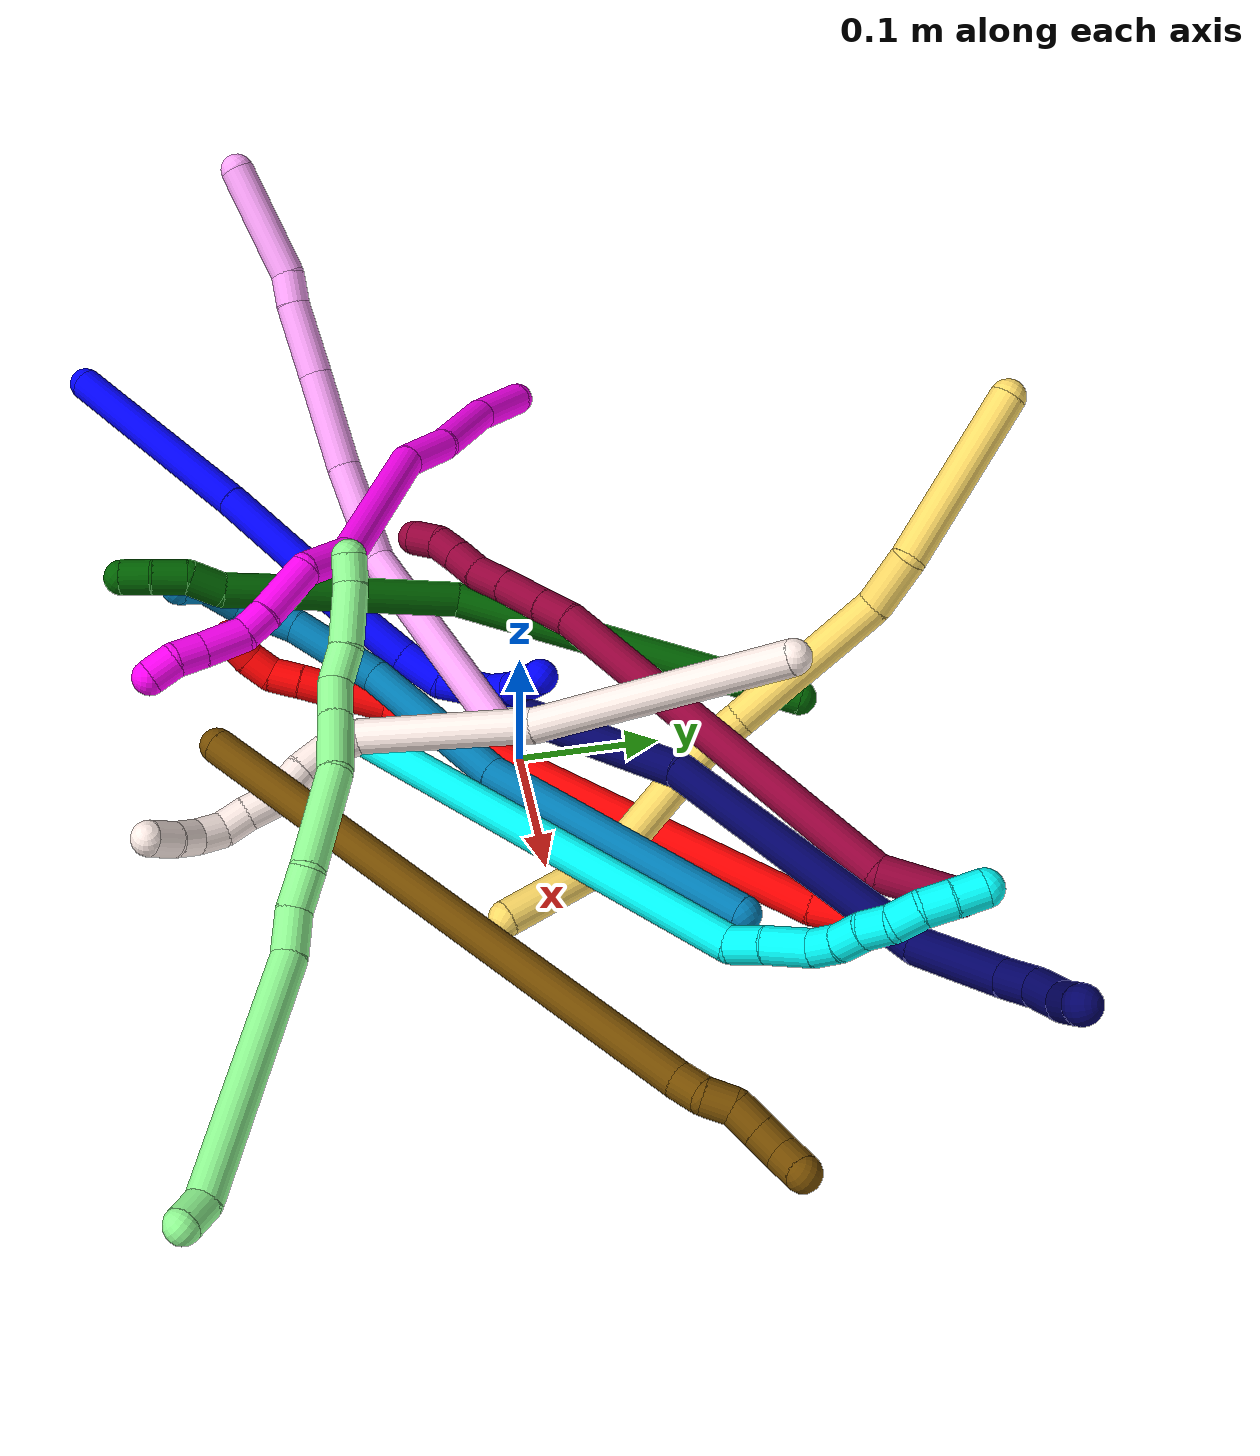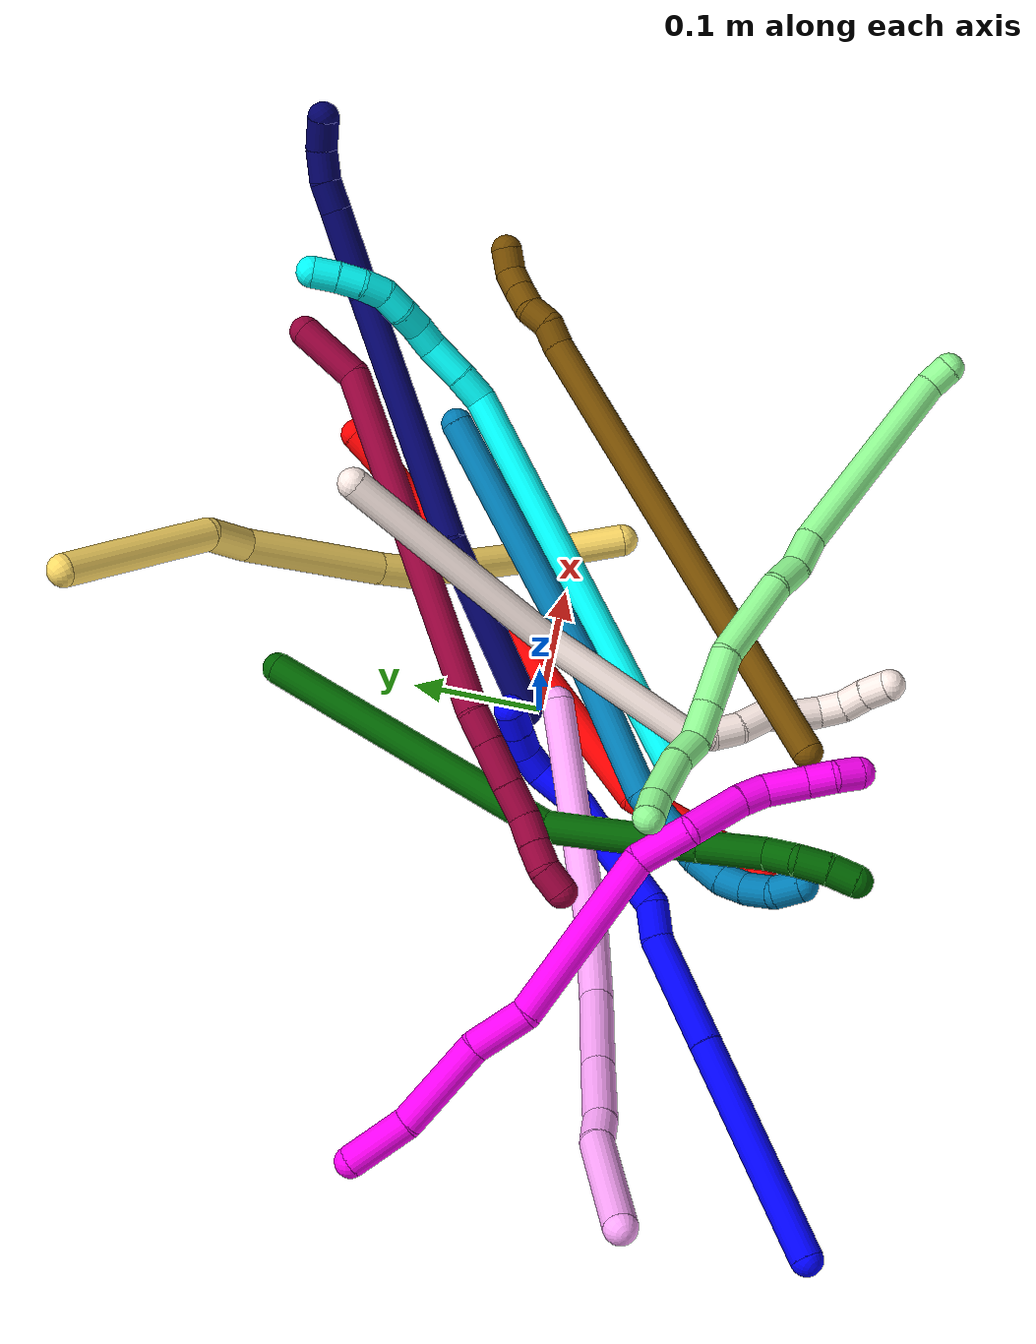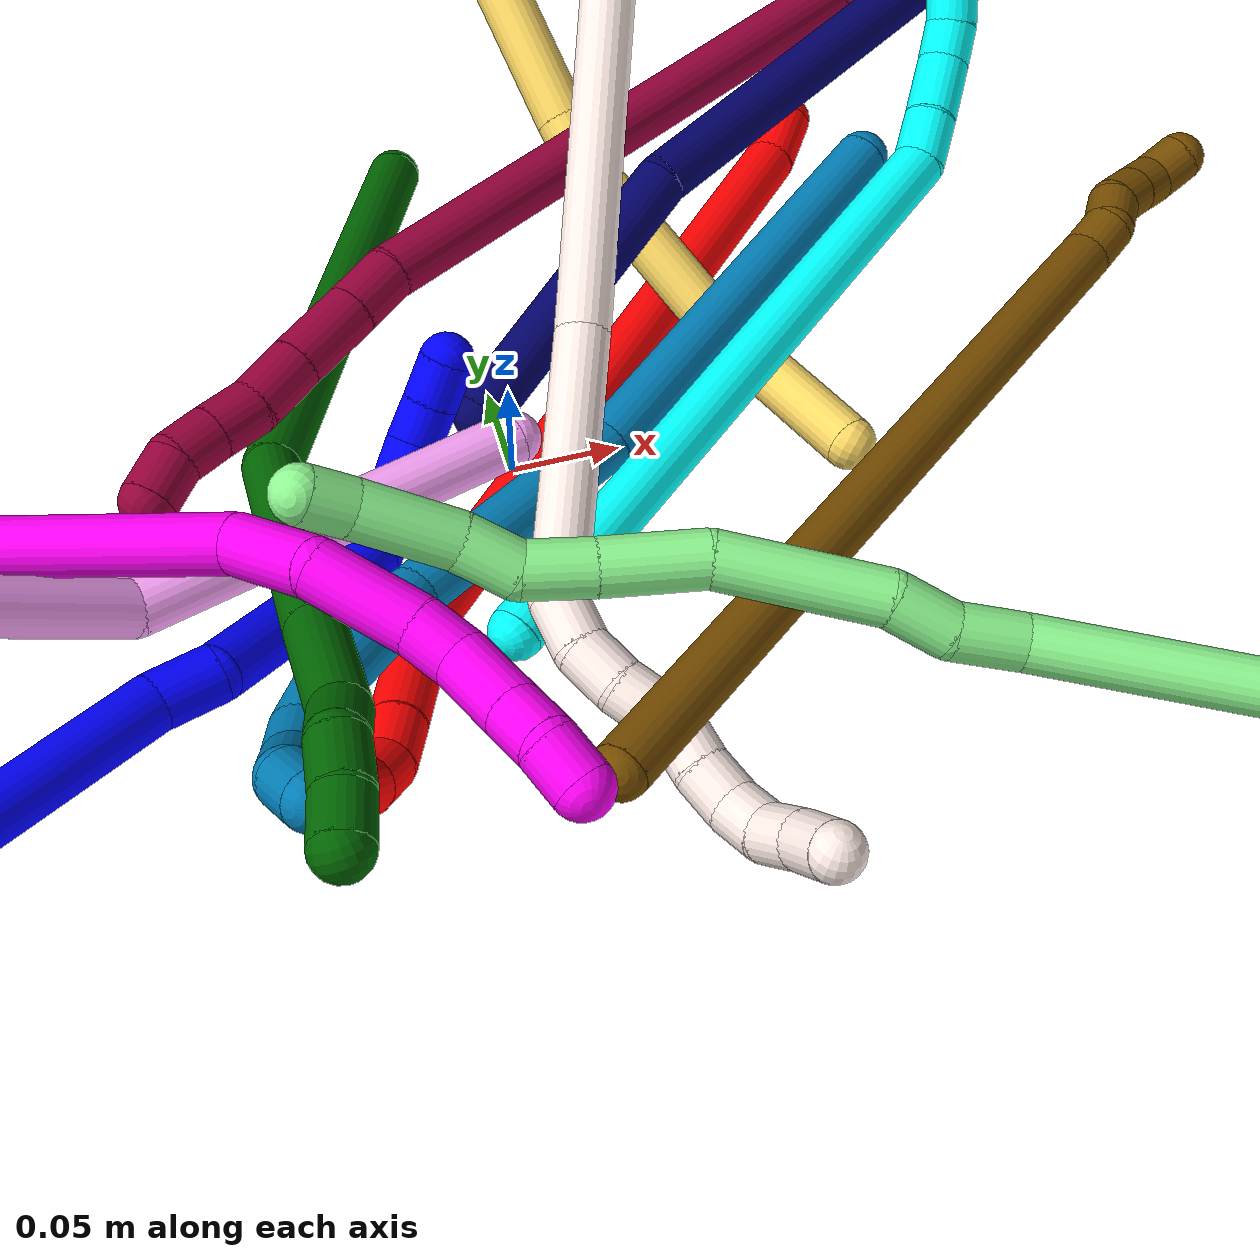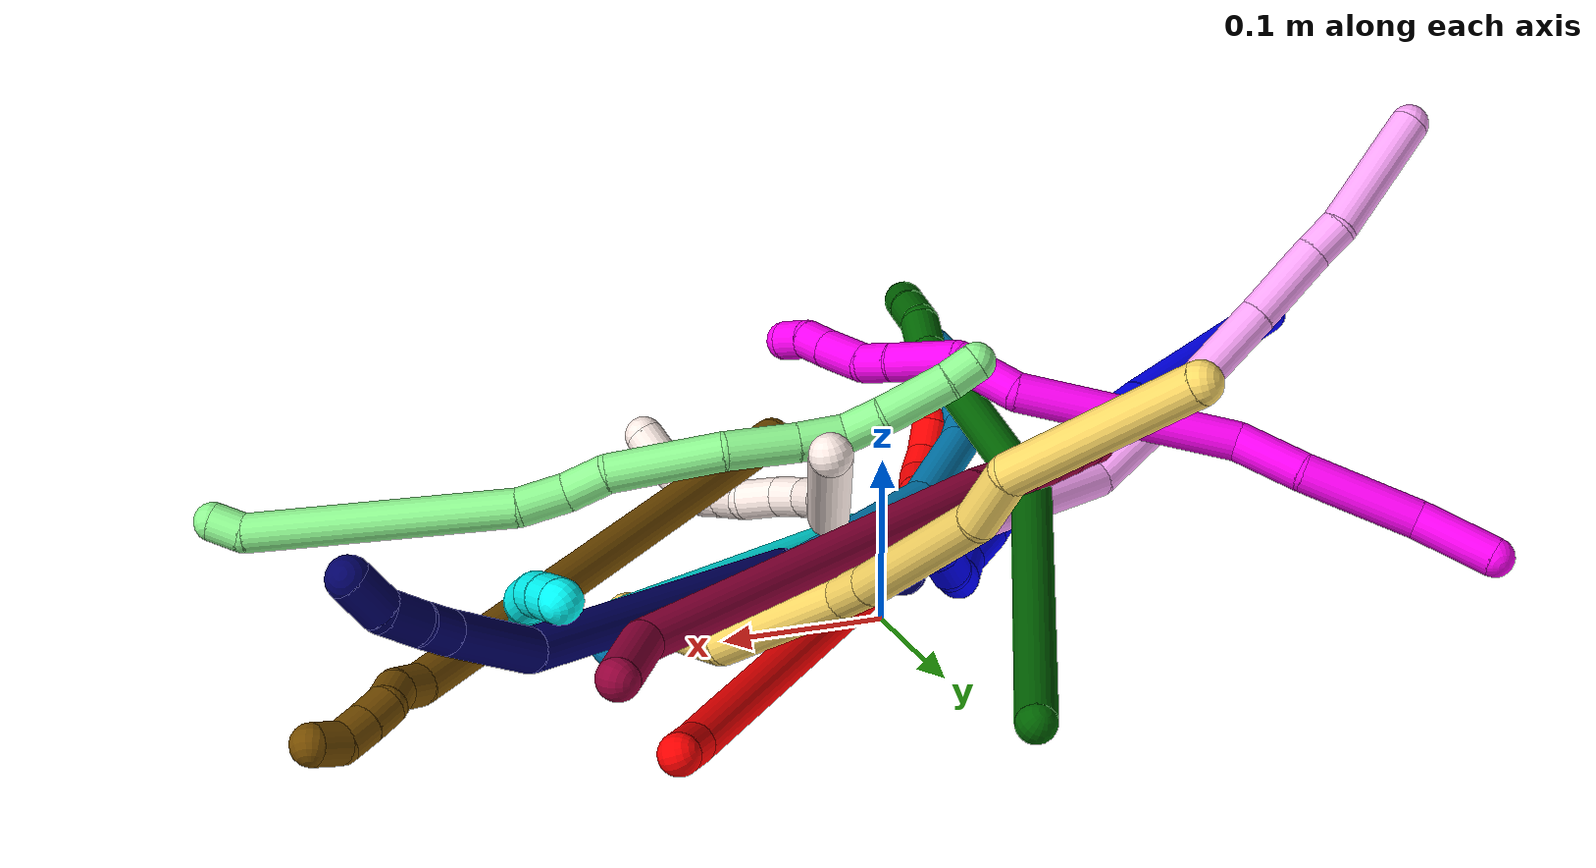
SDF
<sdf version="1.7">
 <world name="default">
  <plugin name="TubeGeneratorPlugin" filename="libtube_generator_plugin.so"/>
  <model name="photoneo_s_sensor">
   <static>1</static>
   <pose>0 0 2 1.57079 1.57079 3.14159</pose>
   <link name="link">
    <inertial><mass>0.1</mass></inertial>
    <sensor name="sensor" type="depth">
     <update_rate>30</update_rate>
     <camera>
      <horizontal_fov>1.22</horizontal_fov>
      <image><width>1920</width><height>1200</height><format>B8G8R8</format></image>
      <clip><near>0.1</near><far>4</far></clip>
      <depth_camera><output>points</output></depth_camera>
     </camera>
     <plugin name="camera_plugin" filename="libgazebo_ros_depth_camera.so">
      <baseline>0.2</baseline>
      <alwaysOn>1</alwaysOn>
      <updateRate>0.0</updateRate>
      <cameraName>camera_ir</cameraName>
      <imageTopicName>/camera/color/image_raw</imageTopicName>
      <cameraInfoTopicName>/camera/color/camera_info</cameraInfoTopicName>
      <depthImageTopicName>/camera/depth/image_raw</depthImageTopicName>
      <depthImageCameraInfoTopicName>/camera/depth/camera_info</depthImageCameraInfoTopicName>
      <pointCloudTopicName>/camera/depth/points</pointCloudTopicName>
      <frameName>fr_optical</frameName>
      <pointCloudCutoff>0.1</pointCloudCutoff>
      <pointCloudCutoffMax>2.0</pointCloudCutoffMax>
      <distortionK1>0</distortionK1>
      <distortionK2>0</distortionK2>
      <distortionK3>0</distortionK3>
      <distortionT1>0</distortionT1>
      <distortionT2>0</distortionT2>
      <CxPrime>0</CxPrime>
      <Cx>0</Cx>
      <Cy>0</Cy>
      <focalLength>0</focalLength>
      <hackBaseline>0</hackBaseline>
     </plugin>
    </sensor>
   </link>
  </model>
  <gravity>0 0 -9.8</gravity>
  <magnetic_field>6e-06 2.3e-05 -4.2e-05</magnetic_field>
  <atmosphere type="adiabatic"/>
  <physics name="default_physics" default="0" type="ode">
   <max_step_size>0.003</max_step_size>
   <real_time_factor>1</real_time_factor>
   <real_time_update_rate>1000</real_time_update_rate>
   <max_contacts>10000</max_contacts>
   <ode>
    <solver>
     <type>quick</type>
     <iters>100</iters>
     <sor>1.3</sor>
     <use_dynamic_moi_rescaling>0</use_dynamic_moi_rescaling>
    </solver>
    <constraints>
     <contact_max_correcting_vel>0</contact_max_correcting_vel>
     <contact_surface_layer>0.001</contact_surface_layer>
     <cfm>0</cfm>
     <erp>0.2</erp>
    </constraints>
   </ode>
  </physics>
  <scene><ambient>0.4 0.4 0.4 1</ambient><background>0.7 0.7 0.7 1</background><shadows>0</shadows></scene>
  <audio><device>default</device></audio>
  <spherical_coordinates>
   <surface_model>EARTH_WGS84</surface_model>
   <latitude_deg>0</latitude_deg>
   <longitude_deg>0</longitude_deg>
   <elevation>0</elevation>
   <heading_deg>0</heading_deg>
  </spherical_coordinates>
  <model name="bin">
   <static>1</static>
   <link name="bottom">
    <collision name="collision-bottom">
     <pose>0 0 -0.01 0 -0 0</pose>
     <geometry><box><size>0.8 0.6 0.02</size></box></geometry>
     <surface>
      <friction><ode><mu>100</mu><mu2>100</mu2></ode></friction>
      <contact><collide_bitmask>65535</collide_bitmask></contact>
     </surface>
    </collision>
   </link>
   <link name="west_wall">
    <collision name="collision-west_wall">
     <pose>-0.41 0 0.1 0 -0 0</pose>
     <geometry><box><size>0.02 0.6 0.2</size></box></geometry>
     <surface>
      <friction><ode><mu>100</mu><mu2>100</mu2></ode></friction>
      <contact><collide_bitmask>65535</collide_bitmask></contact>
     </surface>
    </collision>
   </link>
   <link name="east_wall">
    <collision name="collision-east_wall">
     <pose>0.41 0 0.1 0 -0 0</pose>
     <geometry><box><size>0.02 0.6 0.2</size></box></geometry>
     <surface>
      <friction><ode><mu>100</mu><mu2>100</mu2></ode></friction>
      <contact><collide_bitmask>65535</collide_bitmask></contact>
     </surface>
    </collision>
   </link>
   <link name="south_wall">
    <collision name="collision-south_wall">
     <pose>0 -0.31 0.1 0 -0 0</pose>
     <geometry><box><size>0.8 0.02 0.2</size></box></geometry>
     <surface>
      <friction><ode><mu>100</mu><mu2>100</mu2></ode></friction>
      <contact><collide_bitmask>65535</collide_bitmask></contact>
     </surface>
    </collision>
   </link>
   <link name="north_wall">
    <collision name="collision-north_wall">
     <pose>0 0.31 0.1 0 -0 0</pose>
     <geometry><box><size>0.8 0.02 0.2</size></box></geometry>
     <surface>
      <friction><ode><mu>100</mu><mu2>100</mu2></ode></friction>
      <contact><collide_bitmask>65535</collide_bitmask></contact>
     </surface>
    </collision>
   </link>
  </model>
  <model name="1">
   <static>0</static>
   <link name="1">
    <collision name="collision-cylinder-e_1_1_4">
     <pose>0.034532 0.018659 -0.078277 -2.90759 0.40536 -2.1025</pose>
     <geometry><cylinder><radius>0.0125</radius><length>0.175132</length></cylinder></geometry>
     <surface>
      <friction><ode><mu>1.16</mu><mu2>1.16</mu2><slip1>0</slip1><slip2>0</slip2></ode></friction>
      <contact><ode><kp>1e+06</kp><kd>1</kd><max_vel>0</max_vel><min_depth>0.001</min_depth></ode></contact>
     </surface>
    </collision>
    <visual name="visual-cylinder-e_1_1_4">
     <pose>0.034532 0.018659 -0.078277 -2.90759 0.40536 -2.1025</pose>
     <geometry><cylinder><radius>0.0125</radius><length>0.175132</length></cylinder></geometry>
     <material><ambient>0 0 1 1</ambient></material>
    </visual>
    <collision name="collision-cylinder-e_2_4_5">
     <pose>0.085967 0.044391 -0.197474 -2.97042 0.386568 -2.31536</pose>
     <geometry><cylinder><radius>0.0125</radius><length>0.089672</length></cylinder></geometry>
     <surface>
      <friction><ode><mu>1.16</mu><mu2>1.16</mu2><slip1>0</slip1><slip2>0</slip2></ode></friction>
      <contact><ode><kp>1e+06</kp><kd>1</kd><max_vel>0</max_vel><min_depth>0.001</min_depth></ode></contact>
     </surface>
    </collision>
    <visual name="visual-cylinder-e_2_4_5">
     <pose>0.085967 0.044391 -0.197474 -2.97042 0.386568 -2.31536</pose>
     <geometry><cylinder><radius>0.0125</radius><length>0.089672</length></cylinder></geometry>
     <material><ambient>0 0 1 1</ambient></material>
    </visual>
    <collision name="collision-cylinder-e_3_5_6">
     <pose>0.111627 0.052879 -0.24908 -3.01004 0.682228 -2.77465</pose>
     <geometry><cylinder><radius>0.0125</radius><length>0.027775</length></cylinder></geometry>
     <surface>
      <friction><ode><mu>1.16</mu><mu2>1.16</mu2><slip1>0</slip1><slip2>0</slip2></ode></friction>
      <contact><ode><kp>1e+06</kp><kd>1</kd><max_vel>0</max_vel><min_depth>0.001</min_depth></ode></contact>
     </surface>
    </collision>
    <visual name="visual-cylinder-e_3_5_6">
     <pose>0.111627 0.052879 -0.24908 -3.01004 0.682228 -2.77465</pose>
     <geometry><cylinder><radius>0.0125</radius><length>0.027775</length></cylinder></geometry>
     <material><ambient>0 0 1 1</ambient></material>
    </visual>
    <collision name="collision-cylinder-e_4_6_7">
     <pose>0.126321 0.056686 -0.295964 -3.07558 0.162249 -2.37</pose>
     <geometry><cylinder><radius>0.0125</radius><length>0.073519</length></cylinder></geometry>
     <surface>
      <friction><ode><mu>1.16</mu><mu2>1.16</mu2><slip1>0</slip1><slip2>0</slip2></ode></friction>
      <contact><ode><kp>1e+06</kp><kd>1</kd><max_vel>0</max_vel><min_depth>0.001</min_depth></ode></contact>
     </surface>
    </collision>
    <visual name="visual-cylinder-e_4_6_7">
     <pose>0.126321 0.056686 -0.295964 -3.07558 0.162249 -2.37</pose>
     <geometry><cylinder><radius>0.0125</radius><length>0.073519</length></cylinder></geometry>
     <material><ambient>0 0 1 1</ambient></material>
    </visual>
    <collision name="collision-cylinder-e_5_7_8">
     <pose>0.136342 0.062486 -0.348403 -2.93482 0.241232 -1.72561</pose>
     <geometry><cylinder><radius>0.0125</radius><length>0.03418</length></cylinder></geometry>
     <surface>
      <friction><ode><mu>1.16</mu><mu2>1.16</mu2><slip1>0</slip1><slip2>0</slip2></ode></friction>
      <contact><ode><kp>1e+06</kp><kd>1</kd><max_vel>0</max_vel><min_depth>0.001</min_depth></ode></contact>
     </surface>
    </collision>
    <visual name="visual-cylinder-e_5_7_8">
     <pose>0.136342 0.062486 -0.348403 -2.93482 0.241232 -1.72561</pose>
     <geometry><cylinder><radius>0.0125</radius><length>0.03418</length></cylinder></geometry>
     <material><ambient>0 0 1 1</ambient></material>
    </visual>
    <collision name="collision-cylinder-e_6_8_9">
     <pose>0.140555 0.0756 -0.381037 -2.60695 0.006804 -0.024842</pose>
     <geometry><cylinder><radius>0.0125</radius><length>0.038103</length></cylinder></geometry>
     <surface>
      <friction><ode><mu>1.16</mu><mu2>1.16</mu2><slip1>0</slip1><slip2>0</slip2></ode></friction>
      <contact><ode><kp>1e+06</kp><kd>1</kd><max_vel>0</max_vel><min_depth>0.001</min_depth></ode></contact>
     </surface>
    </collision>
    <visual name="visual-cylinder-e_6_8_9">
     <pose>0.140555 0.0756 -0.381037 -2.60695 0.006804 -0.024842</pose>
     <geometry><cylinder><radius>0.0125</radius><length>0.038103</length></cylinder></geometry>
     <material><ambient>0 0 1 1</ambient></material>
    </visual>
    <collision name="collision-cylinder-e_7_9_10">
     <pose>0.14386 0.093391 -0.403075 -2.18049 0.311564 -0.585239</pose>
     <geometry><cylinder><radius>0.0125</radius><length>0.020716</length></cylinder></geometry>
     <surface>
      <friction><ode><mu>1.16</mu><mu2>1.16</mu2><slip1>0</slip1><slip2>0</slip2></ode></friction>
      <contact><ode><kp>1e+06</kp><kd>1</kd><max_vel>0</max_vel><min_depth>0.001</min_depth></ode></contact>
     </surface>
    </collision>
    <visual name="visual-cylinder-e_7_9_10">
     <pose>0.14386 0.093391 -0.403075 -2.18049 0.311564 -0.585239</pose>
     <geometry><cylinder><radius>0.0125</radius><length>0.020716</length></cylinder></geometry>
     <material><ambient>0 0 1 1</ambient></material>
    </visual>
    <collision name="collision-cylinder-e_8_10_11">
     <pose>0.152276 0.109779 -0.411205 -1.86146 0.543774 -0.71648</pose>
     <geometry><cylinder><radius>0.0125</radius><length>0.020261</length></cylinder></geometry>
     <surface>
      <friction><ode><mu>1.16</mu><mu2>1.16</mu2><slip1>0</slip1><slip2>0</slip2></ode></friction>
      <contact><ode><kp>1e+06</kp><kd>1</kd><max_vel>0</max_vel><min_depth>0.001</min_depth></ode></contact>
     </surface>
    </collision>
    <visual name="visual-cylinder-e_8_10_11">
     <pose>0.152276 0.109779 -0.411205 -1.86146 0.543774 -0.71648</pose>
     <geometry><cylinder><radius>0.0125</radius><length>0.020261</length></cylinder></geometry>
     <material><ambient>0 0 1 1</ambient></material>
    </visual>
    <collision name="collision-cylinder-e_9_11_2">
     <pose>0.162812 0.126681 -0.415835 -1.8153 0.538717 -0.679416</pose>
     <geometry><cylinder><radius>0.0125</radius><length>0.020642</length></cylinder></geometry>
     <surface>
      <friction><ode><mu>1.16</mu><mu2>1.16</mu2><slip1>0</slip1><slip2>0</slip2></ode></friction>
      <contact><ode><kp>1e+06</kp><kd>1</kd><max_vel>0</max_vel><min_depth>0.001</min_depth></ode></contact>
     </surface>
    </collision>
    <visual name="visual-cylinder-e_9_11_2">
     <pose>0.162812 0.126681 -0.415835 -1.8153 0.538717 -0.679416</pose>
     <geometry><cylinder><radius>0.0125</radius><length>0.020642</length></cylinder></geometry>
     <material><ambient>0 0 1 1</ambient></material>
    </visual>
    <collision name="collision-sphere-2">
     <pose>0.168107 0.135276 -0.417979 0 -0 0</pose>
     <geometry><sphere><radius>0.0125</radius></sphere></geometry>
     <surface>
      <friction><ode><mu>1.16</mu><mu2>1.16</mu2><slip1>0</slip1><slip2>0</slip2></ode></friction>
      <contact><ode><kp>1e+06</kp><kd>1</kd><max_vel>0</max_vel><min_depth>0.001</min_depth></ode></contact>
     </surface>
    </collision>
    <visual name="visual-sphere-2">
     <pose>0.168107 0.135276 -0.417979 0 -0 0</pose>
     <geometry><sphere><radius>0.0125</radius></sphere></geometry>
     <material><ambient>0 0 1 1</ambient></material>
    </visual>
    <collision name="collision-sphere-11">
     <pose>0.157517 0.118085 -0.41369 0 -0 0</pose>
     <geometry><sphere><radius>0.0125</radius></sphere></geometry>
     <surface>
      <friction><ode><mu>1.16</mu><mu2>1.16</mu2><slip1>0</slip1><slip2>0</slip2></ode></friction>
      <contact><ode><kp>1e+06</kp><kd>1</kd><max_vel>0</max_vel><min_depth>0.001</min_depth></ode></contact>
     </surface>
    </collision>
    <visual name="visual-sphere-11">
     <pose>0.157517 0.118085 -0.41369 0 -0 0</pose>
     <geometry><sphere><radius>0.0125</radius></sphere></geometry>
     <material><ambient>0 0 1 1</ambient></material>
    </visual>
    <collision name="collision-sphere-10">
     <pose>0.147035 0.101474 -0.408721 0 -0 0</pose>
     <geometry><sphere><radius>0.0125</radius></sphere></geometry>
     <surface>
      <friction><ode><mu>1.16</mu><mu2>1.16</mu2><slip1>0</slip1><slip2>0</slip2></ode></friction>
      <contact><ode><kp>1e+06</kp><kd>1</kd><max_vel>0</max_vel><min_depth>0.001</min_depth></ode></contact>
     </surface>
    </collision>
    <visual name="visual-sphere-10">
     <pose>0.147035 0.101474 -0.408721 0 -0 0</pose>
     <geometry><sphere><radius>0.0125</radius></sphere></geometry>
     <material><ambient>0 0 1 1</ambient></material>
    </visual>
    <collision name="collision-sphere-9">
     <pose>0.140684 0.085308 -0.397429 0 -0 0</pose>
     <geometry><sphere><radius>0.0125</radius></sphere></geometry>
     <surface>
      <friction><ode><mu>1.16</mu><mu2>1.16</mu2><slip1>0</slip1><slip2>0</slip2></ode></friction>
      <contact><ode><kp>1e+06</kp><kd>1</kd><max_vel>0</max_vel><min_depth>0.001</min_depth></ode></contact>
     </surface>
    </collision>
    <visual name="visual-sphere-9">
     <pose>0.140684 0.085308 -0.397429 0 -0 0</pose>
     <geometry><sphere><radius>0.0125</radius></sphere></geometry>
     <material><ambient>0 0 1 1</ambient></material>
    </visual>
    <collision name="collision-sphere-4">
     <pose>0.069063 0.037318 -0.156554 0 -0 0</pose>
     <geometry><sphere><radius>0.0125</radius></sphere></geometry>
     <surface>
      <friction><ode><mu>1.16</mu><mu2>1.16</mu2><slip1>0</slip1><slip2>0</slip2></ode></friction>
      <contact><ode><kp>1e+06</kp><kd>1</kd><max_vel>0</max_vel><min_depth>0.001</min_depth></ode></contact>
     </surface>
    </collision>
    <visual name="visual-sphere-4">
     <pose>0.069063 0.037318 -0.156554 0 -0 0</pose>
     <geometry><sphere><radius>0.0125</radius></sphere></geometry>
     <material><ambient>0 0 1 1</ambient></material>
    </visual>
    <collision name="collision-sphere-1">
     <geometry><sphere><radius>0.0125</radius></sphere></geometry>
     <surface>
      <friction><ode><mu>1.16</mu><mu2>1.16</mu2><slip1>0</slip1><slip2>0</slip2></ode></friction>
      <contact><ode><kp>1e+06</kp><kd>1</kd><max_vel>0</max_vel><min_depth>0.001</min_depth></ode></contact>
     </surface>
    </collision>
    <visual name="visual-sphere-1">
     <geometry><sphere><radius>0.0125</radius></sphere></geometry>
     <material><ambient>0 0 1 1</ambient></material>
    </visual>
    <collision name="collision-sphere-8">
     <pose>0.140425 0.065893 -0.364644 0 -0 0</pose>
     <geometry><sphere><radius>0.0125</radius></sphere></geometry>
     <surface>
      <friction><ode><mu>1.16</mu><mu2>1.16</mu2><slip1>0</slip1><slip2>0</slip2></ode></friction>
      <contact><ode><kp>1e+06</kp><kd>1</kd><max_vel>0</max_vel><min_depth>0.001</min_depth></ode></contact>
     </surface>
    </collision>
    <visual name="visual-sphere-8">
     <pose>0.140425 0.065893 -0.364644 0 -0 0</pose>
     <geometry><sphere><radius>0.0125</radius></sphere></geometry>
     <material><ambient>0 0 1 1</ambient></material>
    </visual>
    <collision name="collision-sphere-5">
     <pose>0.102871 0.051465 -0.238394 0 -0 0</pose>
     <geometry><sphere><radius>0.0125</radius></sphere></geometry>
     <surface>
      <friction><ode><mu>1.16</mu><mu2>1.16</mu2><slip1>0</slip1><slip2>0</slip2></ode></friction>
      <contact><ode><kp>1e+06</kp><kd>1</kd><max_vel>0</max_vel><min_depth>0.001</min_depth></ode></contact>
     </surface>
    </collision>
    <visual name="visual-sphere-5">
     <pose>0.102871 0.051465 -0.238394 0 -0 0</pose>
     <geometry><sphere><radius>0.0125</radius></sphere></geometry>
     <material><ambient>0 0 1 1</ambient></material>
    </visual>
    <collision name="collision-sphere-6">
     <pose>0.120383 0.054293 -0.259766 0 -0 0</pose>
     <geometry><sphere><radius>0.0125</radius></sphere></geometry>
     <surface>
      <friction><ode><mu>1.16</mu><mu2>1.16</mu2><slip1>0</slip1><slip2>0</slip2></ode></friction>
      <contact><ode><kp>1e+06</kp><kd>1</kd><max_vel>0</max_vel><min_depth>0.001</min_depth></ode></contact>
     </surface>
    </collision>
    <visual name="visual-sphere-6">
     <pose>0.120383 0.054293 -0.259766 0 -0 0</pose>
     <geometry><sphere><radius>0.0125</radius></sphere></geometry>
     <material><ambient>0 0 1 1</ambient></material>
    </visual>
    <collision name="collision-sphere-7">
     <pose>0.132259 0.059079 -0.332161 0 -0 0</pose>
     <geometry><sphere><radius>0.0125</radius></sphere></geometry>
     <surface>
      <friction><ode><mu>1.16</mu><mu2>1.16</mu2><slip1>0</slip1><slip2>0</slip2></ode></friction>
      <contact><ode><kp>1e+06</kp><kd>1</kd><max_vel>0</max_vel><min_depth>0.001</min_depth></ode></contact>
     </surface>
    </collision>
    <visual name="visual-sphere-7">
     <pose>0.132259 0.059079 -0.332161 0 -0 0</pose>
     <geometry><sphere><radius>0.0125</radius></sphere></geometry>
     <material><ambient>0 0 1 1</ambient></material>
    </visual>
    <inertial>
     <pose>0.091172 0.04935 -0.223572 0 -0 0</pose>
     <mass>0.5</mass>
     <inertia>
      <ixx>-0.000693</ixx>
      <ixy>0</ixy>
      <ixz>0</ixz>
      <iyy>-9.6e-05</iyy>
      <iyz>0</iyz>
      <izz>-0.000364</izz>
     </inertia>
    </inertial>
   </link>
   <pose>-0.388502 -0.276774 0.06834 1.08687 -0.358019 -0.490263</pose>
  </model>
  <model name="2">
   <static>0</static>
   <link name="2">
    <collision name="collision-cylinder-e_1_1_4">
     <pose>-0.010624 -0.009458 -0.002747 1.85344 -0.823252 -1.05325</pose>
     <geometry><cylinder><radius>0.0125</radius><length>0.028975</length></cylinder></geometry>
     <surface>
      <friction><ode><mu>1.16</mu><mu2>1.16</mu2><slip1>0</slip1><slip2>0</slip2></ode></friction>
      <contact><ode><kp>1e+06</kp><kd>1</kd><max_vel>0</max_vel><min_depth>0.001</min_depth></ode></contact>
     </surface>
    </collision>
    <visual name="visual-cylinder-e_1_1_4">
     <pose>-0.010624 -0.009458 -0.002747 1.85344 -0.823252 -1.05325</pose>
     <geometry><cylinder><radius>0.0125</radius><length>0.028975</length></cylinder></geometry>
     <material><ambient>1 0 0 1</ambient></material>
    </visual>
    <collision name="collision-cylinder-e_2_4_5">
     <pose>-0.133923 -0.147857 -0.003504 1.55537 -0.718117 -0.708025</pose>
     <geometry><cylinder><radius>0.0125</radius><length>0.342491</length></cylinder></geometry>
     <surface>
      <friction><ode><mu>1.16</mu><mu2>1.16</mu2><slip1>0</slip1><slip2>0</slip2></ode></friction>
      <contact><ode><kp>1e+06</kp><kd>1</kd><max_vel>0</max_vel><min_depth>0.001</min_depth></ode></contact>
     </surface>
    </collision>
    <visual name="visual-cylinder-e_2_4_5">
     <pose>-0.133923 -0.147857 -0.003504 1.55537 -0.718117 -0.708025</pose>
     <geometry><cylinder><radius>0.0125</radius><length>0.342491</length></cylinder></geometry>
     <material><ambient>1 0 0 1</ambient></material>
    </visual>
    <collision name="collision-cylinder-e_3_5_6">
     <pose>-0.259442 -0.305673 -0.009919 1.854 -0.403682 -0.532397</pose>
     <geometry><cylinder><radius>0.0125</radius><length>0.065405</length></cylinder></geometry>
     <surface>
      <friction><ode><mu>1.16</mu><mu2>1.16</mu2><slip1>0</slip1><slip2>0</slip2></ode></friction>
      <contact><ode><kp>1e+06</kp><kd>1</kd><max_vel>0</max_vel><min_depth>0.001</min_depth></ode></contact>
     </surface>
    </collision>
    <visual name="visual-cylinder-e_3_5_6">
     <pose>-0.259442 -0.305673 -0.009919 1.854 -0.403682 -0.532397</pose>
     <geometry><cylinder><radius>0.0125</radius><length>0.065405</length></cylinder></geometry>
     <material><ambient>1 0 0 1</ambient></material>
    </visual>
    <collision name="collision-cylinder-e_4_6_7">
     <pose>-0.277249 -0.343946 -0.021198 1.86776 -0.467464 -0.62274</pose>
     <geometry><cylinder><radius>0.0125</radius><length>0.022016</length></cylinder></geometry>
     <surface>
      <friction><ode><mu>1.16</mu><mu2>1.16</mu2><slip1>0</slip1><slip2>0</slip2></ode></friction>
      <contact><ode><kp>1e+06</kp><kd>1</kd><max_vel>0</max_vel><min_depth>0.001</min_depth></ode></contact>
     </surface>
    </collision>
    <visual name="visual-cylinder-e_4_6_7">
     <pose>-0.277249 -0.343946 -0.021198 1.86776 -0.467464 -0.62274</pose>
     <geometry><cylinder><radius>0.0125</radius><length>0.022016</length></cylinder></geometry>
     <material><ambient>1 0 0 1</ambient></material>
    </visual>
    <collision name="collision-cylinder-e_5_7_8">
     <pose>-0.2847 -0.36303 -0.023319 1.49301 -0.250927 -0.232306</pose>
     <geometry><cylinder><radius>0.0125</radius><length>0.02006</length></cylinder></geometry>
     <surface>
      <friction><ode><mu>1.16</mu><mu2>1.16</mu2><slip1>0</slip1><slip2>0</slip2></ode></friction>
      <contact><ode><kp>1e+06</kp><kd>1</kd><max_vel>0</max_vel><min_depth>0.001</min_depth></ode></contact>
     </surface>
    </collision>
    <visual name="visual-cylinder-e_5_7_8">
     <pose>-0.2847 -0.36303 -0.023319 1.49301 -0.250927 -0.232306</pose>
     <geometry><cylinder><radius>0.0125</radius><length>0.02006</length></cylinder></geometry>
     <material><ambient>1 0 0 1</ambient></material>
    </visual>
    <collision name="collision-cylinder-e_6_8_2">
     <pose>-0.286338 -0.382995 -0.02046 1.36887 0.081089 0.066183</pose>
     <geometry><cylinder><radius>0.0125</radius><length>0.021053</length></cylinder></geometry>
     <surface>
      <friction><ode><mu>1.16</mu><mu2>1.16</mu2><slip1>0</slip1><slip2>0</slip2></ode></friction>
      <contact><ode><kp>1e+06</kp><kd>1</kd><max_vel>0</max_vel><min_depth>0.001</min_depth></ode></contact>
     </surface>
    </collision>
    <visual name="visual-cylinder-e_6_8_2">
     <pose>-0.286338 -0.382995 -0.02046 1.36887 0.081089 0.066183</pose>
     <geometry><cylinder><radius>0.0125</radius><length>0.021053</length></cylinder></geometry>
     <material><ambient>1 0 0 1</ambient></material>
    </visual>
    <collision name="collision-sphere-2">
     <pose>-0.285485 -0.393274 -0.018355 0 -0 0</pose>
     <geometry><sphere><radius>0.0125</radius></sphere></geometry>
     <surface>
      <friction><ode><mu>1.16</mu><mu2>1.16</mu2><slip1>0</slip1><slip2>0</slip2></ode></friction>
      <contact><ode><kp>1e+06</kp><kd>1</kd><max_vel>0</max_vel><min_depth>0.001</min_depth></ode></contact>
     </surface>
    </collision>
    <visual name="visual-sphere-2">
     <pose>-0.285485 -0.393274 -0.018355 0 -0 0</pose>
     <geometry><sphere><radius>0.0125</radius></sphere></geometry>
     <material><ambient>1 0 0 1</ambient></material>
    </visual>
    <collision name="collision-sphere-4">
     <pose>-0.021249 -0.018917 -0.005494 0 -0 0</pose>
     <geometry><sphere><radius>0.0125</radius></sphere></geometry>
     <surface>
      <friction><ode><mu>1.16</mu><mu2>1.16</mu2><slip1>0</slip1><slip2>0</slip2></ode></friction>
      <contact><ode><kp>1e+06</kp><kd>1</kd><max_vel>0</max_vel><min_depth>0.001</min_depth></ode></contact>
     </surface>
    </collision>
    <visual name="visual-sphere-4">
     <pose>-0.021249 -0.018917 -0.005494 0 -0 0</pose>
     <geometry><sphere><radius>0.0125</radius></sphere></geometry>
     <material><ambient>1 0 0 1</ambient></material>
    </visual>
    <collision name="collision-sphere-1">
     <geometry><sphere><radius>0.0125</radius></sphere></geometry>
     <surface>
      <friction><ode><mu>1.16</mu><mu2>1.16</mu2><slip1>0</slip1><slip2>0</slip2></ode></friction>
      <contact><ode><kp>1e+06</kp><kd>1</kd><max_vel>0</max_vel><min_depth>0.001</min_depth></ode></contact>
     </surface>
    </collision>
    <visual name="visual-sphere-1">
     <geometry><sphere><radius>0.0125</radius></sphere></geometry>
     <material><ambient>1 0 0 1</ambient></material>
    </visual>
    <collision name="collision-sphere-8">
     <pose>-0.28719 -0.372716 -0.022564 0 -0 0</pose>
     <geometry><sphere><radius>0.0125</radius></sphere></geometry>
     <surface>
      <friction><ode><mu>1.16</mu><mu2>1.16</mu2><slip1>0</slip1><slip2>0</slip2></ode></friction>
      <contact><ode><kp>1e+06</kp><kd>1</kd><max_vel>0</max_vel><min_depth>0.001</min_depth></ode></contact>
     </surface>
    </collision>
    <visual name="visual-sphere-8">
     <pose>-0.28719 -0.372716 -0.022564 0 -0 0</pose>
     <geometry><sphere><radius>0.0125</radius></sphere></geometry>
     <material><ambient>1 0 0 1</ambient></material>
    </visual>
    <collision name="collision-sphere-5">
     <pose>-0.246597 -0.276797 -0.001515 0 -0 0</pose>
     <geometry><sphere><radius>0.0125</radius></sphere></geometry>
     <surface>
      <friction><ode><mu>1.16</mu><mu2>1.16</mu2><slip1>0</slip1><slip2>0</slip2></ode></friction>
      <contact><ode><kp>1e+06</kp><kd>1</kd><max_vel>0</max_vel><min_depth>0.001</min_depth></ode></contact>
     </surface>
    </collision>
    <visual name="visual-sphere-5">
     <pose>-0.246597 -0.276797 -0.001515 0 -0 0</pose>
     <geometry><sphere><radius>0.0125</radius></sphere></geometry>
     <material><ambient>1 0 0 1</ambient></material>
    </visual>
    <collision name="collision-sphere-6">
     <pose>-0.272288 -0.334549 -0.018323 0 -0 0</pose>
     <geometry><sphere><radius>0.0125</radius></sphere></geometry>
     <surface>
      <friction><ode><mu>1.16</mu><mu2>1.16</mu2><slip1>0</slip1><slip2>0</slip2></ode></friction>
      <contact><ode><kp>1e+06</kp><kd>1</kd><max_vel>0</max_vel><min_depth>0.001</min_depth></ode></contact>
     </surface>
    </collision>
    <visual name="visual-sphere-6">
     <pose>-0.272288 -0.334549 -0.018323 0 -0 0</pose>
     <geometry><sphere><radius>0.0125</radius></sphere></geometry>
     <material><ambient>1 0 0 1</ambient></material>
    </visual>
    <collision name="collision-sphere-7">
     <pose>-0.282209 -0.353343 -0.024074 0 -0 0</pose>
     <geometry><sphere><radius>0.0125</radius></sphere></geometry>
     <surface>
      <friction><ode><mu>1.16</mu><mu2>1.16</mu2><slip1>0</slip1><slip2>0</slip2></ode></friction>
      <contact><ode><kp>1e+06</kp><kd>1</kd><max_vel>0</max_vel><min_depth>0.001</min_depth></ode></contact>
     </surface>
    </collision>
    <visual name="visual-sphere-7">
     <pose>-0.282209 -0.353343 -0.024074 0 -0 0</pose>
     <geometry><sphere><radius>0.0125</radius></sphere></geometry>
     <material><ambient>1 0 0 1</ambient></material>
    </visual>
    <inertial>
     <pose>-0.161975 -0.187649 -0.006588 0 -0 0</pose>
     <mass>0.5</mass>
     <inertia>
      <ixx>0.000265</ixx>
      <ixy>0</ixy>
      <ixz>0</ixz>
      <iyy>-0.000214</iyy>
      <iyz>0</iyz>
      <izz>0.004784</izz>
     </inertia>
    </inertial>
   </link>
   <pose>0.191408 0.189734 0.016993 -1.0119 -0.775123 0.424746</pose>
  </model>
  <model name="3">
   <static>0</static>
   <link name="3">
    <collision name="collision-cylinder-e_1_1_4">
     <pose>0.042819 0.017801 0.154561 -0.114666 0.268569 -0.015508</pose>
     <geometry><cylinder><radius>0.0125</radius><length>0.322735</length></cylinder></geometry>
     <surface>
      <friction><ode><mu>1.16</mu><mu2>1.16</mu2><slip1>0</slip1><slip2>0</slip2></ode></friction>
      <contact><ode><kp>1e+06</kp><kd>1</kd><max_vel>0</max_vel><min_depth>0.001</min_depth></ode></contact>
     </surface>
    </collision>
    <visual name="visual-cylinder-e_1_1_4">
     <pose>0.042819 0.017801 0.154561 -0.114666 0.268569 -0.015508</pose>
     <geometry><cylinder><radius>0.0125</radius><length>0.322735</length></cylinder></geometry>
     <material><ambient>0.003922 1 0.996078 1</ambient></material>
    </visual>
    <collision name="collision-cylinder-e_2_4_5">
     <pose>0.093722 0.03553 0.318555 0.007679 0.708533 0.00284</pose>
     <geometry><cylinder><radius>0.0125</radius><length>0.024847</length></cylinder></geometry>
     <surface>
      <friction><ode><mu>1.16</mu><mu2>1.16</mu2><slip1>0</slip1><slip2>0</slip2></ode></friction>
      <contact><ode><kp>1e+06</kp><kd>1</kd><max_vel>0</max_vel><min_depth>0.001</min_depth></ode></contact>
     </surface>
    </collision>
    <visual name="visual-cylinder-e_2_4_5">
     <pose>0.093722 0.03553 0.318555 0.007679 0.708533 0.00284</pose>
     <geometry><cylinder><radius>0.0125</radius><length>0.024847</length></cylinder></geometry>
     <material><ambient>0.003922 1 0.996078 1</ambient></material>
    </visual>
    <collision name="collision-cylinder-e_3_5_6">
     <pose>0.111303 0.03403 0.340943 0.109689 0.629655 0.035753</pose>
     <geometry><cylinder><radius>0.0125</radius><length>0.032253</length></cylinder></geometry>
     <surface>
      <friction><ode><mu>1.16</mu><mu2>1.16</mu2><slip1>0</slip1><slip2>0</slip2></ode></friction>
      <contact><ode><kp>1e+06</kp><kd>1</kd><max_vel>0</max_vel><min_depth>0.001</min_depth></ode></contact>
     </surface>
    </collision>
    <visual name="visual-cylinder-e_3_5_6">
     <pose>0.111303 0.03403 0.340943 0.109689 0.629655 0.035753</pose>
     <geometry><cylinder><radius>0.0125</radius><length>0.032253</length></cylinder></geometry>
     <material><ambient>0.003922 1 0.996078 1</ambient></material>
    </visual>
    <collision name="collision-cylinder-e_4_6_7">
     <pose>0.128672 0.033654 0.359982 -0.170922 0.905812 -0.083333</pose>
     <geometry><cylinder><radius>0.0125</radius><length>0.020009</length></cylinder></geometry>
     <surface>
      <friction><ode><mu>1.16</mu><mu2>1.16</mu2><slip1>0</slip1><slip2>0</slip2></ode></friction>
      <contact><ode><kp>1e+06</kp><kd>1</kd><max_vel>0</max_vel><min_depth>0.001</min_depth></ode></contact>
     </surface>
    </collision>
    <visual name="visual-cylinder-e_4_6_7">
     <pose>0.128672 0.033654 0.359982 -0.170922 0.905812 -0.083333</pose>
     <geometry><cylinder><radius>0.0125</radius><length>0.020009</length></cylinder></geometry>
     <material><ambient>0.003922 1 0.996078 1</ambient></material>
    </visual>
    <collision name="collision-cylinder-e_5_7_8">
     <pose>0.145648 0.035314 0.370292 -0.143463 1.13213 -0.091254</pose>
     <geometry><cylinder><radius>0.0125</radius><length>0.020112</length></cylinder></geometry>
     <surface>
      <friction><ode><mu>1.16</mu><mu2>1.16</mu2><slip1>0</slip1><slip2>0</slip2></ode></friction>
      <contact><ode><kp>1e+06</kp><kd>1</kd><max_vel>0</max_vel><min_depth>0.001</min_depth></ode></contact>
     </surface>
    </collision>
    <visual name="visual-cylinder-e_5_7_8">
     <pose>0.145648 0.035314 0.370292 -0.143463 1.13213 -0.091254</pose>
     <geometry><cylinder><radius>0.0125</radius><length>0.020112</length></cylinder></geometry>
     <material><ambient>0.003922 1 0.996078 1</ambient></material>
    </visual>
    <collision name="collision-cylinder-e_6_8_9">
     <pose>0.162804 0.035841 0.380487 0.014005 0.932909 0.007052</pose>
     <geometry><cylinder><radius>0.0125</radius><length>0.020044</length></cylinder></geometry>
     <surface>
      <friction><ode><mu>1.16</mu><mu2>1.16</mu2><slip1>0</slip1><slip2>0</slip2></ode></friction>
      <contact><ode><kp>1e+06</kp><kd>1</kd><max_vel>0</max_vel><min_depth>0.001</min_depth></ode></contact>
     </surface>
    </collision>
    <visual name="visual-cylinder-e_6_8_9">
     <pose>0.162804 0.035841 0.380487 0.014005 0.932909 0.007052</pose>
     <geometry><cylinder><radius>0.0125</radius><length>0.020044</length></cylinder></geometry>
     <material><ambient>0.003922 1 0.996078 1</ambient></material>
    </visual>
    <collision name="collision-cylinder-e_7_9_10">
     <pose>0.179371 0.03253 0.390585 0.663403 1.01903 0.38023</pose>
     <geometry><cylinder><radius>0.0125</radius><length>0.020001</length></cylinder></geometry>
     <surface>
      <friction><ode><mu>1.16</mu><mu2>1.16</mu2><slip1>0</slip1><slip2>0</slip2></ode></friction>
      <contact><ode><kp>1e+06</kp><kd>1</kd><max_vel>0</max_vel><min_depth>0.001</min_depth></ode></contact>
     </surface>
    </collision>
    <visual name="visual-cylinder-e_7_9_10">
     <pose>0.179371 0.03253 0.390585 0.663403 1.01903 0.38023</pose>
     <geometry><cylinder><radius>0.0125</radius><length>0.020001</length></cylinder></geometry>
     <material><ambient>0.003922 1 0.996078 1</ambient></material>
    </visual>
    <collision name="collision-cylinder-e_8_10_11">
     <pose>0.194817 0.024317 0.399924 0.763436 0.765593 0.320488</pose>
     <geometry><cylinder><radius>0.0125</radius><length>0.02</length></cylinder></geometry>
     <surface>
      <friction><ode><mu>1.16</mu><mu2>1.16</mu2><slip1>0</slip1><slip2>0</slip2></ode></friction>
      <contact><ode><kp>1e+06</kp><kd>1</kd><max_vel>0</max_vel><min_depth>0.001</min_depth></ode></contact>
     </surface>
    </collision>
    <visual name="visual-cylinder-e_8_10_11">
     <pose>0.194817 0.024317 0.399924 0.763436 0.765593 0.320488</pose>
     <geometry><cylinder><radius>0.0125</radius><length>0.02</length></cylinder></geometry>
     <material><ambient>0.003922 1 0.996078 1</ambient></material>
    </visual>
    <collision name="collision-cylinder-e_9_11_2">
     <pose>0.208248 0.013459 0.409954 0.883448 0.707675 0.345865</pose>
     <geometry><cylinder><radius>0.0125</radius><length>0.02</length></cylinder></geometry>
     <surface>
      <friction><ode><mu>1.16</mu><mu2>1.16</mu2><slip1>0</slip1><slip2>0</slip2></ode></friction>
      <contact><ode><kp>1e+06</kp><kd>1</kd><max_vel>0</max_vel><min_depth>0.001</min_depth></ode></contact>
     </surface>
    </collision>
    <visual name="visual-cylinder-e_9_11_2">
     <pose>0.208248 0.013459 0.409954 0.883448 0.707675 0.345865</pose>
     <geometry><cylinder><radius>0.0125</radius><length>0.02</length></cylinder></geometry>
     <material><ambient>0.003922 1 0.996078 1</ambient></material>
    </visual>
    <collision name="collision-sphere-2">
     <pose>0.214748 0.007585 0.414775 0 -0 0</pose>
     <geometry><sphere><radius>0.0125</radius></sphere></geometry>
     <surface>
      <friction><ode><mu>1.16</mu><mu2>1.16</mu2><slip1>0</slip1><slip2>0</slip2></ode></friction>
      <contact><ode><kp>1e+06</kp><kd>1</kd><max_vel>0</max_vel><min_depth>0.001</min_depth></ode></contact>
     </surface>
    </collision>
    <visual name="visual-sphere-2">
     <pose>0.214748 0.007585 0.414775 0 -0 0</pose>
     <geometry><sphere><radius>0.0125</radius></sphere></geometry>
     <material><ambient>0.003922 1 0.996078 1</ambient></material>
    </visual>
    <collision name="collision-sphere-11">
     <pose>0.201747 0.019332 0.405133 0 -0 0</pose>
     <geometry><sphere><radius>0.0125</radius></sphere></geometry>
     <surface>
      <friction><ode><mu>1.16</mu><mu2>1.16</mu2><slip1>0</slip1><slip2>0</slip2></ode></friction>
      <contact><ode><kp>1e+06</kp><kd>1</kd><max_vel>0</max_vel><min_depth>0.001</min_depth></ode></contact>
     </surface>
    </collision>
    <visual name="visual-sphere-11">
     <pose>0.201747 0.019332 0.405133 0 -0 0</pose>
     <geometry><sphere><radius>0.0125</radius></sphere></geometry>
     <material><ambient>0.003922 1 0.996078 1</ambient></material>
    </visual>
    <collision name="collision-sphere-10">
     <pose>0.187888 0.029302 0.394715 0 -0 0</pose>
     <geometry><sphere><radius>0.0125</radius></sphere></geometry>
     <surface>
      <friction><ode><mu>1.16</mu><mu2>1.16</mu2><slip1>0</slip1><slip2>0</slip2></ode></friction>
      <contact><ode><kp>1e+06</kp><kd>1</kd><max_vel>0</max_vel><min_depth>0.001</min_depth></ode></contact>
     </surface>
    </collision>
    <visual name="visual-sphere-10">
     <pose>0.187888 0.029302 0.394715 0 -0 0</pose>
     <geometry><sphere><radius>0.0125</radius></sphere></geometry>
     <material><ambient>0.003922 1 0.996078 1</ambient></material>
    </visual>
    <collision name="collision-sphere-9">
     <pose>0.170855 0.035758 0.386455 0 -0 0</pose>
     <geometry><sphere><radius>0.0125</radius></sphere></geometry>
     <surface>
      <friction><ode><mu>1.16</mu><mu2>1.16</mu2><slip1>0</slip1><slip2>0</slip2></ode></friction>
      <contact><ode><kp>1e+06</kp><kd>1</kd><max_vel>0</max_vel><min_depth>0.001</min_depth></ode></contact>
     </surface>
    </collision>
    <visual name="visual-sphere-9">
     <pose>0.170855 0.035758 0.386455 0 -0 0</pose>
     <geometry><sphere><radius>0.0125</radius></sphere></geometry>
     <material><ambient>0.003922 1 0.996078 1</ambient></material>
    </visual>
    <collision name="collision-sphere-4">
     <pose>0.085638 0.035602 0.309122 0 -0 0</pose>
     <geometry><sphere><radius>0.0125</radius></sphere></geometry>
     <surface>
      <friction><ode><mu>1.16</mu><mu2>1.16</mu2><slip1>0</slip1><slip2>0</slip2></ode></friction>
      <contact><ode><kp>1e+06</kp><kd>1</kd><max_vel>0</max_vel><min_depth>0.001</min_depth></ode></contact>
     </surface>
    </collision>
    <visual name="visual-sphere-4">
     <pose>0.085638 0.035602 0.309122 0 -0 0</pose>
     <geometry><sphere><radius>0.0125</radius></sphere></geometry>
     <material><ambient>0.003922 1 0.996078 1</ambient></material>
    </visual>
    <collision name="collision-sphere-1">
     <geometry><sphere><radius>0.0125</radius></sphere></geometry>
     <surface>
      <friction><ode><mu>1.16</mu><mu2>1.16</mu2><slip1>0</slip1><slip2>0</slip2></ode></friction>
      <contact><ode><kp>1e+06</kp><kd>1</kd><max_vel>0</max_vel><min_depth>0.001</min_depth></ode></contact>
     </surface>
    </collision>
    <visual name="visual-sphere-1">
     <geometry><sphere><radius>0.0125</radius></sphere></geometry>
     <material><ambient>0.003922 1 0.996078 1</ambient></material>
    </visual>
    <collision name="collision-sphere-8">
     <pose>0.154753 0.035925 0.37452 0 -0 0</pose>
     <geometry><sphere><radius>0.0125</radius></sphere></geometry>
     <surface>
      <friction><ode><mu>1.16</mu><mu2>1.16</mu2><slip1>0</slip1><slip2>0</slip2></ode></friction>
      <contact><ode><kp>1e+06</kp><kd>1</kd><max_vel>0</max_vel><min_depth>0.001</min_depth></ode></contact>
     </surface>
    </collision>
    <visual name="visual-sphere-8">
     <pose>0.154753 0.035925 0.37452 0 -0 0</pose>
     <geometry><sphere><radius>0.0125</radius></sphere></geometry>
     <material><ambient>0.003922 1 0.996078 1</ambient></material>
    </visual>
    <collision name="collision-sphere-5">
     <pose>0.101806 0.035457 0.327987 0 -0 0</pose>
     <geometry><sphere><radius>0.0125</radius></sphere></geometry>
     <surface>
      <friction><ode><mu>1.16</mu><mu2>1.16</mu2><slip1>0</slip1><slip2>0</slip2></ode></friction>
      <contact><ode><kp>1e+06</kp><kd>1</kd><max_vel>0</max_vel><min_depth>0.001</min_depth></ode></contact>
     </surface>
    </collision>
    <visual name="visual-sphere-5">
     <pose>0.101806 0.035457 0.327987 0 -0 0</pose>
     <geometry><sphere><radius>0.0125</radius></sphere></geometry>
     <material><ambient>0.003922 1 0.996078 1</ambient></material>
    </visual>
    <collision name="collision-sphere-6">
     <pose>0.120799 0.032604 0.353899 0 -0 0</pose>
     <geometry><sphere><radius>0.0125</radius></sphere></geometry>
     <surface>
      <friction><ode><mu>1.16</mu><mu2>1.16</mu2><slip1>0</slip1><slip2>0</slip2></ode></friction>
      <contact><ode><kp>1e+06</kp><kd>1</kd><max_vel>0</max_vel><min_depth>0.001</min_depth></ode></contact>
     </surface>
    </collision>
    <visual name="visual-sphere-6">
     <pose>0.120799 0.032604 0.353899 0 -0 0</pose>
     <geometry><sphere><radius>0.0125</radius></sphere></geometry>
     <material><ambient>0.003922 1 0.996078 1</ambient></material>
    </visual>
    <collision name="collision-sphere-7">
     <pose>0.136544 0.034704 0.366065 0 -0 0</pose>
     <geometry><sphere><radius>0.0125</radius></sphere></geometry>
     <surface>
      <friction><ode><mu>1.16</mu><mu2>1.16</mu2><slip1>0</slip1><slip2>0</slip2></ode></friction>
      <contact><ode><kp>1e+06</kp><kd>1</kd><max_vel>0</max_vel><min_depth>0.001</min_depth></ode></contact>
     </surface>
    </collision>
    <visual name="visual-sphere-7">
     <pose>0.136544 0.034704 0.366065 0 -0 0</pose>
     <geometry><sphere><radius>0.0125</radius></sphere></geometry>
     <material><ambient>0.003922 1 0.996078 1</ambient></material>
    </visual>
    <inertial>
     <pose>0.080307 0.022467 0.23016 0 -0 0</pose>
     <mass>0.5</mass>
     <inertia>
      <ixx>0.002698</ixx>
      <ixy>0</ixy>
      <ixz>0</ixz>
      <iyy>0.00277</iyy>
      <iyz>0</iyz>
      <izz>-0.001033</izz>
     </inertia>
    </inertial>
   </link>
   <pose>-0.023027 -0.106061 0.015252 1.91957 -1.04546 1.91406</pose>
  </model>
  <model name="4">
   <static>0</static>
   <link name="4">
    <collision name="collision-cylinder-e_1_1_4">
     <pose>-0.059046 -0.03296 0.061864 0.489532 -0.700036 -0.181857</pose>
     <geometry><cylinder><radius>0.0125</radius><length>0.183303</length></cylinder></geometry>
     <surface>
      <friction><ode><mu>1.16</mu><mu2>1.16</mu2><slip1>0</slip1><slip2>0</slip2></ode></friction>
      <contact><ode><kp>1e+06</kp><kd>1</kd><max_vel>0</max_vel><min_depth>0.001</min_depth></ode></contact>
     </surface>
    </collision>
    <visual name="visual-cylinder-e_1_1_4">
     <pose>-0.059046 -0.03296 0.061864 0.489532 -0.700036 -0.181857</pose>
     <geometry><cylinder><radius>0.0125</radius><length>0.183303</length></cylinder></geometry>
     <material><ambient>1 0.65098 0.996078 1</ambient></material>
    </visual>
    <collision name="collision-cylinder-e_2_4_5">
     <pose>-0.134611 -0.064598 0.157959 -0.038619 -0.449322 0.008826</pose>
     <geometry><cylinder><radius>0.0125</radius><length>0.076062</length></cylinder></geometry>
     <surface>
      <friction><ode><mu>1.16</mu><mu2>1.16</mu2><slip1>0</slip1><slip2>0</slip2></ode></friction>
      <contact><ode><kp>1e+06</kp><kd>1</kd><max_vel>0</max_vel><min_depth>0.001</min_depth></ode></contact>
     </surface>
    </collision>
    <visual name="visual-cylinder-e_2_4_5">
     <pose>-0.134611 -0.064598 0.157959 -0.038619 -0.449322 0.008826</pose>
     <geometry><cylinder><radius>0.0125</radius><length>0.076062</length></cylinder></geometry>
     <material><ambient>1 0.65098 0.996078 1</ambient></material>
    </visual>
    <collision name="collision-cylinder-e_3_5_6">
     <pose>-0.165321 -0.058872 0.225776 -0.130377 -0.396721 0.026242</pose>
     <geometry><cylinder><radius>0.0125</radius><length>0.073453</length></cylinder></geometry>
     <surface>
      <friction><ode><mu>1.16</mu><mu2>1.16</mu2><slip1>0</slip1><slip2>0</slip2></ode></friction>
      <contact><ode><kp>1e+06</kp><kd>1</kd><max_vel>0</max_vel><min_depth>0.001</min_depth></ode></contact>
     </surface>
    </collision>
    <visual name="visual-cylinder-e_3_5_6">
     <pose>-0.165321 -0.058872 0.225776 -0.130377 -0.396721 0.026242</pose>
     <geometry><cylinder><radius>0.0125</radius><length>0.073453</length></cylinder></geometry>
     <material><ambient>1 0.65098 0.996078 1</ambient></material>
    </visual>
    <collision name="collision-cylinder-e_4_6_7">
     <pose>-0.189696 -0.051015 0.285163 -0.133055 -0.372938 0.025138</pose>
     <geometry><cylinder><radius>0.0125</radius><length>0.055903</length></cylinder></geometry>
     <surface>
      <friction><ode><mu>1.16</mu><mu2>1.16</mu2><slip1>0</slip1><slip2>0</slip2></ode></friction>
      <contact><ode><kp>1e+06</kp><kd>1</kd><max_vel>0</max_vel><min_depth>0.001</min_depth></ode></contact>
     </surface>
    </collision>
    <visual name="visual-cylinder-e_4_6_7">
     <pose>-0.189696 -0.051015 0.285163 -0.133055 -0.372938 0.025138</pose>
     <geometry><cylinder><radius>0.0125</radius><length>0.055903</length></cylinder></geometry>
     <material><ambient>1 0.65098 0.996078 1</ambient></material>
    </visual>
    <collision name="collision-cylinder-e_5_7_8">
     <pose>-0.204716 -0.044726 0.321511 -0.262614 -0.416756 0.055836</pose>
     <geometry><cylinder><radius>0.0125</radius><length>0.023889</length></cylinder></geometry>
     <surface>
      <friction><ode><mu>1.16</mu><mu2>1.16</mu2><slip1>0</slip1><slip2>0</slip2></ode></friction>
      <contact><ode><kp>1e+06</kp><kd>1</kd><max_vel>0</max_vel><min_depth>0.001</min_depth></ode></contact>
     </surface>
    </collision>
    <visual name="visual-cylinder-e_5_7_8">
     <pose>-0.204716 -0.044726 0.321511 -0.262614 -0.416756 0.055836</pose>
     <geometry><cylinder><radius>0.0125</radius><length>0.023889</length></cylinder></geometry>
     <material><ambient>1 0.65098 0.996078 1</ambient></material>
    </visual>
    <collision name="collision-cylinder-e_6_8_2">
     <pose>-0.220714 -0.040903 0.374292 -0.023372 -0.258335 0.003036</pose>
     <geometry><cylinder><radius>0.0125</radius><length>0.087389</length></cylinder></geometry>
     <surface>
      <friction><ode><mu>1.16</mu><mu2>1.16</mu2><slip1>0</slip1><slip2>0</slip2></ode></friction>
      <contact><ode><kp>1e+06</kp><kd>1</kd><max_vel>0</max_vel><min_depth>0.001</min_depth></ode></contact>
     </surface>
    </collision>
    <visual name="visual-cylinder-e_6_8_2">
     <pose>-0.220714 -0.040903 0.374292 -0.023372 -0.258335 0.003036</pose>
     <geometry><cylinder><radius>0.0125</radius><length>0.087389</length></cylinder></geometry>
     <material><ambient>1 0.65098 0.996078 1</ambient></material>
    </visual>
    <collision name="collision-sphere-2">
     <pose>-0.231876 -0.039916 0.416525 0 -0 0</pose>
     <geometry><sphere><radius>0.0125</radius></sphere></geometry>
     <surface>
      <friction><ode><mu>1.16</mu><mu2>1.16</mu2><slip1>0</slip1><slip2>0</slip2></ode></friction>
      <contact><ode><kp>1e+06</kp><kd>1</kd><max_vel>0</max_vel><min_depth>0.001</min_depth></ode></contact>
     </surface>
    </collision>
    <visual name="visual-sphere-2">
     <pose>-0.231876 -0.039916 0.416525 0 -0 0</pose>
     <geometry><sphere><radius>0.0125</radius></sphere></geometry>
     <material><ambient>1 0.65098 0.996078 1</ambient></material>
    </visual>
    <collision name="collision-sphere-4">
     <pose>-0.118092 -0.065921 0.123728 0 -0 0</pose>
     <geometry><sphere><radius>0.0125</radius></sphere></geometry>
     <surface>
      <friction><ode><mu>1.16</mu><mu2>1.16</mu2><slip1>0</slip1><slip2>0</slip2></ode></friction>
      <contact><ode><kp>1e+06</kp><kd>1</kd><max_vel>0</max_vel><min_depth>0.001</min_depth></ode></contact>
     </surface>
    </collision>
    <visual name="visual-sphere-4">
     <pose>-0.118092 -0.065921 0.123728 0 -0 0</pose>
     <geometry><sphere><radius>0.0125</radius></sphere></geometry>
     <material><ambient>1 0.65098 0.996078 1</ambient></material>
    </visual>
    <collision name="collision-sphere-1">
     <geometry><sphere><radius>0.0125</radius></sphere></geometry>
     <surface>
      <friction><ode><mu>1.16</mu><mu2>1.16</mu2><slip1>0</slip1><slip2>0</slip2></ode></friction>
      <contact><ode><kp>1e+06</kp><kd>1</kd><max_vel>0</max_vel><min_depth>0.001</min_depth></ode></contact>
     </surface>
    </collision>
    <visual name="visual-sphere-1">
     <geometry><sphere><radius>0.0125</radius></sphere></geometry>
     <material><ambient>1 0.65098 0.996078 1</ambient></material>
    </visual>
    <collision name="collision-sphere-8">
     <pose>-0.209551 -0.04189 0.332059 0 -0 0</pose>
     <geometry><sphere><radius>0.0125</radius></sphere></geometry>
     <surface>
      <friction><ode><mu>1.16</mu><mu2>1.16</mu2><slip1>0</slip1><slip2>0</slip2></ode></friction>
      <contact><ode><kp>1e+06</kp><kd>1</kd><max_vel>0</max_vel><min_depth>0.001</min_depth></ode></contact>
     </surface>
    </collision>
    <visual name="visual-sphere-8">
     <pose>-0.209551 -0.04189 0.332059 0 -0 0</pose>
     <geometry><sphere><radius>0.0125</radius></sphere></geometry>
     <material><ambient>1 0.65098 0.996078 1</ambient></material>
    </visual>
    <collision name="collision-sphere-5">
     <pose>-0.15113 -0.063276 0.19219 0 -0 0</pose>
     <geometry><sphere><radius>0.0125</radius></sphere></geometry>
     <surface>
      <friction><ode><mu>1.16</mu><mu2>1.16</mu2><slip1>0</slip1><slip2>0</slip2></ode></friction>
      <contact><ode><kp>1e+06</kp><kd>1</kd><max_vel>0</max_vel><min_depth>0.001</min_depth></ode></contact>
     </surface>
    </collision>
    <visual name="visual-sphere-5">
     <pose>-0.15113 -0.063276 0.19219 0 -0 0</pose>
     <geometry><sphere><radius>0.0125</radius></sphere></geometry>
     <material><ambient>1 0.65098 0.996078 1</ambient></material>
    </visual>
    <collision name="collision-sphere-6">
     <pose>-0.179512 -0.054468 0.259363 0 -0 0</pose>
     <geometry><sphere><radius>0.0125</radius></sphere></geometry>
     <surface>
      <friction><ode><mu>1.16</mu><mu2>1.16</mu2><slip1>0</slip1><slip2>0</slip2></ode></friction>
      <contact><ode><kp>1e+06</kp><kd>1</kd><max_vel>0</max_vel><min_depth>0.001</min_depth></ode></contact>
     </surface>
    </collision>
    <visual name="visual-sphere-6">
     <pose>-0.179512 -0.054468 0.259363 0 -0 0</pose>
     <geometry><sphere><radius>0.0125</radius></sphere></geometry>
     <material><ambient>1 0.65098 0.996078 1</ambient></material>
    </visual>
    <collision name="collision-sphere-7">
     <pose>-0.199881 -0.047561 0.310963 0 -0 0</pose>
     <geometry><sphere><radius>0.0125</radius></sphere></geometry>
     <surface>
      <friction><ode><mu>1.16</mu><mu2>1.16</mu2><slip1>0</slip1><slip2>0</slip2></ode></friction>
      <contact><ode><kp>1e+06</kp><kd>1</kd><max_vel>0</max_vel><min_depth>0.001</min_depth></ode></contact>
     </surface>
    </collision>
    <visual name="visual-sphere-7">
     <pose>-0.199881 -0.047561 0.310963 0 -0 0</pose>
     <geometry><sphere><radius>0.0125</radius></sphere></geometry>
     <material><ambient>1 0.65098 0.996078 1</ambient></material>
    </visual>
    <inertial>
     <pose>-0.135977 -0.045549 0.19254 0 -0 0</pose>
     <mass>0.5</mass>
     <inertia>
      <ixx>0.000447</ixx>
      <ixy>0</ixy>
      <ixz>0</ixz>
      <iyy>0.00056</iyy>
      <iyz>0</iyz>
      <izz>0.000598</izz>
     </inertia>
    </inertial>
   </link>
   <pose>-0.001542 -0.014322 0.03437 0.678219 -0.362089 -0.43928</pose>
  </model>
  <model name="5">
   <static>0</static>
   <link name="5">
    <collision name="collision-cylinder-e_1_1_4">
     <pose>-0.013481 -0.014291 -0.061001 2.91147 -0.211932 -1.48786</pose>
     <geometry><cylinder><radius>0.0125</radius><length>0.128173</length></cylinder></geometry>
     <surface>
      <friction><ode><mu>1.16</mu><mu2>1.16</mu2><slip1>0</slip1><slip2>0</slip2></ode></friction>
      <contact><ode><kp>1e+06</kp><kd>1</kd><max_vel>0</max_vel><min_depth>0.001</min_depth></ode></contact>
     </surface>
    </collision>
    <visual name="visual-cylinder-e_1_1_4">
     <pose>-0.013481 -0.014291 -0.061001 2.91147 -0.211932 -1.48786</pose>
     <geometry><cylinder><radius>0.0125</radius><length>0.128173</length></cylinder></geometry>
     <material><ambient>1 0.858824 0.4 1</ambient></material>
    </visual>
    <collision name="collision-cylinder-e_2_4_5">
     <pose>-0.03584 -0.039188 -0.136483 2.50943 -0.459359 -1.24132</pose>
     <geometry><cylinder><radius>0.0125</radius><length>0.04005</length></cylinder></geometry>
     <surface>
      <friction><ode><mu>1.16</mu><mu2>1.16</mu2><slip1>0</slip1><slip2>0</slip2></ode></friction>
      <contact><ode><kp>1e+06</kp><kd>1</kd><max_vel>0</max_vel><min_depth>0.001</min_depth></ode></contact>
     </surface>
    </collision>
    <visual name="visual-cylinder-e_2_4_5">
     <pose>-0.03584 -0.039188 -0.136483 2.50943 -0.459359 -1.24132</pose>
     <geometry><cylinder><radius>0.0125</radius><length>0.04005</length></cylinder></geometry>
     <material><ambient>1 0.858824 0.4 1</ambient></material>
    </visual>
    <collision name="collision-cylinder-e_3_5_6">
     <pose>-0.051923 -0.083086 -0.198894 2.53451 -0.12284 -0.387747</pose>
     <geometry><cylinder><radius>0.0125</radius><length>0.117602</length></cylinder></geometry>
     <surface>
      <friction><ode><mu>1.16</mu><mu2>1.16</mu2><slip1>0</slip1><slip2>0</slip2></ode></friction>
      <contact><ode><kp>1e+06</kp><kd>1</kd><max_vel>0</max_vel><min_depth>0.001</min_depth></ode></contact>
     </surface>
    </collision>
    <visual name="visual-cylinder-e_3_5_6">
     <pose>-0.051923 -0.083086 -0.198894 2.53451 -0.12284 -0.387747</pose>
     <geometry><cylinder><radius>0.0125</radius><length>0.117602</length></cylinder></geometry>
     <material><ambient>1 0.858824 0.4 1</ambient></material>
    </visual>
    <collision name="collision-cylinder-e_4_6_7">
     <pose>-0.060173 -0.124267 -0.259145 2.57201 -0.071263 -0.242337</pose>
     <geometry><cylinder><radius>0.0125</radius><length>0.029335</length></cylinder></geometry>
     <surface>
      <friction><ode><mu>1.16</mu><mu2>1.16</mu2><slip1>0</slip1><slip2>0</slip2></ode></friction>
      <contact><ode><kp>1e+06</kp><kd>1</kd><max_vel>0</max_vel><min_depth>0.001</min_depth></ode></contact>
     </surface>
    </collision>
    <visual name="visual-cylinder-e_4_6_7">
     <pose>-0.060173 -0.124267 -0.259145 2.57201 -0.071263 -0.242337</pose>
     <geometry><cylinder><radius>0.0125</radius><length>0.029335</length></cylinder></geometry>
     <material><ambient>1 0.858824 0.4 1</ambient></material>
    </visual>
    <collision name="collision-cylinder-e_5_7_8">
     <pose>-0.067319 -0.149219 -0.318968 2.79676 -0.12032 -0.665984</pose>
     <geometry><cylinder><radius>0.0125</radius><length>0.101681</length></cylinder></geometry>
     <surface>
      <friction><ode><mu>1.16</mu><mu2>1.16</mu2><slip1>0</slip1><slip2>0</slip2></ode></friction>
      <contact><ode><kp>1e+06</kp><kd>1</kd><max_vel>0</max_vel><min_depth>0.001</min_depth></ode></contact>
     </surface>
    </collision>
    <visual name="visual-cylinder-e_5_7_8">
     <pose>-0.067319 -0.149219 -0.318968 2.79676 -0.12032 -0.665984</pose>
     <geometry><cylinder><radius>0.0125</radius><length>0.101681</length></cylinder></geometry>
     <material><ambient>1 0.858824 0.4 1</ambient></material>
    </visual>
    <collision name="collision-cylinder-e_6_8_2">
     <pose>-0.058257 -0.178339 -0.403258 2.82486 0.373342 1.73774</pose>
     <geometry><cylinder><radius>0.0125</radius><length>0.083158</length></cylinder></geometry>
     <surface>
      <friction><ode><mu>1.16</mu><mu2>1.16</mu2><slip1>0</slip1><slip2>0</slip2></ode></friction>
      <contact><ode><kp>1e+06</kp><kd>1</kd><max_vel>0</max_vel><min_depth>0.001</min_depth></ode></contact>
     </surface>
    </collision>
    <visual name="visual-cylinder-e_6_8_2">
     <pose>-0.058257 -0.178339 -0.403258 2.82486 0.373342 1.73774</pose>
     <geometry><cylinder><radius>0.0125</radius><length>0.083158</length></cylinder></geometry>
     <material><ambient>1 0.858824 0.4 1</ambient></material>
    </visual>
    <collision name="collision-sphere-2">
     <pose>-0.043092 -0.190398 -0.440047 0 -0 0</pose>
     <geometry><sphere><radius>0.0125</radius></sphere></geometry>
     <surface>
      <friction><ode><mu>1.16</mu><mu2>1.16</mu2><slip1>0</slip1><slip2>0</slip2></ode></friction>
      <contact><ode><kp>1e+06</kp><kd>1</kd><max_vel>0</max_vel><min_depth>0.001</min_depth></ode></contact>
     </surface>
    </collision>
    <visual name="visual-sphere-2">
     <pose>-0.043092 -0.190398 -0.440047 0 -0 0</pose>
     <geometry><sphere><radius>0.0125</radius></sphere></geometry>
     <material><ambient>1 0.858824 0.4 1</ambient></material>
    </visual>
    <collision name="collision-sphere-4">
     <pose>-0.026961 -0.028582 -0.122002 0 -0 0</pose>
     <geometry><sphere><radius>0.0125</radius></sphere></geometry>
     <surface>
      <friction><ode><mu>1.16</mu><mu2>1.16</mu2><slip1>0</slip1><slip2>0</slip2></ode></friction>
      <contact><ode><kp>1e+06</kp><kd>1</kd><max_vel>0</max_vel><min_depth>0.001</min_depth></ode></contact>
     </surface>
    </collision>
    <visual name="visual-sphere-4">
     <pose>-0.026961 -0.028582 -0.122002 0 -0 0</pose>
     <geometry><sphere><radius>0.0125</radius></sphere></geometry>
     <material><ambient>1 0.858824 0.4 1</ambient></material>
    </visual>
    <collision name="collision-sphere-1">
     <geometry><sphere><radius>0.0125</radius></sphere></geometry>
     <surface>
      <friction><ode><mu>1.16</mu><mu2>1.16</mu2><slip1>0</slip1><slip2>0</slip2></ode></friction>
      <contact><ode><kp>1e+06</kp><kd>1</kd><max_vel>0</max_vel><min_depth>0.001</min_depth></ode></contact>
     </surface>
    </collision>
    <visual name="visual-sphere-1">
     <geometry><sphere><radius>0.0125</radius></sphere></geometry>
     <material><ambient>1 0.858824 0.4 1</ambient></material>
    </visual>
    <collision name="collision-sphere-8">
     <pose>-0.073422 -0.166281 -0.366469 0 -0 0</pose>
     <geometry><sphere><radius>0.0125</radius></sphere></geometry>
     <surface>
      <friction><ode><mu>1.16</mu><mu2>1.16</mu2><slip1>0</slip1><slip2>0</slip2></ode></friction>
      <contact><ode><kp>1e+06</kp><kd>1</kd><max_vel>0</max_vel><min_depth>0.001</min_depth></ode></contact>
     </surface>
    </collision>
    <visual name="visual-sphere-8">
     <pose>-0.073422 -0.166281 -0.366469 0 -0 0</pose>
     <geometry><sphere><radius>0.0125</radius></sphere></geometry>
     <material><ambient>1 0.858824 0.4 1</ambient></material>
    </visual>
    <collision name="collision-sphere-5">
     <pose>-0.044718 -0.049794 -0.150964 0 -0 0</pose>
     <geometry><sphere><radius>0.0125</radius></sphere></geometry>
     <surface>
      <friction><ode><mu>1.16</mu><mu2>1.16</mu2><slip1>0</slip1><slip2>0</slip2></ode></friction>
      <contact><ode><kp>1e+06</kp><kd>1</kd><max_vel>0</max_vel><min_depth>0.001</min_depth></ode></contact>
     </surface>
    </collision>
    <visual name="visual-sphere-5">
     <pose>-0.044718 -0.049794 -0.150964 0 -0 0</pose>
     <geometry><sphere><radius>0.0125</radius></sphere></geometry>
     <material><ambient>1 0.858824 0.4 1</ambient></material>
    </visual>
    <collision name="collision-sphere-6">
     <pose>-0.059128 -0.116377 -0.246825 0 -0 0</pose>
     <geometry><sphere><radius>0.0125</radius></sphere></geometry>
     <surface>
      <friction><ode><mu>1.16</mu><mu2>1.16</mu2><slip1>0</slip1><slip2>0</slip2></ode></friction>
      <contact><ode><kp>1e+06</kp><kd>1</kd><max_vel>0</max_vel><min_depth>0.001</min_depth></ode></contact>
     </surface>
    </collision>
    <visual name="visual-sphere-6">
     <pose>-0.059128 -0.116377 -0.246825 0 -0 0</pose>
     <geometry><sphere><radius>0.0125</radius></sphere></geometry>
     <material><ambient>1 0.858824 0.4 1</ambient></material>
    </visual>
    <collision name="collision-sphere-7">
     <pose>-0.061217 -0.132157 -0.271466 0 -0 0</pose>
     <geometry><sphere><radius>0.0125</radius></sphere></geometry>
     <surface>
      <friction><ode><mu>1.16</mu><mu2>1.16</mu2><slip1>0</slip1><slip2>0</slip2></ode></friction>
      <contact><ode><kp>1e+06</kp><kd>1</kd><max_vel>0</max_vel><min_depth>0.001</min_depth></ode></contact>
     </surface>
    </collision>
    <visual name="visual-sphere-7">
     <pose>-0.061217 -0.132157 -0.271466 0 -0 0</pose>
     <geometry><sphere><radius>0.0125</radius></sphere></geometry>
     <material><ambient>1 0.858824 0.4 1</ambient></material>
    </visual>
    <inertial>
     <pose>-0.045449 -0.093641 -0.220489 0 -0 0</pose>
     <mass>0.5</mass>
     <inertia>
      <ixx>-3.6e-05</ixx>
      <ixy>0</ixy>
      <ixz>0</ixz>
      <iyy>-0.000422</iyy>
      <iyz>0</iyz>
      <izz>0.000187</izz>
     </inertia>
    </inertial>
   </link>
   <pose>-0.043536 0.338267 0.24658 1.01638 -1.04404 -1.80682</pose>
  </model>
  <model name="6">
   <static>0</static>
   <link name="6">
    <collision name="collision-cylinder-e_1_1_4">
     <pose>-0.085877 -0.083961 -0.045426 2.06673 -0.732592 -1.14387</pose>
     <geometry><cylinder><radius>0.0125</radius><length>0.256811</length></cylinder></geometry>
     <surface>
      <friction><ode><mu>1.16</mu><mu2>1.16</mu2><slip1>0</slip1><slip2>0</slip2></ode></friction>
      <contact><ode><kp>1e+06</kp><kd>1</kd><max_vel>0</max_vel><min_depth>0.001</min_depth></ode></contact>
     </surface>
    </collision>
    <visual name="visual-cylinder-e_1_1_4">
     <pose>-0.085877 -0.083961 -0.045426 2.06673 -0.732592 -1.14387</pose>
     <geometry><cylinder><radius>0.0125</radius><length>0.256811</length></cylinder></geometry>
     <material><ambient>0 0.392157 0.003922 1</ambient></material>
    </visual>
    <collision name="collision-cylinder-e_2_4_5">
     <pose>-0.191704 -0.218196 -0.115795 2.03135 -0.341544 -0.542438</pose>
     <geometry><cylinder><radius>0.0125</radius><length>0.119123</length></cylinder></geometry>
     <surface>
      <friction><ode><mu>1.16</mu><mu2>1.16</mu2><slip1>0</slip1><slip2>0</slip2></ode></friction>
      <contact><ode><kp>1e+06</kp><kd>1</kd><max_vel>0</max_vel><min_depth>0.001</min_depth></ode></contact>
     </surface>
    </collision>
    <visual name="visual-cylinder-e_2_4_5">
     <pose>-0.191704 -0.218196 -0.115795 2.03135 -0.341544 -0.542438</pose>
     <geometry><cylinder><radius>0.0125</radius><length>0.119123</length></cylinder></geometry>
     <material><ambient>0 0.392157 0.003922 1</ambient></material>
    </visual>
    <collision name="collision-cylinder-e_3_5_6">
     <pose>-0.219946 -0.29052 -0.151844 2.0374 -0.324018 -0.518707</pose>
     <geometry><cylinder><radius>0.0125</radius><length>0.052089</length></cylinder></geometry>
     <surface>
      <friction><ode><mu>1.16</mu><mu2>1.16</mu2><slip1>0</slip1><slip2>0</slip2></ode></friction>
      <contact><ode><kp>1e+06</kp><kd>1</kd><max_vel>0</max_vel><min_depth>0.001</min_depth></ode></contact>
     </surface>
    </collision>
    <visual name="visual-cylinder-e_3_5_6">
     <pose>-0.219946 -0.29052 -0.151844 2.0374 -0.324018 -0.518707</pose>
     <geometry><cylinder><radius>0.0125</radius><length>0.052089</length></cylinder></geometry>
     <material><ambient>0 0.392157 0.003922 1</ambient></material>
    </visual>
    <collision name="collision-cylinder-e_4_6_7">
     <pose>-0.234163 -0.323843 -0.164572 1.71362 -0.479704 -0.55018</pose>
     <geometry><cylinder><radius>0.0125</radius><length>0.025678</length></cylinder></geometry>
     <surface>
      <friction><ode><mu>1.16</mu><mu2>1.16</mu2><slip1>0</slip1><slip2>0</slip2></ode></friction>
      <contact><ode><kp>1e+06</kp><kd>1</kd><max_vel>0</max_vel><min_depth>0.001</min_depth></ode></contact>
     </surface>
    </collision>
    <visual name="visual-cylinder-e_4_6_7">
     <pose>-0.234163 -0.323843 -0.164572 1.71362 -0.479704 -0.55018</pose>
     <geometry><cylinder><radius>0.0125</radius><length>0.025678</length></cylinder></geometry>
     <material><ambient>0 0.392157 0.003922 1</ambient></material>
    </visual>
    <collision name="collision-cylinder-e_5_7_8">
     <pose>-0.245472 -0.344171 -0.172712 2.19479 -0.449605 -0.839709</pose>
     <geometry><cylinder><radius>0.0125</radius><length>0.024774</length></cylinder></geometry>
     <surface>
      <friction><ode><mu>1.16</mu><mu2>1.16</mu2><slip1>0</slip1><slip2>0</slip2></ode></friction>
      <contact><ode><kp>1e+06</kp><kd>1</kd><max_vel>0</max_vel><min_depth>0.001</min_depth></ode></contact>
     </surface>
    </collision>
    <visual name="visual-cylinder-e_5_7_8">
     <pose>-0.245472 -0.344171 -0.172712 2.19479 -0.449605 -0.839709</pose>
     <geometry><cylinder><radius>0.0125</radius><length>0.024774</length></cylinder></geometry>
     <material><ambient>0 0.392157 0.003922 1</ambient></material>
    </visual>
    <collision name="collision-cylinder-e_6_8_2">
     <pose>-0.256459 -0.359667 -0.185782 2.36468 -0.547554 -1.20281</pose>
     <geometry><cylinder><radius>0.0125</radius><length>0.021525</length></cylinder></geometry>
     <surface>
      <friction><ode><mu>1.16</mu><mu2>1.16</mu2><slip1>0</slip1><slip2>0</slip2></ode></friction>
      <contact><ode><kp>1e+06</kp><kd>1</kd><max_vel>0</max_vel><min_depth>0.001</min_depth></ode></contact>
     </surface>
    </collision>
    <visual name="visual-cylinder-e_6_8_2">
     <pose>-0.256459 -0.359667 -0.185782 2.36468 -0.547554 -1.20281</pose>
     <geometry><cylinder><radius>0.0125</radius><length>0.021525</length></cylinder></geometry>
     <material><ambient>0 0.392157 0.003922 1</ambient></material>
    </visual>
    <collision name="collision-sphere-2">
     <pose>-0.262062 -0.36611 -0.192335 0 -0 0</pose>
     <geometry><sphere><radius>0.0125</radius></sphere></geometry>
     <surface>
      <friction><ode><mu>1.16</mu><mu2>1.16</mu2><slip1>0</slip1><slip2>0</slip2></ode></friction>
      <contact><ode><kp>1e+06</kp><kd>1</kd><max_vel>0</max_vel><min_depth>0.001</min_depth></ode></contact>
     </surface>
    </collision>
    <visual name="visual-sphere-2">
     <pose>-0.262062 -0.36611 -0.192335 0 -0 0</pose>
     <geometry><sphere><radius>0.0125</radius></sphere></geometry>
     <material><ambient>0 0.392157 0.003922 1</ambient></material>
    </visual>
    <collision name="collision-sphere-4">
     <pose>-0.171755 -0.167923 -0.090852 0 -0 0</pose>
     <geometry><sphere><radius>0.0125</radius></sphere></geometry>
     <surface>
      <friction><ode><mu>1.16</mu><mu2>1.16</mu2><slip1>0</slip1><slip2>0</slip2></ode></friction>
      <contact><ode><kp>1e+06</kp><kd>1</kd><max_vel>0</max_vel><min_depth>0.001</min_depth></ode></contact>
     </surface>
    </collision>
    <visual name="visual-sphere-4">
     <pose>-0.171755 -0.167923 -0.090852 0 -0 0</pose>
     <geometry><sphere><radius>0.0125</radius></sphere></geometry>
     <material><ambient>0 0.392157 0.003922 1</ambient></material>
    </visual>
    <collision name="collision-sphere-1">
     <geometry><sphere><radius>0.0125</radius></sphere></geometry>
     <surface>
      <friction><ode><mu>1.16</mu><mu2>1.16</mu2><slip1>0</slip1><slip2>0</slip2></ode></friction>
      <contact><ode><kp>1e+06</kp><kd>1</kd><max_vel>0</max_vel><min_depth>0.001</min_depth></ode></contact>
     </surface>
    </collision>
    <visual name="visual-sphere-1">
     <geometry><sphere><radius>0.0125</radius></sphere></geometry>
     <material><ambient>0 0.392157 0.003922 1</ambient></material>
    </visual>
    <collision name="collision-sphere-8">
     <pose>-0.250856 -0.353225 -0.17923 0 -0 0</pose>
     <geometry><sphere><radius>0.0125</radius></sphere></geometry>
     <surface>
      <friction><ode><mu>1.16</mu><mu2>1.16</mu2><slip1>0</slip1><slip2>0</slip2></ode></friction>
      <contact><ode><kp>1e+06</kp><kd>1</kd><max_vel>0</max_vel><min_depth>0.001</min_depth></ode></contact>
     </surface>
    </collision>
    <visual name="visual-sphere-8">
     <pose>-0.250856 -0.353225 -0.17923 0 -0 0</pose>
     <geometry><sphere><radius>0.0125</radius></sphere></geometry>
     <material><ambient>0 0.392157 0.003922 1</ambient></material>
    </visual>
    <collision name="collision-sphere-5">
     <pose>-0.211654 -0.26847 -0.140738 0 -0 0</pose>
     <geometry><sphere><radius>0.0125</radius></sphere></geometry>
     <surface>
      <friction><ode><mu>1.16</mu><mu2>1.16</mu2><slip1>0</slip1><slip2>0</slip2></ode></friction>
      <contact><ode><kp>1e+06</kp><kd>1</kd><max_vel>0</max_vel><min_depth>0.001</min_depth></ode></contact>
     </surface>
    </collision>
    <visual name="visual-sphere-5">
     <pose>-0.211654 -0.26847 -0.140738 0 -0 0</pose>
     <geometry><sphere><radius>0.0125</radius></sphere></geometry>
     <material><ambient>0 0.392157 0.003922 1</ambient></material>
    </visual>
    <collision name="collision-sphere-6">
     <pose>-0.228238 -0.31257 -0.162951 0 -0 0</pose>
     <geometry><sphere><radius>0.0125</radius></sphere></geometry>
     <surface>
      <friction><ode><mu>1.16</mu><mu2>1.16</mu2><slip1>0</slip1><slip2>0</slip2></ode></friction>
      <contact><ode><kp>1e+06</kp><kd>1</kd><max_vel>0</max_vel><min_depth>0.001</min_depth></ode></contact>
     </surface>
    </collision>
    <visual name="visual-sphere-6">
     <pose>-0.228238 -0.31257 -0.162951 0 -0 0</pose>
     <geometry><sphere><radius>0.0125</radius></sphere></geometry>
     <material><ambient>0 0.392157 0.003922 1</ambient></material>
    </visual>
    <collision name="collision-sphere-7">
     <pose>-0.240089 -0.335117 -0.166193 0 -0 0</pose>
     <geometry><sphere><radius>0.0125</radius></sphere></geometry>
     <surface>
      <friction><ode><mu>1.16</mu><mu2>1.16</mu2><slip1>0</slip1><slip2>0</slip2></ode></friction>
      <contact><ode><kp>1e+06</kp><kd>1</kd><max_vel>0</max_vel><min_depth>0.001</min_depth></ode></contact>
     </surface>
    </collision>
    <visual name="visual-sphere-7">
     <pose>-0.240089 -0.335117 -0.166193 0 -0 0</pose>
     <geometry><sphere><radius>0.0125</radius></sphere></geometry>
     <material><ambient>0 0.392157 0.003922 1</ambient></material>
    </visual>
    <inertial>
     <pose>-0.147924 -0.174543 -0.091746 0 -0 0</pose>
     <mass>0.5</mass>
     <inertia>
      <ixx>-0.000494</ixx>
      <ixy>0</ixy>
      <ixz>0</ixz>
      <iyy>-0.000627</iyy>
      <iyz>0</iyz>
      <izz>0.00206</izz>
     </inertia>
    </inertial>
   </link>
   <pose>-0.011894 0.206578 0.012174 -0.690312 0.05783 0.345328</pose>
  </model>
  <model name="7">
   <static>0</static>
   <link name="7">
    <collision name="collision-cylinder-e_1_1_4">
     <pose>0.018654 0.013411 0.067736 -0.195466 0.26385 -0.026019</pose>
     <geometry><cylinder><radius>0.0125</radius><length>0.143052</length></cylinder></geometry>
     <surface>
      <friction><ode><mu>1.16</mu><mu2>1.16</mu2><slip1>0</slip1><slip2>0</slip2></ode></friction>
      <contact><ode><kp>1e+06</kp><kd>1</kd><max_vel>0</max_vel><min_depth>0.001</min_depth></ode></contact>
     </surface>
    </collision>
    <visual name="visual-cylinder-e_1_1_4">
     <pose>0.018654 0.013411 0.067736 -0.195466 0.26385 -0.026019</pose>
     <geometry><cylinder><radius>0.0125</radius><length>0.143052</length></cylinder></geometry>
     <material><ambient>0.003922 0 0.403922 1</ambient></material>
    </visual>
    <collision name="collision-cylinder-e_2_4_5">
     <pose>0.080957 0.066114 0.222824 -0.42269 0.427596 -0.093097</pose>
     <geometry><cylinder><radius>0.0125</radius><length>0.210519</length></cylinder></geometry>
     <surface>
      <friction><ode><mu>1.16</mu><mu2>1.16</mu2><slip1>0</slip1><slip2>0</slip2></ode></friction>
      <contact><ode><kp>1e+06</kp><kd>1</kd><max_vel>0</max_vel><min_depth>0.001</min_depth></ode></contact>
     </surface>
    </collision>
    <visual name="visual-cylinder-e_2_4_5">
     <pose>0.080957 0.066114 0.222824 -0.42269 0.427596 -0.093097</pose>
     <geometry><cylinder><radius>0.0125</radius><length>0.210519</length></cylinder></geometry>
     <material><ambient>0.003922 0 0.403922 1</ambient></material>
    </visual>
    <collision name="collision-cylinder-e_3_5_6">
     <pose>0.135388 0.10716 0.344077 -0.05171 0.307528 -0.008016</pose>
     <geometry><cylinder><radius>0.0125</radius><length>0.071234</length></cylinder></geometry>
     <surface>
      <friction><ode><mu>1.16</mu><mu2>1.16</mu2><slip1>0</slip1><slip2>0</slip2></ode></friction>
      <contact><ode><kp>1e+06</kp><kd>1</kd><max_vel>0</max_vel><min_depth>0.001</min_depth></ode></contact>
     </surface>
    </collision>
    <visual name="visual-cylinder-e_3_5_6">
     <pose>0.135388 0.10716 0.344077 -0.05171 0.307528 -0.008016</pose>
     <geometry><cylinder><radius>0.0125</radius><length>0.071234</length></cylinder></geometry>
     <material><ambient>0.003922 0 0.403922 1</ambient></material>
    </visual>
    <collision name="collision-cylinder-e_4_6_7">
     <pose>0.14939 0.109039 0.389413 -0.010855 0.274528 -0.001499</pose>
     <geometry><cylinder><radius>0.0125</radius><length>0.02376</length></cylinder></geometry>
     <surface>
      <friction><ode><mu>1.16</mu><mu2>1.16</mu2><slip1>0</slip1><slip2>0</slip2></ode></friction>
      <contact><ode><kp>1e+06</kp><kd>1</kd><max_vel>0</max_vel><min_depth>0.001</min_depth></ode></contact>
     </surface>
    </collision>
    <visual name="visual-cylinder-e_4_6_7">
     <pose>0.14939 0.109039 0.389413 -0.010855 0.274528 -0.001499</pose>
     <geometry><cylinder><radius>0.0125</radius><length>0.02376</length></cylinder></geometry>
     <material><ambient>0.003922 0 0.403922 1</ambient></material>
    </visual>
    <collision name="collision-cylinder-e_5_7_8">
     <pose>0.158319 0.107915 0.412171 0.109702 0.464484 0.02597</pose>
     <geometry><cylinder><radius>0.0125</radius><length>0.025484</length></cylinder></geometry>
     <surface>
      <friction><ode><mu>1.16</mu><mu2>1.16</mu2><slip1>0</slip1><slip2>0</slip2></ode></friction>
      <contact><ode><kp>1e+06</kp><kd>1</kd><max_vel>0</max_vel><min_depth>0.001</min_depth></ode></contact>
     </surface>
    </collision>
    <visual name="visual-cylinder-e_5_7_8">
     <pose>0.158319 0.107915 0.412171 0.109702 0.464484 0.02597</pose>
     <geometry><cylinder><radius>0.0125</radius><length>0.025484</length></cylinder></geometry>
     <material><ambient>0.003922 0 0.403922 1</ambient></material>
    </visual>
    <collision name="collision-cylinder-e_6_8_2">
     <pose>0.169253 0.100428 0.4336 0.553191 0.414546 0.119251</pose>
     <geometry><cylinder><radius>0.0125</radius><length>0.02595</length></cylinder></geometry>
     <surface>
      <friction><ode><mu>1.16</mu><mu2>1.16</mu2><slip1>0</slip1><slip2>0</slip2></ode></friction>
      <contact><ode><kp>1e+06</kp><kd>1</kd><max_vel>0</max_vel><min_depth>0.001</min_depth></ode></contact>
     </surface>
    </collision>
    <visual name="visual-cylinder-e_6_8_2">
     <pose>0.169253 0.100428 0.4336 0.553191 0.414546 0.119251</pose>
     <geometry><cylinder><radius>0.0125</radius><length>0.02595</length></cylinder></geometry>
     <material><ambient>0.003922 0 0.403922 1</ambient></material>
    </visual>
    <collision name="collision-sphere-2">
     <pose>0.174479 0.094189 0.443704 0 -0 0</pose>
     <geometry><sphere><radius>0.0125</radius></sphere></geometry>
     <surface>
      <friction><ode><mu>1.16</mu><mu2>1.16</mu2><slip1>0</slip1><slip2>0</slip2></ode></friction>
      <contact><ode><kp>1e+06</kp><kd>1</kd><max_vel>0</max_vel><min_depth>0.001</min_depth></ode></contact>
     </surface>
    </collision>
    <visual name="visual-sphere-2">
     <pose>0.174479 0.094189 0.443704 0 -0 0</pose>
     <geometry><sphere><radius>0.0125</radius></sphere></geometry>
     <material><ambient>0.003922 0 0.403922 1</ambient></material>
    </visual>
    <collision name="collision-sphere-4">
     <pose>0.037308 0.026823 0.135472 0 -0 0</pose>
     <geometry><sphere><radius>0.0125</radius></sphere></geometry>
     <surface>
      <friction><ode><mu>1.16</mu><mu2>1.16</mu2><slip1>0</slip1><slip2>0</slip2></ode></friction>
      <contact><ode><kp>1e+06</kp><kd>1</kd><max_vel>0</max_vel><min_depth>0.001</min_depth></ode></contact>
     </surface>
    </collision>
    <visual name="visual-sphere-4">
     <pose>0.037308 0.026823 0.135472 0 -0 0</pose>
     <geometry><sphere><radius>0.0125</radius></sphere></geometry>
     <material><ambient>0.003922 0 0.403922 1</ambient></material>
    </visual>
    <collision name="collision-sphere-1">
     <geometry><sphere><radius>0.0125</radius></sphere></geometry>
     <surface>
      <friction><ode><mu>1.16</mu><mu2>1.16</mu2><slip1>0</slip1><slip2>0</slip2></ode></friction>
      <contact><ode><kp>1e+06</kp><kd>1</kd><max_vel>0</max_vel><min_depth>0.001</min_depth></ode></contact>
     </surface>
    </collision>
    <visual name="visual-sphere-1">
     <geometry><sphere><radius>0.0125</radius></sphere></geometry>
     <material><ambient>0.003922 0 0.403922 1</ambient></material>
    </visual>
    <collision name="collision-sphere-8">
     <pose>0.164027 0.106668 0.423495 0 -0 0</pose>
     <geometry><sphere><radius>0.0125</radius></sphere></geometry>
     <surface>
      <friction><ode><mu>1.16</mu><mu2>1.16</mu2><slip1>0</slip1><slip2>0</slip2></ode></friction>
      <contact><ode><kp>1e+06</kp><kd>1</kd><max_vel>0</max_vel><min_depth>0.001</min_depth></ode></contact>
     </surface>
    </collision>
    <visual name="visual-sphere-8">
     <pose>0.164027 0.106668 0.423495 0 -0 0</pose>
     <geometry><sphere><radius>0.0125</radius></sphere></geometry>
     <material><ambient>0.003922 0 0.403922 1</ambient></material>
    </visual>
    <collision name="collision-sphere-5">
     <pose>0.124607 0.105405 0.310177 0 -0 0</pose>
     <geometry><sphere><radius>0.0125</radius></sphere></geometry>
     <surface>
      <friction><ode><mu>1.16</mu><mu2>1.16</mu2><slip1>0</slip1><slip2>0</slip2></ode></friction>
      <contact><ode><kp>1e+06</kp><kd>1</kd><max_vel>0</max_vel><min_depth>0.001</min_depth></ode></contact>
     </surface>
    </collision>
    <visual name="visual-sphere-5">
     <pose>0.124607 0.105405 0.310177 0 -0 0</pose>
     <geometry><sphere><radius>0.0125</radius></sphere></geometry>
     <material><ambient>0.003922 0 0.403922 1</ambient></material>
    </visual>
    <collision name="collision-sphere-6">
     <pose>0.14617 0.108914 0.377978 0 -0 0</pose>
     <geometry><sphere><radius>0.0125</radius></sphere></geometry>
     <surface>
      <friction><ode><mu>1.16</mu><mu2>1.16</mu2><slip1>0</slip1><slip2>0</slip2></ode></friction>
      <contact><ode><kp>1e+06</kp><kd>1</kd><max_vel>0</max_vel><min_depth>0.001</min_depth></ode></contact>
     </surface>
    </collision>
    <visual name="visual-sphere-6">
     <pose>0.14617 0.108914 0.377978 0 -0 0</pose>
     <geometry><sphere><radius>0.0125</radius></sphere></geometry>
     <material><ambient>0.003922 0 0.403922 1</ambient></material>
    </visual>
    <collision name="collision-sphere-7">
     <pose>0.152611 0.109163 0.400847 0 -0 0</pose>
     <geometry><sphere><radius>0.0125</radius></sphere></geometry>
     <surface>
      <friction><ode><mu>1.16</mu><mu2>1.16</mu2><slip1>0</slip1><slip2>0</slip2></ode></friction>
      <contact><ode><kp>1e+06</kp><kd>1</kd><max_vel>0</max_vel><min_depth>0.001</min_depth></ode></contact>
     </surface>
    </collision>
    <visual name="visual-sphere-7">
     <pose>0.152611 0.109163 0.400847 0 -0 0</pose>
     <geometry><sphere><radius>0.0125</radius></sphere></geometry>
     <material><ambient>0.003922 0 0.403922 1</ambient></material>
    </visual>
    <inertial>
     <pose>0.082664 0.062835 0.224234 0 -0 0</pose>
     <mass>0.5</mass>
     <inertia>
      <ixx>0.000931</ixx>
      <ixy>0</ixy>
      <ixz>0</ixz>
      <iyy>0.000945</iyy>
      <iyz>0</iyz>
      <izz>-0.000709</izz>
     </inertia>
    </inertial>
   </link>
   <pose>-0.011504 0.008297 0.030455 -0.992441 0.147798 -0.585532</pose>
  </model>
  <model name="8">
   <static>0</static>
   <link name="8">
    <collision name="collision-cylinder-e_1_1_4">
     <pose>-0.018706 -0.014582 0.013111 0.838463 -0.761815 -0.353217</pose>
     <geometry><cylinder><radius>0.0125</radius><length>0.054202</length></cylinder></geometry>
     <surface>
      <friction><ode><mu>1.16</mu><mu2>1.16</mu2><slip1>0</slip1><slip2>0</slip2></ode></friction>
      <contact><ode><kp>1e+06</kp><kd>1</kd><max_vel>0</max_vel><min_depth>0.001</min_depth></ode></contact>
     </surface>
    </collision>
    <visual name="visual-cylinder-e_1_1_4">
     <pose>-0.018706 -0.014582 0.013111 0.838463 -0.761815 -0.353217</pose>
     <geometry><cylinder><radius>0.0125</radius><length>0.054202</length></cylinder></geometry>
     <material><ambient>0.584314 0 0.227451 1</ambient></material>
    </visual>
    <collision name="collision-cylinder-e_2_4_5">
     <pose>-0.153394 -0.118827 0.030024 1.52842 -0.912255 -0.879171</pose>
     <geometry><cylinder><radius>0.0125</radius><length>0.293295</length></cylinder></geometry>
     <surface>
      <friction><ode><mu>1.16</mu><mu2>1.16</mu2><slip1>0</slip1><slip2>0</slip2></ode></friction>
      <contact><ode><kp>1e+06</kp><kd>1</kd><max_vel>0</max_vel><min_depth>0.001</min_depth></ode></contact>
     </surface>
    </collision>
    <visual name="visual-cylinder-e_2_4_5">
     <pose>-0.153394 -0.118827 0.030024 1.52842 -0.912255 -0.879171</pose>
     <geometry><cylinder><radius>0.0125</radius><length>0.293295</length></cylinder></geometry>
     <material><ambient>0.584314 0 0.227451 1</ambient></material>
    </visual>
    <collision name="collision-cylinder-e_3_5_6">
     <pose>-0.278341 -0.217581 0.035871 1.3495 -0.76611 -0.623706</pose>
     <geometry><cylinder><radius>0.0125</radius><length>0.025863</length></cylinder></geometry>
     <surface>
      <friction><ode><mu>1.16</mu><mu2>1.16</mu2><slip1>0</slip1><slip2>0</slip2></ode></friction>
      <contact><ode><kp>1e+06</kp><kd>1</kd><max_vel>0</max_vel><min_depth>0.001</min_depth></ode></contact>
     </surface>
    </collision>
    <visual name="visual-cylinder-e_3_5_6">
     <pose>-0.278341 -0.217581 0.035871 1.3495 -0.76611 -0.623706</pose>
     <geometry><cylinder><radius>0.0125</radius><length>0.025863</length></cylinder></geometry>
     <material><ambient>0.584314 0 0.227451 1</ambient></material>
    </visual>
    <collision name="collision-cylinder-e_4_6_7">
     <pose>-0.299639 -0.239271 0.040442 1.37293 -0.764841 -0.636747</pose>
     <geometry><cylinder><radius>0.0125</radius><length>0.035618</length></cylinder></geometry>
     <surface>
      <friction><ode><mu>1.16</mu><mu2>1.16</mu2><slip1>0</slip1><slip2>0</slip2></ode></friction>
      <contact><ode><kp>1e+06</kp><kd>1</kd><max_vel>0</max_vel><min_depth>0.001</min_depth></ode></contact>
     </surface>
    </collision>
    <visual name="visual-cylinder-e_4_6_7">
     <pose>-0.299639 -0.239271 0.040442 1.37293 -0.764841 -0.636747</pose>
     <geometry><cylinder><radius>0.0125</radius><length>0.035618</length></cylinder></geometry>
     <material><ambient>0.584314 0 0.227451 1</ambient></material>
    </visual>
    <collision name="collision-cylinder-e_5_7_8">
     <pose>-0.321256 -0.261599 0.045255 1.33997 -0.748659 -0.603455</pose>
     <geometry><cylinder><radius>0.0125</radius><length>0.027285</length></cylinder></geometry>
     <surface>
      <friction><ode><mu>1.16</mu><mu2>1.16</mu2><slip1>0</slip1><slip2>0</slip2></ode></friction>
      <contact><ode><kp>1e+06</kp><kd>1</kd><max_vel>0</max_vel><min_depth>0.001</min_depth></ode></contact>
     </surface>
    </collision>
    <visual name="visual-cylinder-e_5_7_8">
     <pose>-0.321256 -0.261599 0.045255 1.33997 -0.748659 -0.603455</pose>
     <geometry><cylinder><radius>0.0125</radius><length>0.027285</length></cylinder></geometry>
     <material><ambient>0.584314 0 0.227451 1</ambient></material>
    </visual>
    <collision name="collision-cylinder-e_6_8_9">
     <pose>-0.3394 -0.278214 0.047852 1.52566 -0.909483 -0.874345</pose>
     <geometry><cylinder><radius>0.0125</radius><length>0.022447</length></cylinder></geometry>
     <surface>
      <friction><ode><mu>1.16</mu><mu2>1.16</mu2><slip1>0</slip1><slip2>0</slip2></ode></friction>
      <contact><ode><kp>1e+06</kp><kd>1</kd><max_vel>0</max_vel><min_depth>0.001</min_depth></ode></contact>
     </surface>
    </collision>
    <visual name="visual-cylinder-e_6_8_9">
     <pose>-0.3394 -0.278214 0.047852 1.52566 -0.909483 -0.874345</pose>
     <geometry><cylinder><radius>0.0125</radius><length>0.022447</length></cylinder></geometry>
     <material><ambient>0.584314 0 0.227451 1</ambient></material>
    </visual>
    <collision name="collision-cylinder-e_7_9_10">
     <pose>-0.356184 -0.291309 0.048966 1.44229 -0.902324 -0.805289</pose>
     <geometry><cylinder><radius>0.0125</radius><length>0.020201</length></cylinder></geometry>
     <surface>
      <friction><ode><mu>1.16</mu><mu2>1.16</mu2><slip1>0</slip1><slip2>0</slip2></ode></friction>
      <contact><ode><kp>1e+06</kp><kd>1</kd><max_vel>0</max_vel><min_depth>0.001</min_depth></ode></contact>
     </surface>
    </collision>
    <visual name="visual-cylinder-e_7_9_10">
     <pose>-0.356184 -0.291309 0.048966 1.44229 -0.902324 -0.805289</pose>
     <geometry><cylinder><radius>0.0125</radius><length>0.020201</length></cylinder></geometry>
     <material><ambient>0.584314 0 0.227451 1</ambient></material>
    </visual>
    <collision name="collision-cylinder-e_8_10_2">
     <pose>-0.370161 -0.305306 0.053495 1.12443 -0.611276 -0.392468</pose>
     <geometry><cylinder><radius>0.0125</radius><length>0.021088</length></cylinder></geometry>
     <surface>
      <friction><ode><mu>1.16</mu><mu2>1.16</mu2><slip1>0</slip1><slip2>0</slip2></ode></friction>
      <contact><ode><kp>1e+06</kp><kd>1</kd><max_vel>0</max_vel><min_depth>0.001</min_depth></ode></contact>
     </surface>
    </collision>
    <visual name="visual-cylinder-e_8_10_2">
     <pose>-0.370161 -0.305306 0.053495 1.12443 -0.611276 -0.392468</pose>
     <geometry><cylinder><radius>0.0125</radius><length>0.021088</length></cylinder></geometry>
     <material><ambient>0.584314 0 0.227451 1</ambient></material>
    </visual>
    <collision name="collision-sphere-2">
     <pose>-0.376213 -0.313094 0.057223 0 -0 0</pose>
     <geometry><sphere><radius>0.0125</radius></sphere></geometry>
     <surface>
      <friction><ode><mu>1.16</mu><mu2>1.16</mu2><slip1>0</slip1><slip2>0</slip2></ode></friction>
      <contact><ode><kp>1e+06</kp><kd>1</kd><max_vel>0</max_vel><min_depth>0.001</min_depth></ode></contact>
     </surface>
    </collision>
    <visual name="visual-sphere-2">
     <pose>-0.376213 -0.313094 0.057223 0 -0 0</pose>
     <geometry><sphere><radius>0.0125</radius></sphere></geometry>
     <material><ambient>0.584314 0 0.227451 1</ambient></material>
    </visual>
    <collision name="collision-sphere-10">
     <pose>-0.36411 -0.297517 0.049768 0 -0 0</pose>
     <geometry><sphere><radius>0.0125</radius></sphere></geometry>
     <surface>
      <friction><ode><mu>1.16</mu><mu2>1.16</mu2><slip1>0</slip1><slip2>0</slip2></ode></friction>
      <contact><ode><kp>1e+06</kp><kd>1</kd><max_vel>0</max_vel><min_depth>0.001</min_depth></ode></contact>
     </surface>
    </collision>
    <visual name="visual-sphere-10">
     <pose>-0.36411 -0.297517 0.049768 0 -0 0</pose>
     <geometry><sphere><radius>0.0125</radius></sphere></geometry>
     <material><ambient>0.584314 0 0.227451 1</ambient></material>
    </visual>
    <collision name="collision-sphere-9">
     <pose>-0.348257 -0.2851 0.048163 0 -0 0</pose>
     <geometry><sphere><radius>0.0125</radius></sphere></geometry>
     <surface>
      <friction><ode><mu>1.16</mu><mu2>1.16</mu2><slip1>0</slip1><slip2>0</slip2></ode></friction>
      <contact><ode><kp>1e+06</kp><kd>1</kd><max_vel>0</max_vel><min_depth>0.001</min_depth></ode></contact>
     </surface>
    </collision>
    <visual name="visual-sphere-9">
     <pose>-0.348257 -0.2851 0.048163 0 -0 0</pose>
     <geometry><sphere><radius>0.0125</radius></sphere></geometry>
     <material><ambient>0.584314 0 0.227451 1</ambient></material>
    </visual>
    <collision name="collision-sphere-4">
     <pose>-0.037412 -0.029164 0.026223 0 -0 0</pose>
     <geometry><sphere><radius>0.0125</radius></sphere></geometry>
     <surface>
      <friction><ode><mu>1.16</mu><mu2>1.16</mu2><slip1>0</slip1><slip2>0</slip2></ode></friction>
      <contact><ode><kp>1e+06</kp><kd>1</kd><max_vel>0</max_vel><min_depth>0.001</min_depth></ode></contact>
     </surface>
    </collision>
    <visual name="visual-sphere-4">
     <pose>-0.037412 -0.029164 0.026223 0 -0 0</pose>
     <geometry><sphere><radius>0.0125</radius></sphere></geometry>
     <material><ambient>0.584314 0 0.227451 1</ambient></material>
    </visual>
    <collision name="collision-sphere-1">
     <geometry><sphere><radius>0.0125</radius></sphere></geometry>
     <surface>
      <friction><ode><mu>1.16</mu><mu2>1.16</mu2><slip1>0</slip1><slip2>0</slip2></ode></friction>
      <contact><ode><kp>1e+06</kp><kd>1</kd><max_vel>0</max_vel><min_depth>0.001</min_depth></ode></contact>
     </surface>
    </collision>
    <visual name="visual-sphere-1">
     <geometry><sphere><radius>0.0125</radius></sphere></geometry>
     <material><ambient>0.584314 0 0.227451 1</ambient></material>
    </visual>
    <collision name="collision-sphere-8">
     <pose>-0.330542 -0.271328 0.047541 0 -0 0</pose>
     <geometry><sphere><radius>0.0125</radius></sphere></geometry>
     <surface>
      <friction><ode><mu>1.16</mu><mu2>1.16</mu2><slip1>0</slip1><slip2>0</slip2></ode></friction>
      <contact><ode><kp>1e+06</kp><kd>1</kd><max_vel>0</max_vel><min_depth>0.001</min_depth></ode></contact>
     </surface>
    </collision>
    <visual name="visual-sphere-8">
     <pose>-0.330542 -0.271328 0.047541 0 -0 0</pose>
     <geometry><sphere><radius>0.0125</radius></sphere></geometry>
     <material><ambient>0.584314 0 0.227451 1</ambient></material>
    </visual>
    <collision name="collision-sphere-5">
     <pose>-0.269375 -0.208489 0.033826 0 -0 0</pose>
     <geometry><sphere><radius>0.0125</radius></sphere></geometry>
     <surface>
      <friction><ode><mu>1.16</mu><mu2>1.16</mu2><slip1>0</slip1><slip2>0</slip2></ode></friction>
      <contact><ode><kp>1e+06</kp><kd>1</kd><max_vel>0</max_vel><min_depth>0.001</min_depth></ode></contact>
     </surface>
    </collision>
    <visual name="visual-sphere-5">
     <pose>-0.269375 -0.208489 0.033826 0 -0 0</pose>
     <geometry><sphere><radius>0.0125</radius></sphere></geometry>
     <material><ambient>0.584314 0 0.227451 1</ambient></material>
    </visual>
    <collision name="collision-sphere-6">
     <pose>-0.287307 -0.226672 0.037916 0 -0 0</pose>
     <geometry><sphere><radius>0.0125</radius></sphere></geometry>
     <surface>
      <friction><ode><mu>1.16</mu><mu2>1.16</mu2><slip1>0</slip1><slip2>0</slip2></ode></friction>
      <contact><ode><kp>1e+06</kp><kd>1</kd><max_vel>0</max_vel><min_depth>0.001</min_depth></ode></contact>
     </surface>
    </collision>
    <visual name="visual-sphere-6">
     <pose>-0.287307 -0.226672 0.037916 0 -0 0</pose>
     <geometry><sphere><radius>0.0125</radius></sphere></geometry>
     <material><ambient>0.584314 0 0.227451 1</ambient></material>
    </visual>
    <collision name="collision-sphere-7">
     <pose>-0.31197 -0.251869 0.042968 0 -0 0</pose>
     <geometry><sphere><radius>0.0125</radius></sphere></geometry>
     <surface>
      <friction><ode><mu>1.16</mu><mu2>1.16</mu2><slip1>0</slip1><slip2>0</slip2></ode></friction>
      <contact><ode><kp>1e+06</kp><kd>1</kd><max_vel>0</max_vel><min_depth>0.001</min_depth></ode></contact>
     </surface>
    </collision>
    <visual name="visual-sphere-7">
     <pose>-0.31197 -0.251869 0.042968 0 -0 0</pose>
     <geometry><sphere><radius>0.0125</radius></sphere></geometry>
     <material><ambient>0.584314 0 0.227451 1</ambient></material>
    </visual>
    <inertial>
     <pose>-0.19052 -0.150995 0.032622 0 -0 0</pose>
     <mass>0.5</mass>
     <inertia>
      <ixx>-0.000192</ixx>
      <ixy>0</ixy>
      <ixz>0</ixz>
      <iyy>0.000334</iyy>
      <iyz>0</iyz>
      <izz>0.003009</izz>
     </inertia>
    </inertial>
   </link>
   <pose>0.240792 0.238372 0.086478 1.59371 0.674669 0.521422</pose>
  </model>
  <model name="9">
   <static>0</static>
   <link name="9">
    <collision name="collision-cylinder-e_1_1_4">
     <pose>-0.017677 -0.056309 0.088949 0.564366 -0.166365 -0.048335</pose>
     <geometry><cylinder><radius>0.0125</radius><length>0.213496</length></cylinder></geometry>
     <surface>
      <friction><ode><mu>1.16</mu><mu2>1.16</mu2><slip1>0</slip1><slip2>0</slip2></ode></friction>
      <contact><ode><kp>1e+06</kp><kd>1</kd><max_vel>0</max_vel><min_depth>0.001</min_depth></ode></contact>
     </surface>
    </collision>
    <visual name="visual-cylinder-e_1_1_4">
     <pose>-0.017677 -0.056309 0.088949 0.564366 -0.166365 -0.048335</pose>
     <geometry><cylinder><radius>0.0125</radius><length>0.213496</length></cylinder></geometry>
     <material><ambient>0 0.490196 0.709804 1</ambient></material>
    </visual>
    <collision name="collision-cylinder-e_2_4_5">
     <pose>-0.046083 -0.13515 0.233016 0.388054 -0.178261 -0.035118</pose>
     <geometry><cylinder><radius>0.0125</radius><length>0.121008</length></cylinder></geometry>
     <surface>
      <friction><ode><mu>1.16</mu><mu2>1.16</mu2><slip1>0</slip1><slip2>0</slip2></ode></friction>
      <contact><ode><kp>1e+06</kp><kd>1</kd><max_vel>0</max_vel><min_depth>0.001</min_depth></ode></contact>
     </surface>
    </collision>
    <visual name="visual-cylinder-e_2_4_5">
     <pose>-0.046083 -0.13515 0.233016 0.388054 -0.178261 -0.035118</pose>
     <geometry><cylinder><radius>0.0125</radius><length>0.121008</length></cylinder></geometry>
     <material><ambient>0 0.490196 0.709804 1</ambient></material>
    </visual>
    <collision name="collision-cylinder-e_3_5_6">
     <pose>-0.052684 -0.170281 0.320446 0.371818 0.118448 0.022303</pose>
     <geometry><cylinder><radius>0.0125</radius><length>0.069854</length></cylinder></geometry>
     <surface>
      <friction><ode><mu>1.16</mu><mu2>1.16</mu2><slip1>0</slip1><slip2>0</slip2></ode></friction>
      <contact><ode><kp>1e+06</kp><kd>1</kd><max_vel>0</max_vel><min_depth>0.001</min_depth></ode></contact>
     </surface>
    </collision>
    <visual name="visual-cylinder-e_3_5_6">
     <pose>-0.052684 -0.170281 0.320446 0.371818 0.118448 0.022303</pose>
     <geometry><cylinder><radius>0.0125</radius><length>0.069854</length></cylinder></geometry>
     <material><ambient>0 0.490196 0.709804 1</ambient></material>
    </visual>
    <collision name="collision-cylinder-e_4_6_7">
     <pose>-0.045424 -0.188552 0.3631 0.501545 0.259638 0.066861</pose>
     <geometry><cylinder><radius>0.0125</radius><length>0.024407</length></cylinder></geometry>
     <surface>
      <friction><ode><mu>1.16</mu><mu2>1.16</mu2><slip1>0</slip1><slip2>0</slip2></ode></friction>
      <contact><ode><kp>1e+06</kp><kd>1</kd><max_vel>0</max_vel><min_depth>0.001</min_depth></ode></contact>
     </surface>
    </collision>
    <visual name="visual-cylinder-e_4_6_7">
     <pose>-0.045424 -0.188552 0.3631 0.501545 0.259638 0.066861</pose>
     <geometry><cylinder><radius>0.0125</radius><length>0.024407</length></cylinder></geometry>
     <material><ambient>0 0.490196 0.709804 1</ambient></material>
    </visual>
    <collision name="collision-cylinder-e_5_7_8">
     <pose>-0.036355 -0.197943 0.381877 0.415419 0.572058 0.123801</pose>
     <geometry><cylinder><radius>0.0125</radius><length>0.02193</length></cylinder></geometry>
     <surface>
      <friction><ode><mu>1.16</mu><mu2>1.16</mu2><slip1>0</slip1><slip2>0</slip2></ode></friction>
      <contact><ode><kp>1e+06</kp><kd>1</kd><max_vel>0</max_vel><min_depth>0.001</min_depth></ode></contact>
     </surface>
    </collision>
    <visual name="visual-cylinder-e_5_7_8">
     <pose>-0.036355 -0.197943 0.381877 0.415419 0.572058 0.123801</pose>
     <geometry><cylinder><radius>0.0125</radius><length>0.02193</length></cylinder></geometry>
     <material><ambient>0 0.490196 0.709804 1</ambient></material>
    </visual>
    <collision name="collision-cylinder-e_6_8_9">
     <pose>-0.02112 -0.201724 0.400325 0.005958 0.748486 0.00234</pose>
     <geometry><cylinder><radius>0.0125</radius><length>0.027329</length></cylinder></geometry>
     <surface>
      <friction><ode><mu>1.16</mu><mu2>1.16</mu2><slip1>0</slip1><slip2>0</slip2></ode></friction>
      <contact><ode><kp>1e+06</kp><kd>1</kd><max_vel>0</max_vel><min_depth>0.001</min_depth></ode></contact>
     </surface>
    </collision>
    <visual name="visual-cylinder-e_6_8_9">
     <pose>-0.02112 -0.201724 0.400325 0.005958 0.748486 0.00234</pose>
     <geometry><cylinder><radius>0.0125</radius><length>0.027329</length></cylinder></geometry>
     <material><ambient>0 0.490196 0.709804 1</ambient></material>
    </visual>
    <collision name="collision-cylinder-e_7_9_2">
     <pose>-0.001796 -0.20438 0.414011 0.615192 1.14891 0.405595</pose>
     <geometry><cylinder><radius>0.0125</radius><length>0.021976</length></cylinder></geometry>
     <surface>
      <friction><ode><mu>1.16</mu><mu2>1.16</mu2><slip1>0</slip1><slip2>0</slip2></ode></friction>
      <contact><ode><kp>1e+06</kp><kd>1</kd><max_vel>0</max_vel><min_depth>0.001</min_depth></ode></contact>
     </surface>
    </collision>
    <visual name="visual-cylinder-e_7_9_2">
     <pose>-0.001796 -0.20438 0.414011 0.615192 1.14891 0.405595</pose>
     <geometry><cylinder><radius>0.0125</radius><length>0.021976</length></cylinder></geometry>
     <material><ambient>0 0.490196 0.709804 1</ambient></material>
    </visual>
    <collision name="collision-sphere-2">
     <pose>0.008228 -0.206976 0.417686 0 -0 0</pose>
     <geometry><sphere><radius>0.0125</radius></sphere></geometry>
     <surface>
      <friction><ode><mu>1.16</mu><mu2>1.16</mu2><slip1>0</slip1><slip2>0</slip2></ode></friction>
      <contact><ode><kp>1e+06</kp><kd>1</kd><max_vel>0</max_vel><min_depth>0.001</min_depth></ode></contact>
     </surface>
    </collision>
    <visual name="visual-sphere-2">
     <pose>0.008228 -0.206976 0.417686 0 -0 0</pose>
     <geometry><sphere><radius>0.0125</radius></sphere></geometry>
     <material><ambient>0 0.490196 0.709804 1</ambient></material>
    </visual>
    <collision name="collision-sphere-9">
     <pose>-0.01182 -0.201783 0.410337 0 -0 0</pose>
     <geometry><sphere><radius>0.0125</radius></sphere></geometry>
     <surface>
      <friction><ode><mu>1.16</mu><mu2>1.16</mu2><slip1>0</slip1><slip2>0</slip2></ode></friction>
      <contact><ode><kp>1e+06</kp><kd>1</kd><max_vel>0</max_vel><min_depth>0.001</min_depth></ode></contact>
     </surface>
    </collision>
    <visual name="visual-sphere-9">
     <pose>-0.01182 -0.201783 0.410337 0 -0 0</pose>
     <geometry><sphere><radius>0.0125</radius></sphere></geometry>
     <material><ambient>0 0.490196 0.709804 1</ambient></material>
    </visual>
    <collision name="collision-sphere-4">
     <pose>-0.035355 -0.112618 0.177898 0 -0 0</pose>
     <geometry><sphere><radius>0.0125</radius></sphere></geometry>
     <surface>
      <friction><ode><mu>1.16</mu><mu2>1.16</mu2><slip1>0</slip1><slip2>0</slip2></ode></friction>
      <contact><ode><kp>1e+06</kp><kd>1</kd><max_vel>0</max_vel><min_depth>0.001</min_depth></ode></contact>
     </surface>
    </collision>
    <visual name="visual-sphere-4">
     <pose>-0.035355 -0.112618 0.177898 0 -0 0</pose>
     <geometry><sphere><radius>0.0125</radius></sphere></geometry>
     <material><ambient>0 0.490196 0.709804 1</ambient></material>
    </visual>
    <collision name="collision-sphere-1">
     <geometry><sphere><radius>0.0125</radius></sphere></geometry>
     <surface>
      <friction><ode><mu>1.16</mu><mu2>1.16</mu2><slip1>0</slip1><slip2>0</slip2></ode></friction>
      <contact><ode><kp>1e+06</kp><kd>1</kd><max_vel>0</max_vel><min_depth>0.001</min_depth></ode></contact>
     </surface>
    </collision>
    <visual name="visual-sphere-1">
     <geometry><sphere><radius>0.0125</radius></sphere></geometry>
     <material><ambient>0 0.490196 0.709804 1</ambient></material>
    </visual>
    <collision name="collision-sphere-8">
     <pose>-0.030419 -0.201664 0.390313 0 -0 0</pose>
     <geometry><sphere><radius>0.0125</radius></sphere></geometry>
     <surface>
      <friction><ode><mu>1.16</mu><mu2>1.16</mu2><slip1>0</slip1><slip2>0</slip2></ode></friction>
      <contact><ode><kp>1e+06</kp><kd>1</kd><max_vel>0</max_vel><min_depth>0.001</min_depth></ode></contact>
     </surface>
    </collision>
    <visual name="visual-sphere-8">
     <pose>-0.030419 -0.201664 0.390313 0 -0 0</pose>
     <geometry><sphere><radius>0.0125</radius></sphere></geometry>
     <material><ambient>0 0.490196 0.709804 1</ambient></material>
    </visual>
    <collision name="collision-sphere-5">
     <pose>-0.056812 -0.157681 0.288134 0 -0 0</pose>
     <geometry><sphere><radius>0.0125</radius></sphere></geometry>
     <surface>
      <friction><ode><mu>1.16</mu><mu2>1.16</mu2><slip1>0</slip1><slip2>0</slip2></ode></friction>
      <contact><ode><kp>1e+06</kp><kd>1</kd><max_vel>0</max_vel><min_depth>0.001</min_depth></ode></contact>
     </surface>
    </collision>
    <visual name="visual-sphere-5">
     <pose>-0.056812 -0.157681 0.288134 0 -0 0</pose>
     <geometry><sphere><radius>0.0125</radius></sphere></geometry>
     <material><ambient>0 0.490196 0.709804 1</ambient></material>
    </visual>
    <collision name="collision-sphere-6">
     <pose>-0.048557 -0.182881 0.352759 0 -0 0</pose>
     <geometry><sphere><radius>0.0125</radius></sphere></geometry>
     <surface>
      <friction><ode><mu>1.16</mu><mu2>1.16</mu2><slip1>0</slip1><slip2>0</slip2></ode></friction>
      <contact><ode><kp>1e+06</kp><kd>1</kd><max_vel>0</max_vel><min_depth>0.001</min_depth></ode></contact>
     </surface>
    </collision>
    <visual name="visual-sphere-6">
     <pose>-0.048557 -0.182881 0.352759 0 -0 0</pose>
     <geometry><sphere><radius>0.0125</radius></sphere></geometry>
     <material><ambient>0 0.490196 0.709804 1</ambient></material>
    </visual>
    <collision name="collision-sphere-7">
     <pose>-0.042291 -0.194223 0.373442 0 -0 0</pose>
     <geometry><sphere><radius>0.0125</radius></sphere></geometry>
     <surface>
      <friction><ode><mu>1.16</mu><mu2>1.16</mu2><slip1>0</slip1><slip2>0</slip2></ode></friction>
      <contact><ode><kp>1e+06</kp><kd>1</kd><max_vel>0</max_vel><min_depth>0.001</min_depth></ode></contact>
     </surface>
    </collision>
    <visual name="visual-sphere-7">
     <pose>-0.042291 -0.194223 0.373442 0 -0 0</pose>
     <geometry><sphere><radius>0.0125</radius></sphere></geometry>
     <material><ambient>0 0.490196 0.709804 1</ambient></material>
    </visual>
    <inertial>
     <pose>-0.031106 -0.118436 0.213694 0 -0 0</pose>
     <mass>0.5</mass>
     <inertia>
      <ixx>0.000952</ixx>
      <ixy>0</ixy>
      <ixz>0</ixz>
      <iyy>0.000814</iyy>
      <iyz>0</iyz>
      <izz>0.000689</izz>
     </inertia>
    </inertial>
   </link>
   <pose>0.202646 0.109104 0.051986 1.02517 -0.503263 -0.747682</pose>
  </model>
  <model name="10">
   <static>0</static>
   <link name="10">
    <collision name="collision-cylinder-e_1_1_4">
     <pose>0.011325 -0.012874 0.020068 0.570383 0.443428 0.131987</pose>
     <geometry><cylinder><radius>0.0125</radius><length>0.05279</length></cylinder></geometry>
     <surface>
      <friction><ode><mu>1.16</mu><mu2>1.16</mu2><slip1>0</slip1><slip2>0</slip2></ode></friction>
      <contact><ode><kp>1e+06</kp><kd>1</kd><max_vel>0</max_vel><min_depth>0.001</min_depth></ode></contact>
     </surface>
    </collision>
    <visual name="visual-cylinder-e_1_1_4">
     <pose>0.011325 -0.012874 0.020068 0.570383 0.443428 0.131987</pose>
     <geometry><cylinder><radius>0.0125</radius><length>0.05279</length></cylinder></geometry>
     <material><ambient>1 0 0.964706 1</ambient></material>
    </visual>
    <collision name="collision-cylinder-e_2_4_5">
     <pose>0.043642 -0.048291 0.062684 0.785295 0.582264 0.246936</pose>
     <geometry><cylinder><radius>0.0125</radius><length>0.076351</length></cylinder></geometry>
     <surface>
      <friction><ode><mu>1.16</mu><mu2>1.16</mu2><slip1>0</slip1><slip2>0</slip2></ode></friction>
      <contact><ode><kp>1e+06</kp><kd>1</kd><max_vel>0</max_vel><min_depth>0.001</min_depth></ode></contact>
     </surface>
    </collision>
    <visual name="visual-cylinder-e_2_4_5">
     <pose>0.043642 -0.048291 0.062684 0.785295 0.582264 0.246936</pose>
     <geometry><cylinder><radius>0.0125</radius><length>0.076351</length></cylinder></geometry>
     <material><ambient>1 0 0.964706 1</ambient></material>
    </visual>
    <collision name="collision-cylinder-e_3_5_6">
     <pose>0.073755 -0.082035 0.102993 0.562644 0.409744 0.119951</pose>
     <geometry><cylinder><radius>0.0125</radius><length>0.045783</length></cylinder></geometry>
     <surface>
      <friction><ode><mu>1.16</mu><mu2>1.16</mu2><slip1>0</slip1><slip2>0</slip2></ode></friction>
      <contact><ode><kp>1e+06</kp><kd>1</kd><max_vel>0</max_vel><min_depth>0.001</min_depth></ode></contact>
     </surface>
    </collision>
    <visual name="visual-cylinder-e_3_5_6">
     <pose>0.073755 -0.082035 0.102993 0.562644 0.409744 0.119951</pose>
     <geometry><cylinder><radius>0.0125</radius><length>0.045783</length></cylinder></geometry>
     <material><ambient>1 0 0.964706 1</ambient></material>
    </visual>
    <collision name="collision-cylinder-e_4_6_7">
     <pose>0.11735 -0.144263 0.154852 0.9817 0.511818 0.277887</pose>
     <geometry><cylinder><radius>0.0125</radius><length>0.140785</length></cylinder></geometry>
     <surface>
      <friction><ode><mu>1.16</mu><mu2>1.16</mu2><slip1>0</slip1><slip2>0</slip2></ode></friction>
      <contact><ode><kp>1e+06</kp><kd>1</kd><max_vel>0</max_vel><min_depth>0.001</min_depth></ode></contact>
     </surface>
    </collision>
    <visual name="visual-cylinder-e_4_6_7">
     <pose>0.11735 -0.144263 0.154852 0.9817 0.511818 0.277887</pose>
     <geometry><cylinder><radius>0.0125</radius><length>0.140785</length></cylinder></geometry>
     <material><ambient>1 0 0.964706 1</ambient></material>
    </visual>
    <collision name="collision-cylinder-e_5_7_8">
     <pose>0.160343 -0.204793 0.207036 0.483788 0.394997 0.098663</pose>
     <geometry><cylinder><radius>0.0125</radius><length>0.044268</length></cylinder></geometry>
     <surface>
      <friction><ode><mu>1.16</mu><mu2>1.16</mu2><slip1>0</slip1><slip2>0</slip2></ode></friction>
      <contact><ode><kp>1e+06</kp><kd>1</kd><max_vel>0</max_vel><min_depth>0.001</min_depth></ode></contact>
     </surface>
    </collision>
    <visual name="visual-cylinder-e_5_7_8">
     <pose>0.160343 -0.204793 0.207036 0.483788 0.394997 0.098663</pose>
     <geometry><cylinder><radius>0.0125</radius><length>0.044268</length></cylinder></geometry>
     <material><ambient>1 0 0.964706 1</ambient></material>
    </visual>
    <collision name="collision-cylinder-e_6_8_9">
     <pose>0.169542 -0.231412 0.240285 0.845799 0.029802 0.013413</pose>
     <geometry><cylinder><radius>0.0125</radius><length>0.045755</length></cylinder></geometry>
     <surface>
      <friction><ode><mu>1.16</mu><mu2>1.16</mu2><slip1>0</slip1><slip2>0</slip2></ode></friction>
      <contact><ode><kp>1e+06</kp><kd>1</kd><max_vel>0</max_vel><min_depth>0.001</min_depth></ode></contact>
     </surface>
    </collision>
    <visual name="visual-cylinder-e_6_8_9">
     <pose>0.169542 -0.231412 0.240285 0.845799 0.029802 0.013413</pose>
     <geometry><cylinder><radius>0.0125</radius><length>0.045755</length></cylinder></geometry>
     <material><ambient>1 0 0.964706 1</ambient></material>
    </visual>
    <collision name="collision-cylinder-e_7_9_10">
     <pose>0.169601 -0.255572 0.263286 0.732194 -0.05906 -0.022648</pose>
     <geometry><cylinder><radius>0.0125</radius><length>0.02111</length></cylinder></geometry>
     <surface>
      <friction><ode><mu>1.16</mu><mu2>1.16</mu2><slip1>0</slip1><slip2>0</slip2></ode></friction>
      <contact><ode><kp>1e+06</kp><kd>1</kd><max_vel>0</max_vel><min_depth>0.001</min_depth></ode></contact>
     </surface>
    </collision>
    <visual name="visual-cylinder-e_7_9_10">
     <pose>0.169601 -0.255572 0.263286 0.732194 -0.05906 -0.022648</pose>
     <geometry><cylinder><radius>0.0125</radius><length>0.02111</length></cylinder></geometry>
     <material><ambient>1 0 0.964706 1</ambient></material>
    </visual>
    <collision name="collision-cylinder-e_8_10_11">
     <pose>0.169516 -0.268824 0.286176 0.391164 0.033046 0.006547</pose>
     <geometry><cylinder><radius>0.0125</radius><length>0.032586</length></cylinder></geometry>
     <surface>
      <friction><ode><mu>1.16</mu><mu2>1.16</mu2><slip1>0</slip1><slip2>0</slip2></ode></friction>
      <contact><ode><kp>1e+06</kp><kd>1</kd><max_vel>0</max_vel><min_depth>0.001</min_depth></ode></contact>
     </surface>
    </collision>
    <visual name="visual-cylinder-e_8_10_11">
     <pose>0.169516 -0.268824 0.286176 0.391164 0.033046 0.006547</pose>
     <geometry><cylinder><radius>0.0125</radius><length>0.032586</length></cylinder></geometry>
     <material><ambient>1 0 0.964706 1</ambient></material>
    </visual>
    <collision name="collision-cylinder-e_9_11_12">
     <pose>0.170719 -0.278636 0.310714 0.363058 0.065385 0.012006</pose>
     <geometry><cylinder><radius>0.0125</radius><length>0.020335</length></cylinder></geometry>
     <surface>
      <friction><ode><mu>1.16</mu><mu2>1.16</mu2><slip1>0</slip1><slip2>0</slip2></ode></friction>
      <contact><ode><kp>1e+06</kp><kd>1</kd><max_vel>0</max_vel><min_depth>0.001</min_depth></ode></contact>
     </surface>
    </collision>
    <visual name="visual-cylinder-e_9_11_12">
     <pose>0.170719 -0.278636 0.310714 0.363058 0.065385 0.012006</pose>
     <geometry><cylinder><radius>0.0125</radius><length>0.020335</length></cylinder></geometry>
     <material><ambient>1 0 0.964706 1</ambient></material>
    </visual>
    <collision name="collision-cylinder-e_10_12_2">
     <pose>0.169115 -0.287699 0.32841 0.586823 -0.22608 -0.068571</pose>
     <geometry><cylinder><radius>0.0125</radius><length>0.020236</length></cylinder></geometry>
     <surface>
      <friction><ode><mu>1.16</mu><mu2>1.16</mu2><slip1>0</slip1><slip2>0</slip2></ode></friction>
      <contact><ode><kp>1e+06</kp><kd>1</kd><max_vel>0</max_vel><min_depth>0.001</min_depth></ode></contact>
     </surface>
    </collision>
    <visual name="visual-cylinder-e_10_12_2">
     <pose>0.169115 -0.287699 0.32841 0.586823 -0.22608 -0.068571</pose>
     <geometry><cylinder><radius>0.0125</radius><length>0.020236</length></cylinder></geometry>
     <material><ambient>1 0 0.964706 1</ambient></material>
    </visual>
    <collision name="collision-sphere-2">
     <pose>0.166847 -0.293159 0.33662 0 -0 0</pose>
     <geometry><sphere><radius>0.0125</radius></sphere></geometry>
     <surface>
      <friction><ode><mu>1.16</mu><mu2>1.16</mu2><slip1>0</slip1><slip2>0</slip2></ode></friction>
      <contact><ode><kp>1e+06</kp><kd>1</kd><max_vel>0</max_vel><min_depth>0.001</min_depth></ode></contact>
     </surface>
    </collision>
    <visual name="visual-sphere-2">
     <pose>0.166847 -0.293159 0.33662 0 -0 0</pose>
     <geometry><sphere><radius>0.0125</radius></sphere></geometry>
     <material><ambient>1 0 0.964706 1</ambient></material>
    </visual>
    <collision name="collision-sphere-12">
     <pose>0.171383 -0.282239 0.320199 0 -0 0</pose>
     <geometry><sphere><radius>0.0125</radius></sphere></geometry>
     <surface>
      <friction><ode><mu>1.16</mu><mu2>1.16</mu2><slip1>0</slip1><slip2>0</slip2></ode></friction>
      <contact><ode><kp>1e+06</kp><kd>1</kd><max_vel>0</max_vel><min_depth>0.001</min_depth></ode></contact>
     </surface>
    </collision>
    <visual name="visual-sphere-12">
     <pose>0.171383 -0.282239 0.320199 0 -0 0</pose>
     <geometry><sphere><radius>0.0125</radius></sphere></geometry>
     <material><ambient>1 0 0.964706 1</ambient></material>
    </visual>
    <collision name="collision-sphere-11">
     <pose>0.170055 -0.275033 0.30123 0 -0 0</pose>
     <geometry><sphere><radius>0.0125</radius></sphere></geometry>
     <surface>
      <friction><ode><mu>1.16</mu><mu2>1.16</mu2><slip1>0</slip1><slip2>0</slip2></ode></friction>
      <contact><ode><kp>1e+06</kp><kd>1</kd><max_vel>0</max_vel><min_depth>0.001</min_depth></ode></contact>
     </surface>
    </collision>
    <visual name="visual-sphere-11">
     <pose>0.170055 -0.275033 0.30123 0 -0 0</pose>
     <geometry><sphere><radius>0.0125</radius></sphere></geometry>
     <material><ambient>1 0 0.964706 1</ambient></material>
    </visual>
    <collision name="collision-sphere-10">
     <pose>0.168978 -0.262616 0.271122 0 -0 0</pose>
     <geometry><sphere><radius>0.0125</radius></sphere></geometry>
     <surface>
      <friction><ode><mu>1.16</mu><mu2>1.16</mu2><slip1>0</slip1><slip2>0</slip2></ode></friction>
      <contact><ode><kp>1e+06</kp><kd>1</kd><max_vel>0</max_vel><min_depth>0.001</min_depth></ode></contact>
     </surface>
    </collision>
    <visual name="visual-sphere-10">
     <pose>0.168978 -0.262616 0.271122 0 -0 0</pose>
     <geometry><sphere><radius>0.0125</radius></sphere></geometry>
     <material><ambient>1 0 0.964706 1</ambient></material>
    </visual>
    <collision name="collision-sphere-9">
     <pose>0.170224 -0.248528 0.255449 0 -0 0</pose>
     <geometry><sphere><radius>0.0125</radius></sphere></geometry>
     <surface>
      <friction><ode><mu>1.16</mu><mu2>1.16</mu2><slip1>0</slip1><slip2>0</slip2></ode></friction>
      <contact><ode><kp>1e+06</kp><kd>1</kd><max_vel>0</max_vel><min_depth>0.001</min_depth></ode></contact>
     </surface>
    </collision>
    <visual name="visual-sphere-9">
     <pose>0.170224 -0.248528 0.255449 0 -0 0</pose>
     <geometry><sphere><radius>0.0125</radius></sphere></geometry>
     <material><ambient>1 0 0.964706 1</ambient></material>
    </visual>
    <collision name="collision-sphere-4">
     <pose>0.022649 -0.025748 0.040136 0 -0 0</pose>
     <geometry><sphere><radius>0.0125</radius></sphere></geometry>
     <surface>
      <friction><ode><mu>1.16</mu><mu2>1.16</mu2><slip1>0</slip1><slip2>0</slip2></ode></friction>
      <contact><ode><kp>1e+06</kp><kd>1</kd><max_vel>0</max_vel><min_depth>0.001</min_depth></ode></contact>
     </surface>
    </collision>
    <visual name="visual-sphere-4">
     <pose>0.022649 -0.025748 0.040136 0 -0 0</pose>
     <geometry><sphere><radius>0.0125</radius></sphere></geometry>
     <material><ambient>1 0 0.964706 1</ambient></material>
    </visual>
    <collision name="collision-sphere-1">
     <geometry><sphere><radius>0.0125</radius></sphere></geometry>
     <surface>
      <friction><ode><mu>1.16</mu><mu2>1.16</mu2><slip1>0</slip1><slip2>0</slip2></ode></friction>
      <contact><ode><kp>1e+06</kp><kd>1</kd><max_vel>0</max_vel><min_depth>0.001</min_depth></ode></contact>
     </surface>
    </collision>
    <visual name="visual-sphere-1">
     <geometry><sphere><radius>0.0125</radius></sphere></geometry>
     <material><ambient>1 0 0.964706 1</ambient></material>
    </visual>
    <collision name="collision-sphere-8">
     <pose>0.168861 -0.214296 0.225121 0 -0 0</pose>
     <geometry><sphere><radius>0.0125</radius></sphere></geometry>
     <surface>
      <friction><ode><mu>1.16</mu><mu2>1.16</mu2><slip1>0</slip1><slip2>0</slip2></ode></friction>
      <contact><ode><kp>1e+06</kp><kd>1</kd><max_vel>0</max_vel><min_depth>0.001</min_depth></ode></contact>
     </surface>
    </collision>
    <visual name="visual-sphere-8">
     <pose>0.168861 -0.214296 0.225121 0 -0 0</pose>
     <geometry><sphere><radius>0.0125</radius></sphere></geometry>
     <material><ambient>1 0 0.964706 1</ambient></material>
    </visual>
    <collision name="collision-sphere-5">
     <pose>0.064636 -0.070835 0.085233 0 -0 0</pose>
     <geometry><sphere><radius>0.0125</radius></sphere></geometry>
     <surface>
      <friction><ode><mu>1.16</mu><mu2>1.16</mu2><slip1>0</slip1><slip2>0</slip2></ode></friction>
      <contact><ode><kp>1e+06</kp><kd>1</kd><max_vel>0</max_vel><min_depth>0.001</min_depth></ode></contact>
     </surface>
    </collision>
    <visual name="visual-sphere-5">
     <pose>0.064636 -0.070835 0.085233 0 -0 0</pose>
     <geometry><sphere><radius>0.0125</radius></sphere></geometry>
     <material><ambient>1 0 0.964706 1</ambient></material>
    </visual>
    <collision name="collision-sphere-6">
     <pose>0.082875 -0.093235 0.120753 0 -0 0</pose>
     <geometry><sphere><radius>0.0125</radius></sphere></geometry>
     <surface>
      <friction><ode><mu>1.16</mu><mu2>1.16</mu2><slip1>0</slip1><slip2>0</slip2></ode></friction>
      <contact><ode><kp>1e+06</kp><kd>1</kd><max_vel>0</max_vel><min_depth>0.001</min_depth></ode></contact>
     </surface>
    </collision>
    <visual name="visual-sphere-6">
     <pose>0.082875 -0.093235 0.120753 0 -0 0</pose>
     <geometry><sphere><radius>0.0125</radius></sphere></geometry>
     <material><ambient>1 0 0.964706 1</ambient></material>
    </visual>
    <collision name="collision-sphere-7">
     <pose>0.151826 -0.195291 0.188951 0 -0 0</pose>
     <geometry><sphere><radius>0.0125</radius></sphere></geometry>
     <surface>
      <friction><ode><mu>1.16</mu><mu2>1.16</mu2><slip1>0</slip1><slip2>0</slip2></ode></friction>
      <contact><ode><kp>1e+06</kp><kd>1</kd><max_vel>0</max_vel><min_depth>0.001</min_depth></ode></contact>
     </surface>
    </collision>
    <visual name="visual-sphere-7">
     <pose>0.151826 -0.195291 0.188951 0 -0 0</pose>
     <geometry><sphere><radius>0.0125</radius></sphere></geometry>
     <material><ambient>1 0 0.964706 1</ambient></material>
    </visual>
    <inertial>
     <pose>0.109363 -0.147459 0.160737 0 -0 0</pose>
     <mass>0.5</mass>
     <inertia>
      <ixx>0.000362</ixx>
      <ixy>0</ixy>
      <ixz>0</ixz>
      <iyy>0.000274</iyy>
      <iyz>0</iyz>
      <izz>9.7e-05</izz>
     </inertia>
    </inertial>
   </link>
   <pose>-0.377873 0.065366 0.012478 1.12222 -1.04731 0.428439</pose>
  </model>
  <model name="11">
   <static>0</static>
   <link name="11">
    <collision name="collision-cylinder-e_1_1_4">
     <pose>0.010299 -0.082052 -0.050257 2.12036 0.106629 0.189958</pose>
     <geometry><cylinder><radius>0.0125</radius><length>0.19354</length></cylinder></geometry>
     <surface>
      <friction><ode><mu>1.16</mu><mu2>1.16</mu2><slip1>0</slip1><slip2>0</slip2></ode></friction>
      <contact><ode><kp>1e+06</kp><kd>1</kd><max_vel>0</max_vel><min_depth>0.001</min_depth></ode></contact>
     </surface>
    </collision>
    <visual name="visual-cylinder-e_1_1_4">
     <pose>0.010299 -0.082052 -0.050257 2.12036 0.106629 0.189958</pose>
     <geometry><cylinder><radius>0.0125</radius><length>0.19354</length></cylinder></geometry>
     <material><ambient>1 0.933333 0.909804 1</ambient></material>
    </visual>
    <collision name="collision-cylinder-e_2_4_5">
     <pose>0.024865 -0.225137 -0.11932 1.8697 0.066711 0.090335</pose>
     <geometry><cylinder><radius>0.0125</radius><length>0.128013</length></cylinder></geometry>
     <surface>
      <friction><ode><mu>1.16</mu><mu2>1.16</mu2><slip1>0</slip1><slip2>0</slip2></ode></friction>
      <contact><ode><kp>1e+06</kp><kd>1</kd><max_vel>0</max_vel><min_depth>0.001</min_depth></ode></contact>
     </surface>
    </collision>
    <visual name="visual-cylinder-e_2_4_5">
     <pose>0.024865 -0.225137 -0.11932 1.8697 0.066711 0.090335</pose>
     <geometry><cylinder><radius>0.0125</radius><length>0.128013</length></cylinder></geometry>
     <material><ambient>1 0.933333 0.909804 1</ambient></material>
    </visual>
    <collision name="collision-cylinder-e_3_5_6">
     <pose>0.035733 -0.296411 -0.140237 1.77404 0.563186 0.6822</pose>
     <geometry><cylinder><radius>0.0125</radius><length>0.024732</length></cylinder></geometry>
     <surface>
      <friction><ode><mu>1.16</mu><mu2>1.16</mu2><slip1>0</slip1><slip2>0</slip2></ode></friction>
      <contact><ode><kp>1e+06</kp><kd>1</kd><max_vel>0</max_vel><min_depth>0.001</min_depth></ode></contact>
     </surface>
    </collision>
    <visual name="visual-cylinder-e_3_5_6">
     <pose>0.035733 -0.296411 -0.140237 1.77404 0.563186 0.6822</pose>
     <geometry><cylinder><radius>0.0125</radius><length>0.024732</length></cylinder></geometry>
     <material><ambient>1 0.933333 0.909804 1</ambient></material>
    </visual>
    <collision name="collision-cylinder-e_4_6_7">
     <pose>0.050932 -0.313658 -0.143154 1.68544 0.883737 0.975756</pose>
     <geometry><cylinder><radius>0.0125</radius><length>0.022238</length></cylinder></geometry>
     <surface>
      <friction><ode><mu>1.16</mu><mu2>1.16</mu2><slip1>0</slip1><slip2>0</slip2></ode></friction>
      <contact><ode><kp>1e+06</kp><kd>1</kd><max_vel>0</max_vel><min_depth>0.001</min_depth></ode></contact>
     </surface>
    </collision>
    <visual name="visual-cylinder-e_4_6_7">
     <pose>0.050932 -0.313658 -0.143154 1.68544 0.883737 0.975756</pose>
     <geometry><cylinder><radius>0.0125</radius><length>0.022238</length></cylinder></geometry>
     <material><ambient>1 0.933333 0.909804 1</ambient></material>
    </visual>
    <collision name="collision-cylinder-e_5_7_8">
     <pose>0.071176 -0.326455 -0.145143 1.77203 1.10119 1.28931</pose>
     <geometry><cylinder><radius>0.0125</radius><length>0.026124</length></cylinder></geometry>
     <surface>
      <friction><ode><mu>1.16</mu><mu2>1.16</mu2><slip1>0</slip1><slip2>0</slip2></ode></friction>
      <contact><ode><kp>1e+06</kp><kd>1</kd><max_vel>0</max_vel><min_depth>0.001</min_depth></ode></contact>
     </surface>
    </collision>
    <visual name="visual-cylinder-e_5_7_8">
     <pose>0.071176 -0.326455 -0.145143 1.77203 1.10119 1.28931</pose>
     <geometry><cylinder><radius>0.0125</radius><length>0.026124</length></cylinder></geometry>
     <material><ambient>1 0.933333 0.909804 1</ambient></material>
    </visual>
    <collision name="collision-cylinder-e_6_8_9">
     <pose>0.089624 -0.341331 -0.147956 1.74857 0.635009 0.748789</pose>
     <geometry><cylinder><radius>0.0125</radius><length>0.022929</length></cylinder></geometry>
     <surface>
      <friction><ode><mu>1.16</mu><mu2>1.16</mu2><slip1>0</slip1><slip2>0</slip2></ode></friction>
      <contact><ode><kp>1e+06</kp><kd>1</kd><max_vel>0</max_vel><min_depth>0.001</min_depth></ode></contact>
     </surface>
    </collision>
    <visual name="visual-cylinder-e_6_8_9">
     <pose>0.089624 -0.341331 -0.147956 1.74857 0.635009 0.748789</pose>
     <geometry><cylinder><radius>0.0125</radius><length>0.022929</length></cylinder></geometry>
     <material><ambient>1 0.933333 0.909804 1</ambient></material>
    </visual>
    <collision name="collision-cylinder-e_7_9_10">
     <pose>0.103655 -0.357413 -0.150524 1.70377 0.797367 0.897217</pose>
     <geometry><cylinder><radius>0.0125</radius><length>0.02021</length></cylinder></geometry>
     <surface>
      <friction><ode><mu>1.16</mu><mu2>1.16</mu2><slip1>0</slip1><slip2>0</slip2></ode></friction>
      <contact><ode><kp>1e+06</kp><kd>1</kd><max_vel>0</max_vel><min_depth>0.001</min_depth></ode></contact>
     </surface>
    </collision>
    <visual name="visual-cylinder-e_7_9_10">
     <pose>0.103655 -0.357413 -0.150524 1.70377 0.797367 0.897217</pose>
     <geometry><cylinder><radius>0.0125</radius><length>0.02021</length></cylinder></geometry>
     <material><ambient>1 0.933333 0.909804 1</ambient></material>
    </visual>
    <collision name="collision-cylinder-e_8_10_11">
     <pose>0.117065 -0.371881 -0.148081 1.14602 0.645756 0.425241</pose>
     <geometry><cylinder><radius>0.0125</radius><length>0.020537</length></cylinder></geometry>
     <surface>
      <friction><ode><mu>1.16</mu><mu2>1.16</mu2><slip1>0</slip1><slip2>0</slip2></ode></friction>
      <contact><ode><kp>1e+06</kp><kd>1</kd><max_vel>0</max_vel><min_depth>0.001</min_depth></ode></contact>
     </surface>
    </collision>
    <visual name="visual-cylinder-e_8_10_11">
     <pose>0.117065 -0.371881 -0.148081 1.14602 0.645756 0.425241</pose>
     <geometry><cylinder><radius>0.0125</radius><length>0.020537</length></cylinder></geometry>
     <material><ambient>1 0.933333 0.909804 1</ambient></material>
    </visual>
    <collision name="collision-cylinder-e_9_11_12">
     <pose>0.128812 -0.384634 -0.138075 0.672888 0.581392 0.208506</pose>
     <geometry><cylinder><radius>0.0125</radius><length>0.020276</length></cylinder></geometry>
     <surface>
      <friction><ode><mu>1.16</mu><mu2>1.16</mu2><slip1>0</slip1><slip2>0</slip2></ode></friction>
      <contact><ode><kp>1e+06</kp><kd>1</kd><max_vel>0</max_vel><min_depth>0.001</min_depth></ode></contact>
     </surface>
    </collision>
    <visual name="visual-cylinder-e_9_11_12">
     <pose>0.128812 -0.384634 -0.138075 0.672888 0.581392 0.208506</pose>
     <geometry><cylinder><radius>0.0125</radius><length>0.020276</length></cylinder></geometry>
     <material><ambient>1 0.933333 0.909804 1</ambient></material>
    </visual>
    <collision name="collision-cylinder-e_10_12_2">
     <pose>0.138952 -0.396561 -0.124419 0.757341 0.441516 0.178105</pose>
     <geometry><cylinder><radius>0.0125</radius><length>0.021401</length></cylinder></geometry>
     <surface>
      <friction><ode><mu>1.16</mu><mu2>1.16</mu2><slip1>0</slip1><slip2>0</slip2></ode></friction>
      <contact><ode><kp>1e+06</kp><kd>1</kd><max_vel>0</max_vel><min_depth>0.001</min_depth></ode></contact>
     </surface>
    </collision>
    <visual name="visual-cylinder-e_10_12_2">
     <pose>0.138952 -0.396561 -0.124419 0.757341 0.441516 0.178105</pose>
     <geometry><cylinder><radius>0.0125</radius><length>0.021401</length></cylinder></geometry>
     <material><ambient>1 0.933333 0.909804 1</ambient></material>
    </visual>
    <collision name="collision-sphere-2">
     <pose>0.143525 -0.403207 -0.117389 0 -0 0</pose>
     <geometry><sphere><radius>0.0125</radius></sphere></geometry>
     <surface>
      <friction><ode><mu>1.16</mu><mu2>1.16</mu2><slip1>0</slip1><slip2>0</slip2></ode></friction>
      <contact><ode><kp>1e+06</kp><kd>1</kd><max_vel>0</max_vel><min_depth>0.001</min_depth></ode></contact>
     </surface>
    </collision>
    <visual name="visual-sphere-2">
     <pose>0.143525 -0.403207 -0.117389 0 -0 0</pose>
     <geometry><sphere><radius>0.0125</radius></sphere></geometry>
     <material><ambient>1 0.933333 0.909804 1</ambient></material>
    </visual>
    <collision name="collision-sphere-12">
     <pose>0.13438 -0.389914 -0.13145 0 -0 0</pose>
     <geometry><sphere><radius>0.0125</radius></sphere></geometry>
     <surface>
      <friction><ode><mu>1.16</mu><mu2>1.16</mu2><slip1>0</slip1><slip2>0</slip2></ode></friction>
      <contact><ode><kp>1e+06</kp><kd>1</kd><max_vel>0</max_vel><min_depth>0.001</min_depth></ode></contact>
     </surface>
    </collision>
    <visual name="visual-sphere-12">
     <pose>0.13438 -0.389914 -0.13145 0 -0 0</pose>
     <geometry><sphere><radius>0.0125</radius></sphere></geometry>
     <material><ambient>1 0.933333 0.909804 1</ambient></material>
    </visual>
    <collision name="collision-sphere-11">
     <pose>0.123244 -0.379353 -0.144701 0 -0 0</pose>
     <geometry><sphere><radius>0.0125</radius></sphere></geometry>
     <surface>
      <friction><ode><mu>1.16</mu><mu2>1.16</mu2><slip1>0</slip1><slip2>0</slip2></ode></friction>
      <contact><ode><kp>1e+06</kp><kd>1</kd><max_vel>0</max_vel><min_depth>0.001</min_depth></ode></contact>
     </surface>
    </collision>
    <visual name="visual-sphere-11">
     <pose>0.123244 -0.379353 -0.144701 0 -0 0</pose>
     <geometry><sphere><radius>0.0125</radius></sphere></geometry>
     <material><ambient>1 0.933333 0.909804 1</ambient></material>
    </visual>
    <collision name="collision-sphere-10">
     <pose>0.110885 -0.364409 -0.15146 0 -0 0</pose>
     <geometry><sphere><radius>0.0125</radius></sphere></geometry>
     <surface>
      <friction><ode><mu>1.16</mu><mu2>1.16</mu2><slip1>0</slip1><slip2>0</slip2></ode></friction>
      <contact><ode><kp>1e+06</kp><kd>1</kd><max_vel>0</max_vel><min_depth>0.001</min_depth></ode></contact>
     </surface>
    </collision>
    <visual name="visual-sphere-10">
     <pose>0.110885 -0.364409 -0.15146 0 -0 0</pose>
     <geometry><sphere><radius>0.0125</radius></sphere></geometry>
     <material><ambient>1 0.933333 0.909804 1</ambient></material>
    </visual>
    <collision name="collision-sphere-9">
     <pose>0.096425 -0.350416 -0.149588 0 -0 0</pose>
     <geometry><sphere><radius>0.0125</radius></sphere></geometry>
     <surface>
      <friction><ode><mu>1.16</mu><mu2>1.16</mu2><slip1>0</slip1><slip2>0</slip2></ode></friction>
      <contact><ode><kp>1e+06</kp><kd>1</kd><max_vel>0</max_vel><min_depth>0.001</min_depth></ode></contact>
     </surface>
    </collision>
    <visual name="visual-sphere-9">
     <pose>0.096425 -0.350416 -0.149588 0 -0 0</pose>
     <geometry><sphere><radius>0.0125</radius></sphere></geometry>
     <material><ambient>1 0.933333 0.909804 1</ambient></material>
    </visual>
    <collision name="collision-sphere-4">
     <pose>0.020598 -0.164105 -0.100514 0 -0 0</pose>
     <geometry><sphere><radius>0.0125</radius></sphere></geometry>
     <surface>
      <friction><ode><mu>1.16</mu><mu2>1.16</mu2><slip1>0</slip1><slip2>0</slip2></ode></friction>
      <contact><ode><kp>1e+06</kp><kd>1</kd><max_vel>0</max_vel><min_depth>0.001</min_depth></ode></contact>
     </surface>
    </collision>
    <visual name="visual-sphere-4">
     <pose>0.020598 -0.164105 -0.100514 0 -0 0</pose>
     <geometry><sphere><radius>0.0125</radius></sphere></geometry>
     <material><ambient>1 0.933333 0.909804 1</ambient></material>
    </visual>
    <collision name="collision-sphere-1">
     <geometry><sphere><radius>0.0125</radius></sphere></geometry>
     <surface>
      <friction><ode><mu>1.16</mu><mu2>1.16</mu2><slip1>0</slip1><slip2>0</slip2></ode></friction>
      <contact><ode><kp>1e+06</kp><kd>1</kd><max_vel>0</max_vel><min_depth>0.001</min_depth></ode></contact>
     </surface>
    </collision>
    <visual name="visual-sphere-1">
     <geometry><sphere><radius>0.0125</radius></sphere></geometry>
     <material><ambient>1 0.933333 0.909804 1</ambient></material>
    </visual>
    <collision name="collision-sphere-8">
     <pose>0.082823 -0.332247 -0.146324 0 -0 0</pose>
     <geometry><sphere><radius>0.0125</radius></sphere></geometry>
     <surface>
      <friction><ode><mu>1.16</mu><mu2>1.16</mu2><slip1>0</slip1><slip2>0</slip2></ode></friction>
      <contact><ode><kp>1e+06</kp><kd>1</kd><max_vel>0</max_vel><min_depth>0.001</min_depth></ode></contact>
     </surface>
    </collision>
    <visual name="visual-sphere-8">
     <pose>0.082823 -0.332247 -0.146324 0 -0 0</pose>
     <geometry><sphere><radius>0.0125</radius></sphere></geometry>
     <material><ambient>1 0.933333 0.909804 1</ambient></material>
    </visual>
    <collision name="collision-sphere-5">
     <pose>0.029132 -0.28617 -0.138127 0 -0 0</pose>
     <geometry><sphere><radius>0.0125</radius></sphere></geometry>
     <surface>
      <friction><ode><mu>1.16</mu><mu2>1.16</mu2><slip1>0</slip1><slip2>0</slip2></ode></friction>
      <contact><ode><kp>1e+06</kp><kd>1</kd><max_vel>0</max_vel><min_depth>0.001</min_depth></ode></contact>
     </surface>
    </collision>
    <visual name="visual-sphere-5">
     <pose>0.029132 -0.28617 -0.138127 0 -0 0</pose>
     <geometry><sphere><radius>0.0125</radius></sphere></geometry>
     <material><ambient>1 0.933333 0.909804 1</ambient></material>
    </visual>
    <collision name="collision-sphere-6">
     <pose>0.042335 -0.306652 -0.142348 0 -0 0</pose>
     <geometry><sphere><radius>0.0125</radius></sphere></geometry>
     <surface>
      <friction><ode><mu>1.16</mu><mu2>1.16</mu2><slip1>0</slip1><slip2>0</slip2></ode></friction>
      <contact><ode><kp>1e+06</kp><kd>1</kd><max_vel>0</max_vel><min_depth>0.001</min_depth></ode></contact>
     </surface>
    </collision>
    <visual name="visual-sphere-6">
     <pose>0.042335 -0.306652 -0.142348 0 -0 0</pose>
     <geometry><sphere><radius>0.0125</radius></sphere></geometry>
     <material><ambient>1 0.933333 0.909804 1</ambient></material>
    </visual>
    <collision name="collision-sphere-7">
     <pose>0.059528 -0.320664 -0.143961 0 -0 0</pose>
     <geometry><sphere><radius>0.0125</radius></sphere></geometry>
     <surface>
      <friction><ode><mu>1.16</mu><mu2>1.16</mu2><slip1>0</slip1><slip2>0</slip2></ode></friction>
      <contact><ode><kp>1e+06</kp><kd>1</kd><max_vel>0</max_vel><min_depth>0.001</min_depth></ode></contact>
     </surface>
    </collision>
    <visual name="visual-sphere-7">
     <pose>0.059528 -0.320664 -0.143961 0 -0 0</pose>
     <geometry><sphere><radius>0.0125</radius></sphere></geometry>
     <material><ambient>1 0.933333 0.909804 1</ambient></material>
    </visual>
    <inertial>
     <pose>0.042383 -0.213016 -0.100766 0 -0 0</pose>
     <mass>0.5</mass>
     <inertia>
      <ixx>0.000932</ixx>
      <ixy>0</ixy>
      <ixz>0</ixz>
      <iyy>-0.000241</iyy>
      <iyz>0</iyz>
      <izz>0.000604</izz>
     </inertia>
    </inertial>
   </link>
   <pose>0.093048 0.161619 0.167484 -0.04087 0.200055 -0.359714</pose>
  </model>
  <model name="12">
   <static>0</static>
   <link name="12">
    <collision name="collision-cylinder-e_1_1_4">
     <pose>0.114605 0.087296 -0.137758 -2.57677 0.612548 -1.65668</pose>
     <geometry><cylinder><radius>0.0125</radius><length>0.398658</length></cylinder></geometry>
     <surface>
      <friction><ode><mu>1.16</mu><mu2>1.16</mu2><slip1>0</slip1><slip2>0</slip2></ode></friction>
      <contact><ode><kp>1e+06</kp><kd>1</kd><max_vel>0</max_vel><min_depth>0.001</min_depth></ode></contact>
     </surface>
    </collision>
    <visual name="visual-cylinder-e_1_1_4">
     <pose>0.114605 0.087296 -0.137758 -2.57677 0.612548 -1.65668</pose>
     <geometry><cylinder><radius>0.0125</radius><length>0.398658</length></cylinder></geometry>
     <material><ambient>0.466667 0.301961 0 1</ambient></material>
    </visual>
    <collision name="collision-cylinder-e_2_4_5">
     <pose>0.236074 0.180757 -0.280494 -2.25014 0.713779 -1.32531</pose>
     <geometry><cylinder><radius>0.0125</radius><length>0.020967</length></cylinder></geometry>
     <surface>
      <friction><ode><mu>1.16</mu><mu2>1.16</mu2><slip1>0</slip1><slip2>0</slip2></ode></friction>
      <contact><ode><kp>1e+06</kp><kd>1</kd><max_vel>0</max_vel><min_depth>0.001</min_depth></ode></contact>
     </surface>
    </collision>
    <visual name="visual-cylinder-e_2_4_5">
     <pose>0.236074 0.180757 -0.280494 -2.25014 0.713779 -1.32531</pose>
     <geometry><cylinder><radius>0.0125</radius><length>0.020967</length></cylinder></geometry>
     <material><ambient>0.466667 0.301961 0 1</ambient></material>
    </visual>
    <collision name="collision-cylinder-e_3_5_6">
     <pose>0.245712 0.192633 -0.293235 -2.50725 0.280392 -0.812065</pose>
     <geometry><cylinder><radius>0.0125</radius><length>0.020056</length></cylinder></geometry>
     <surface>
      <friction><ode><mu>1.16</mu><mu2>1.16</mu2><slip1>0</slip1><slip2>0</slip2></ode></friction>
      <contact><ode><kp>1e+06</kp><kd>1</kd><max_vel>0</max_vel><min_depth>0.001</min_depth></ode></contact>
     </surface>
    </collision>
    <visual name="visual-cylinder-e_3_5_6">
     <pose>0.245712 0.192633 -0.293235 -2.50725 0.280392 -0.812065</pose>
     <geometry><cylinder><radius>0.0125</radius><length>0.020056</length></cylinder></geometry>
     <material><ambient>0.466667 0.301961 0 1</ambient></material>
    </visual>
    <collision name="collision-cylinder-e_4_6_7">
     <pose>0.254493 0.201032 -0.308628 -2.80289 0.638507 -2.18685</pose>
     <geometry><cylinder><radius>0.0125</radius><length>0.020153</length></cylinder></geometry>
     <surface>
      <friction><ode><mu>1.16</mu><mu2>1.16</mu2><slip1>0</slip1><slip2>0</slip2></ode></friction>
      <contact><ode><kp>1e+06</kp><kd>1</kd><max_vel>0</max_vel><min_depth>0.001</min_depth></ode></contact>
     </surface>
    </collision>
    <visual name="visual-cylinder-e_4_6_7">
     <pose>0.254493 0.201032 -0.308628 -2.80289 0.638507 -2.18685</pose>
     <geometry><cylinder><radius>0.0125</radius><length>0.020153</length></cylinder></geometry>
     <material><ambient>0.466667 0.301961 0 1</ambient></material>
    </visual>
    <collision name="collision-cylinder-e_5_7_8">
     <pose>0.266734 0.206433 -0.323614 -2.78829 0.672055 -2.19662</pose>
     <geometry><cylinder><radius>0.0125</radius><length>0.020032</length></cylinder></geometry>
     <surface>
      <friction><ode><mu>1.16</mu><mu2>1.16</mu2><slip1>0</slip1><slip2>0</slip2></ode></friction>
      <contact><ode><kp>1e+06</kp><kd>1</kd><max_vel>0</max_vel><min_depth>0.001</min_depth></ode></contact>
     </surface>
    </collision>
    <visual name="visual-cylinder-e_5_7_8">
     <pose>0.266734 0.206433 -0.323614 -2.78829 0.672055 -2.19662</pose>
     <geometry><cylinder><radius>0.0125</radius><length>0.020032</length></cylinder></geometry>
     <material><ambient>0.466667 0.301961 0 1</ambient></material>
    </visual>
    <collision name="collision-cylinder-e_6_8_2">
     <pose>0.281112 0.214073 -0.334248 -2.15803 0.942111 -1.5203</pose>
     <geometry><cylinder><radius>0.0125</radius><length>0.020134</length></cylinder></geometry>
     <surface>
      <friction><ode><mu>1.16</mu><mu2>1.16</mu2><slip1>0</slip1><slip2>0</slip2></ode></friction>
      <contact><ode><kp>1e+06</kp><kd>1</kd><max_vel>0</max_vel><min_depth>0.001</min_depth></ode></contact>
     </surface>
    </collision>
    <visual name="visual-cylinder-e_6_8_2">
     <pose>0.281112 0.214073 -0.334248 -2.15803 0.942111 -1.5203</pose>
     <geometry><cylinder><radius>0.0125</radius><length>0.020134</length></cylinder></geometry>
     <material><ambient>0.466667 0.301961 0 1</ambient></material>
    </visual>
    <collision name="collision-sphere-2">
     <pose>0.289255 0.219001 -0.337528 0 -0 0</pose>
     <geometry><sphere><radius>0.0125</radius></sphere></geometry>
     <surface>
      <friction><ode><mu>1.16</mu><mu2>1.16</mu2><slip1>0</slip1><slip2>0</slip2></ode></friction>
      <contact><ode><kp>1e+06</kp><kd>1</kd><max_vel>0</max_vel><min_depth>0.001</min_depth></ode></contact>
     </surface>
    </collision>
    <visual name="visual-sphere-2">
     <pose>0.289255 0.219001 -0.337528 0 -0 0</pose>
     <geometry><sphere><radius>0.0125</radius></sphere></geometry>
     <material><ambient>0.466667 0.301961 0 1</ambient></material>
    </visual>
    <collision name="collision-sphere-4">
     <pose>0.22921 0.174592 -0.275515 0 -0 0</pose>
     <geometry><sphere><radius>0.0125</radius></sphere></geometry>
     <surface>
      <friction><ode><mu>1.16</mu><mu2>1.16</mu2><slip1>0</slip1><slip2>0</slip2></ode></friction>
      <contact><ode><kp>1e+06</kp><kd>1</kd><max_vel>0</max_vel><min_depth>0.001</min_depth></ode></contact>
     </surface>
    </collision>
    <visual name="visual-sphere-4">
     <pose>0.22921 0.174592 -0.275515 0 -0 0</pose>
     <geometry><sphere><radius>0.0125</radius></sphere></geometry>
     <material><ambient>0.466667 0.301961 0 1</ambient></material>
    </visual>
    <collision name="collision-sphere-1">
     <geometry><sphere><radius>0.0125</radius></sphere></geometry>
     <surface>
      <friction><ode><mu>1.16</mu><mu2>1.16</mu2><slip1>0</slip1><slip2>0</slip2></ode></friction>
      <contact><ode><kp>1e+06</kp><kd>1</kd><max_vel>0</max_vel><min_depth>0.001</min_depth></ode></contact>
     </surface>
    </collision>
    <visual name="visual-sphere-1">
     <geometry><sphere><radius>0.0125</radius></sphere></geometry>
     <material><ambient>0.466667 0.301961 0 1</ambient></material>
    </visual>
    <collision name="collision-sphere-8">
     <pose>0.27297 0.209144 -0.330967 0 -0 0</pose>
     <geometry><sphere><radius>0.0125</radius></sphere></geometry>
     <surface>
      <friction><ode><mu>1.16</mu><mu2>1.16</mu2><slip1>0</slip1><slip2>0</slip2></ode></friction>
      <contact><ode><kp>1e+06</kp><kd>1</kd><max_vel>0</max_vel><min_depth>0.001</min_depth></ode></contact>
     </surface>
    </collision>
    <visual name="visual-sphere-8">
     <pose>0.27297 0.209144 -0.330967 0 -0 0</pose>
     <geometry><sphere><radius>0.0125</radius></sphere></geometry>
     <material><ambient>0.466667 0.301961 0 1</ambient></material>
    </visual>
    <collision name="collision-sphere-5">
     <pose>0.242937 0.186922 -0.285473 0 -0 0</pose>
     <geometry><sphere><radius>0.0125</radius></sphere></geometry>
     <surface>
      <friction><ode><mu>1.16</mu><mu2>1.16</mu2><slip1>0</slip1><slip2>0</slip2></ode></friction>
      <contact><ode><kp>1e+06</kp><kd>1</kd><max_vel>0</max_vel><min_depth>0.001</min_depth></ode></contact>
     </surface>
    </collision>
    <visual name="visual-sphere-5">
     <pose>0.242937 0.186922 -0.285473 0 -0 0</pose>
     <geometry><sphere><radius>0.0125</radius></sphere></geometry>
     <material><ambient>0.466667 0.301961 0 1</ambient></material>
    </visual>
    <collision name="collision-sphere-6">
     <pose>0.248487 0.198344 -0.300996 0 -0 0</pose>
     <geometry><sphere><radius>0.0125</radius></sphere></geometry>
     <surface>
      <friction><ode><mu>1.16</mu><mu2>1.16</mu2><slip1>0</slip1><slip2>0</slip2></ode></friction>
      <contact><ode><kp>1e+06</kp><kd>1</kd><max_vel>0</max_vel><min_depth>0.001</min_depth></ode></contact>
     </surface>
    </collision>
    <visual name="visual-sphere-6">
     <pose>0.248487 0.198344 -0.300996 0 -0 0</pose>
     <geometry><sphere><radius>0.0125</radius></sphere></geometry>
     <material><ambient>0.466667 0.301961 0 1</ambient></material>
    </visual>
    <collision name="collision-sphere-7">
     <pose>0.260498 0.203721 -0.31626 0 -0 0</pose>
     <geometry><sphere><radius>0.0125</radius></sphere></geometry>
     <surface>
      <friction><ode><mu>1.16</mu><mu2>1.16</mu2><slip1>0</slip1><slip2>0</slip2></ode></friction>
      <contact><ode><kp>1e+06</kp><kd>1</kd><max_vel>0</max_vel><min_depth>0.001</min_depth></ode></contact>
     </surface>
    </collision>
    <visual name="visual-sphere-7">
     <pose>0.260498 0.203721 -0.31626 0 -0 0</pose>
     <geometry><sphere><radius>0.0125</radius></sphere></geometry>
     <material><ambient>0.466667 0.301961 0 1</ambient></material>
    </visual>
    <inertial>
     <pose>0.143396 0.109903 -0.172225 0 -0 0</pose>
     <mass>0.5</mass>
     <inertia>
      <ixx>-0.004671</ixx>
      <ixy>0</ixy>
      <ixz>0</ixz>
      <iyy>-0.002294</iyy>
      <iyz>0</iyz>
      <izz>-0.005398</izz>
     </inertia>
    </inertial>
   </link>
   <pose>-0.005914 -0.209699 0.047527 0.838256 -0.110497 -0.241341</pose>
  </model>
  <model name="13">
   <static>0</static>
   <link name="13">
    <collision name="collision-cylinder-e_1_1_4">
     <pose>-0.009256 0.00516 0.002078 -1.18788 -1.02962 0.729784</pose>
     <geometry><cylinder><radius>0.0125</radius><length>0.021597</length></cylinder></geometry>
     <surface>
      <friction><ode><mu>1.16</mu><mu2>1.16</mu2><slip1>0</slip1><slip2>0</slip2></ode></friction>
      <contact><ode><kp>1e+06</kp><kd>1</kd><max_vel>0</max_vel><min_depth>0.001</min_depth></ode></contact>
     </surface>
    </collision>
    <visual name="visual-cylinder-e_1_1_4">
     <pose>-0.009256 0.00516 0.002078 -1.18788 -1.02962 0.729784</pose>
     <geometry><cylinder><radius>0.0125</radius><length>0.021597</length></cylinder></geometry>
     <material><ambient>0.564706 0.984314 0.572549 1</ambient></material>
    </visual>
    <collision name="collision-cylinder-e_2_4_5">
     <pose>-0.097601 0.040486 -0.015214 -2.14163 -1.14522 1.73563</pose>
     <geometry><cylinder><radius>0.0125</radius><length>0.173672</length></cylinder></geometry>
     <surface>
      <friction><ode><mu>1.16</mu><mu2>1.16</mu2><slip1>0</slip1><slip2>0</slip2></ode></friction>
      <contact><ode><kp>1e+06</kp><kd>1</kd><max_vel>0</max_vel><min_depth>0.001</min_depth></ode></contact>
     </surface>
    </collision>
    <visual name="visual-cylinder-e_2_4_5">
     <pose>-0.097601 0.040486 -0.015214 -2.14163 -1.14522 1.73563</pose>
     <geometry><cylinder><radius>0.0125</radius><length>0.173672</length></cylinder></geometry>
     <material><ambient>0.564706 0.984314 0.572549 1</ambient></material>
    </visual>
    <collision name="collision-cylinder-e_3_5_6">
     <pose>-0.190132 0.075394 -0.041752 -2.55705 -1.00189 2.13661</pose>
     <geometry><cylinder><radius>0.0125</radius><length>0.031907</length></cylinder></geometry>
     <surface>
      <friction><ode><mu>1.16</mu><mu2>1.16</mu2><slip1>0</slip1><slip2>0</slip2></ode></friction>
      <contact><ode><kp>1e+06</kp><kd>1</kd><max_vel>0</max_vel><min_depth>0.001</min_depth></ode></contact>
     </surface>
    </collision>
    <visual name="visual-cylinder-e_3_5_6">
     <pose>-0.190132 0.075394 -0.041752 -2.55705 -1.00189 2.13661</pose>
     <geometry><cylinder><radius>0.0125</radius><length>0.031907</length></cylinder></geometry>
     <material><ambient>0.564706 0.984314 0.572549 1</ambient></material>
    </visual>
    <collision name="collision-cylinder-e_4_6_7">
     <pose>-0.216958 0.080175 -0.054088 -3.1341 -1.20229 3.13067</pose>
     <geometry><cylinder><radius>0.0125</radius><length>0.028697</length></cylinder></geometry>
     <surface>
      <friction><ode><mu>1.16</mu><mu2>1.16</mu2><slip1>0</slip1><slip2>0</slip2></ode></friction>
      <contact><ode><kp>1e+06</kp><kd>1</kd><max_vel>0</max_vel><min_depth>0.001</min_depth></ode></contact>
     </surface>
    </collision>
    <visual name="visual-cylinder-e_4_6_7">
     <pose>-0.216958 0.080175 -0.054088 -3.1341 -1.20229 3.13067</pose>
     <geometry><cylinder><radius>0.0125</radius><length>0.028697</length></cylinder></geometry>
     <material><ambient>0.564706 0.984314 0.572549 1</ambient></material>
    </visual>
    <collision name="collision-cylinder-e_5_7_8">
     <pose>-0.263992 0.091199 -0.070451 -2.36563 -1.13462 2.00096</pose>
     <geometry><cylinder><radius>0.0125</radius><length>0.074249</length></cylinder></geometry>
     <surface>
      <friction><ode><mu>1.16</mu><mu2>1.16</mu2><slip1>0</slip1><slip2>0</slip2></ode></friction>
      <contact><ode><kp>1e+06</kp><kd>1</kd><max_vel>0</max_vel><min_depth>0.001</min_depth></ode></contact>
     </surface>
    </collision>
    <visual name="visual-cylinder-e_5_7_8">
     <pose>-0.263992 0.091199 -0.070451 -2.36563 -1.13462 2.00096</pose>
     <geometry><cylinder><radius>0.0125</radius><length>0.074249</length></cylinder></geometry>
     <material><ambient>0.564706 0.984314 0.572549 1</ambient></material>
    </visual>
    <collision name="collision-cylinder-e_6_8_9">
     <pose>-0.314957 0.114298 -0.090727 -2.21412 -0.852372 1.47425</pose>
     <geometry><cylinder><radius>0.0125</radius><length>0.046004</length></cylinder></geometry>
     <surface>
      <friction><ode><mu>1.16</mu><mu2>1.16</mu2><slip1>0</slip1><slip2>0</slip2></ode></friction>
      <contact><ode><kp>1e+06</kp><kd>1</kd><max_vel>0</max_vel><min_depth>0.001</min_depth></ode></contact>
     </surface>
    </collision>
    <visual name="visual-cylinder-e_6_8_9">
     <pose>-0.314957 0.114298 -0.090727 -2.21412 -0.852372 1.47425</pose>
     <geometry><cylinder><radius>0.0125</radius><length>0.046004</length></cylinder></geometry>
     <material><ambient>0.564706 0.984314 0.572549 1</ambient></material>
    </visual>
    <collision name="collision-cylinder-e_7_9_10">
     <pose>-0.344086 0.133834 -0.106512 -2.30531 -0.868254 1.61326</pose>
     <geometry><cylinder><radius>0.0125</radius><length>0.030952</length></cylinder></geometry>
     <surface>
      <friction><ode><mu>1.16</mu><mu2>1.16</mu2><slip1>0</slip1><slip2>0</slip2></ode></friction>
      <contact><ode><kp>1e+06</kp><kd>1</kd><max_vel>0</max_vel><min_depth>0.001</min_depth></ode></contact>
     </surface>
    </collision>
    <visual name="visual-cylinder-e_7_9_10">
     <pose>-0.344086 0.133834 -0.106512 -2.30531 -0.868254 1.61326</pose>
     <geometry><cylinder><radius>0.0125</radius><length>0.030952</length></cylinder></geometry>
     <material><ambient>0.564706 0.984314 0.572549 1</ambient></material>
    </visual>
    <collision name="collision-cylinder-e_8_10_11">
     <pose>-0.368245 0.14149 -0.118383 -3.09625 -1.17396 3.07345</pose>
     <geometry><cylinder><radius>0.0125</radius><length>0.026775</length></cylinder></geometry>
     <surface>
      <friction><ode><mu>1.16</mu><mu2>1.16</mu2><slip1>0</slip1><slip2>0</slip2></ode></friction>
      <contact><ode><kp>1e+06</kp><kd>1</kd><max_vel>0</max_vel><min_depth>0.001</min_depth></ode></contact>
     </surface>
    </collision>
    <visual name="visual-cylinder-e_8_10_11">
     <pose>-0.368245 0.14149 -0.118383 -3.09625 -1.17396 3.07345</pose>
     <geometry><cylinder><radius>0.0125</radius><length>0.026775</length></cylinder></geometry>
     <material><ambient>0.564706 0.984314 0.572549 1</ambient></material>
    </visual>
    <collision name="collision-cylinder-e_9_11_12">
     <pose>-0.39943 0.144508 -0.135774 -2.91769 -0.98365 2.7279</pose>
     <geometry><cylinder><radius>0.0125</radius><length>0.045255</length></cylinder></geometry>
     <surface>
      <friction><ode><mu>1.16</mu><mu2>1.16</mu2><slip1>0</slip1><slip2>0</slip2></ode></friction>
      <contact><ode><kp>1e+06</kp><kd>1</kd><max_vel>0</max_vel><min_depth>0.001</min_depth></ode></contact>
     </surface>
    </collision>
    <visual name="visual-cylinder-e_9_11_12">
     <pose>-0.39943 0.144508 -0.135774 -2.91769 -0.98365 2.7279</pose>
     <geometry><cylinder><radius>0.0125</radius><length>0.045255</length></cylinder></geometry>
     <material><ambient>0.564706 0.984314 0.572549 1</ambient></material>
    </visual>
    <collision name="collision-cylinder-e_10_12_2">
     <pose>-0.426065 0.148328 -0.154869 -2.99179 -0.842782 2.80983</pose>
     <geometry><cylinder><radius>0.0125</radius><length>0.020891</length></cylinder></geometry>
     <surface>
      <friction><ode><mu>1.16</mu><mu2>1.16</mu2><slip1>0</slip1><slip2>0</slip2></ode></friction>
      <contact><ode><kp>1e+06</kp><kd>1</kd><max_vel>0</max_vel><min_depth>0.001</min_depth></ode></contact>
     </surface>
    </collision>
    <visual name="visual-cylinder-e_10_12_2">
     <pose>-0.426065 0.148328 -0.154869 -2.99179 -0.842782 2.80983</pose>
     <geometry><cylinder><radius>0.0125</radius><length>0.020891</length></cylinder></geometry>
     <material><ambient>0.564706 0.984314 0.572549 1</ambient></material>
    </visual>
    <collision name="collision-sphere-2">
     <pose>-0.433863 0.149366 -0.161742 0 -0 0</pose>
     <geometry><sphere><radius>0.0125</radius></sphere></geometry>
     <surface>
      <friction><ode><mu>1.16</mu><mu2>1.16</mu2><slip1>0</slip1><slip2>0</slip2></ode></friction>
      <contact><ode><kp>1e+06</kp><kd>1</kd><max_vel>0</max_vel><min_depth>0.001</min_depth></ode></contact>
     </surface>
    </collision>
    <visual name="visual-sphere-2">
     <pose>-0.433863 0.149366 -0.161742 0 -0 0</pose>
     <geometry><sphere><radius>0.0125</radius></sphere></geometry>
     <material><ambient>0.564706 0.984314 0.572549 1</ambient></material>
    </visual>
    <collision name="collision-sphere-12">
     <pose>-0.418268 0.147291 -0.147997 0 -0 0</pose>
     <geometry><sphere><radius>0.0125</radius></sphere></geometry>
     <surface>
      <friction><ode><mu>1.16</mu><mu2>1.16</mu2><slip1>0</slip1><slip2>0</slip2></ode></friction>
      <contact><ode><kp>1e+06</kp><kd>1</kd><max_vel>0</max_vel><min_depth>0.001</min_depth></ode></contact>
     </surface>
    </collision>
    <visual name="visual-sphere-12">
     <pose>-0.418268 0.147291 -0.147997 0 -0 0</pose>
     <geometry><sphere><radius>0.0125</radius></sphere></geometry>
     <material><ambient>0.564706 0.984314 0.572549 1</ambient></material>
    </visual>
    <collision name="collision-sphere-11">
     <pose>-0.380592 0.141724 -0.123552 0 -0 0</pose>
     <geometry><sphere><radius>0.0125</radius></sphere></geometry>
     <surface>
      <friction><ode><mu>1.16</mu><mu2>1.16</mu2><slip1>0</slip1><slip2>0</slip2></ode></friction>
      <contact><ode><kp>1e+06</kp><kd>1</kd><max_vel>0</max_vel><min_depth>0.001</min_depth></ode></contact>
     </surface>
    </collision>
    <visual name="visual-sphere-11">
     <pose>-0.380592 0.141724 -0.123552 0 -0 0</pose>
     <geometry><sphere><radius>0.0125</radius></sphere></geometry>
     <material><ambient>0.564706 0.984314 0.572549 1</ambient></material>
    </visual>
    <collision name="collision-sphere-10">
     <pose>-0.355897 0.141255 -0.113214 0 -0 0</pose>
     <geometry><sphere><radius>0.0125</radius></sphere></geometry>
     <surface>
      <friction><ode><mu>1.16</mu><mu2>1.16</mu2><slip1>0</slip1><slip2>0</slip2></ode></friction>
      <contact><ode><kp>1e+06</kp><kd>1</kd><max_vel>0</max_vel><min_depth>0.001</min_depth></ode></contact>
     </surface>
    </collision>
    <visual name="visual-sphere-10">
     <pose>-0.355897 0.141255 -0.113214 0 -0 0</pose>
     <geometry><sphere><radius>0.0125</radius></sphere></geometry>
     <material><ambient>0.564706 0.984314 0.572549 1</ambient></material>
    </visual>
    <collision name="collision-sphere-9">
     <pose>-0.332275 0.126412 -0.099809 0 -0 0</pose>
     <geometry><sphere><radius>0.0125</radius></sphere></geometry>
     <surface>
      <friction><ode><mu>1.16</mu><mu2>1.16</mu2><slip1>0</slip1><slip2>0</slip2></ode></friction>
      <contact><ode><kp>1e+06</kp><kd>1</kd><max_vel>0</max_vel><min_depth>0.001</min_depth></ode></contact>
     </surface>
    </collision>
    <visual name="visual-sphere-9">
     <pose>-0.332275 0.126412 -0.099809 0 -0 0</pose>
     <geometry><sphere><radius>0.0125</radius></sphere></geometry>
     <material><ambient>0.564706 0.984314 0.572549 1</ambient></material>
    </visual>
    <collision name="collision-sphere-4">
     <pose>-0.018511 0.01032 0.004157 0 -0 0</pose>
     <geometry><sphere><radius>0.0125</radius></sphere></geometry>
     <surface>
      <friction><ode><mu>1.16</mu><mu2>1.16</mu2><slip1>0</slip1><slip2>0</slip2></ode></friction>
      <contact><ode><kp>1e+06</kp><kd>1</kd><max_vel>0</max_vel><min_depth>0.001</min_depth></ode></contact>
     </surface>
    </collision>
    <visual name="visual-sphere-4">
     <pose>-0.018511 0.01032 0.004157 0 -0 0</pose>
     <geometry><sphere><radius>0.0125</radius></sphere></geometry>
     <material><ambient>0.564706 0.984314 0.572549 1</ambient></material>
    </visual>
    <collision name="collision-sphere-1">
     <geometry><sphere><radius>0.0125</radius></sphere></geometry>
     <surface>
      <friction><ode><mu>1.16</mu><mu2>1.16</mu2><slip1>0</slip1><slip2>0</slip2></ode></friction>
      <contact><ode><kp>1e+06</kp><kd>1</kd><max_vel>0</max_vel><min_depth>0.001</min_depth></ode></contact>
     </surface>
    </collision>
    <visual name="visual-sphere-1">
     <geometry><sphere><radius>0.0125</radius></sphere></geometry>
     <material><ambient>0.564706 0.984314 0.572549 1</ambient></material>
    </visual>
    <collision name="collision-sphere-8">
     <pose>-0.29764 0.102185 -0.081645 0 -0 0</pose>
     <geometry><sphere><radius>0.0125</radius></sphere></geometry>
     <surface>
      <friction><ode><mu>1.16</mu><mu2>1.16</mu2><slip1>0</slip1><slip2>0</slip2></ode></friction>
      <contact><ode><kp>1e+06</kp><kd>1</kd><max_vel>0</max_vel><min_depth>0.001</min_depth></ode></contact>
     </surface>
    </collision>
    <visual name="visual-sphere-8">
     <pose>-0.29764 0.102185 -0.081645 0 -0 0</pose>
     <geometry><sphere><radius>0.0125</radius></sphere></geometry>
     <material><ambient>0.564706 0.984314 0.572549 1</ambient></material>
    </visual>
    <collision name="collision-sphere-5">
     <pose>-0.176691 0.070652 -0.034585 0 -0 0</pose>
     <geometry><sphere><radius>0.0125</radius></sphere></geometry>
     <surface>
      <friction><ode><mu>1.16</mu><mu2>1.16</mu2><slip1>0</slip1><slip2>0</slip2></ode></friction>
      <contact><ode><kp>1e+06</kp><kd>1</kd><max_vel>0</max_vel><min_depth>0.001</min_depth></ode></contact>
     </surface>
    </collision>
    <visual name="visual-sphere-5">
     <pose>-0.176691 0.070652 -0.034585 0 -0 0</pose>
     <geometry><sphere><radius>0.0125</radius></sphere></geometry>
     <material><ambient>0.564706 0.984314 0.572549 1</ambient></material>
    </visual>
    <collision name="collision-sphere-6">
     <pose>-0.203573 0.080137 -0.04892 0 -0 0</pose>
     <geometry><sphere><radius>0.0125</radius></sphere></geometry>
     <surface>
      <friction><ode><mu>1.16</mu><mu2>1.16</mu2><slip1>0</slip1><slip2>0</slip2></ode></friction>
      <contact><ode><kp>1e+06</kp><kd>1</kd><max_vel>0</max_vel><min_depth>0.001</min_depth></ode></contact>
     </surface>
    </collision>
    <visual name="visual-sphere-6">
     <pose>-0.203573 0.080137 -0.04892 0 -0 0</pose>
     <geometry><sphere><radius>0.0125</radius></sphere></geometry>
     <material><ambient>0.564706 0.984314 0.572549 1</ambient></material>
    </visual>
    <collision name="collision-sphere-7">
     <pose>-0.230343 0.080214 -0.059256 0 -0 0</pose>
     <geometry><sphere><radius>0.0125</radius></sphere></geometry>
     <surface>
      <friction><ode><mu>1.16</mu><mu2>1.16</mu2><slip1>0</slip1><slip2>0</slip2></ode></friction>
      <contact><ode><kp>1e+06</kp><kd>1</kd><max_vel>0</max_vel><min_depth>0.001</min_depth></ode></contact>
     </surface>
    </collision>
    <visual name="visual-sphere-7">
     <pose>-0.230343 0.080214 -0.059256 0 -0 0</pose>
     <geometry><sphere><radius>0.0125</radius></sphere></geometry>
     <material><ambient>0.564706 0.984314 0.572549 1</ambient></material>
    </visual>
    <inertial>
     <pose>-0.222042 0.082896 -0.061466 0 -0 0</pose>
     <mass>0.5</mass>
     <inertia>
      <ixx>0.00013</ixx>
      <ixy>0</ixy>
      <ixz>0</ixz>
      <iyy>0.000656</iyy>
      <iyz>0</iyz>
      <izz>0.000279</izz>
     </inertia>
    </inertial>
   </link>
   <pose>0.345135 -0.264676 0.016811 -2.25398 0.269315 -0.826826</pose>
  </model>
 </world>
</sdf>
